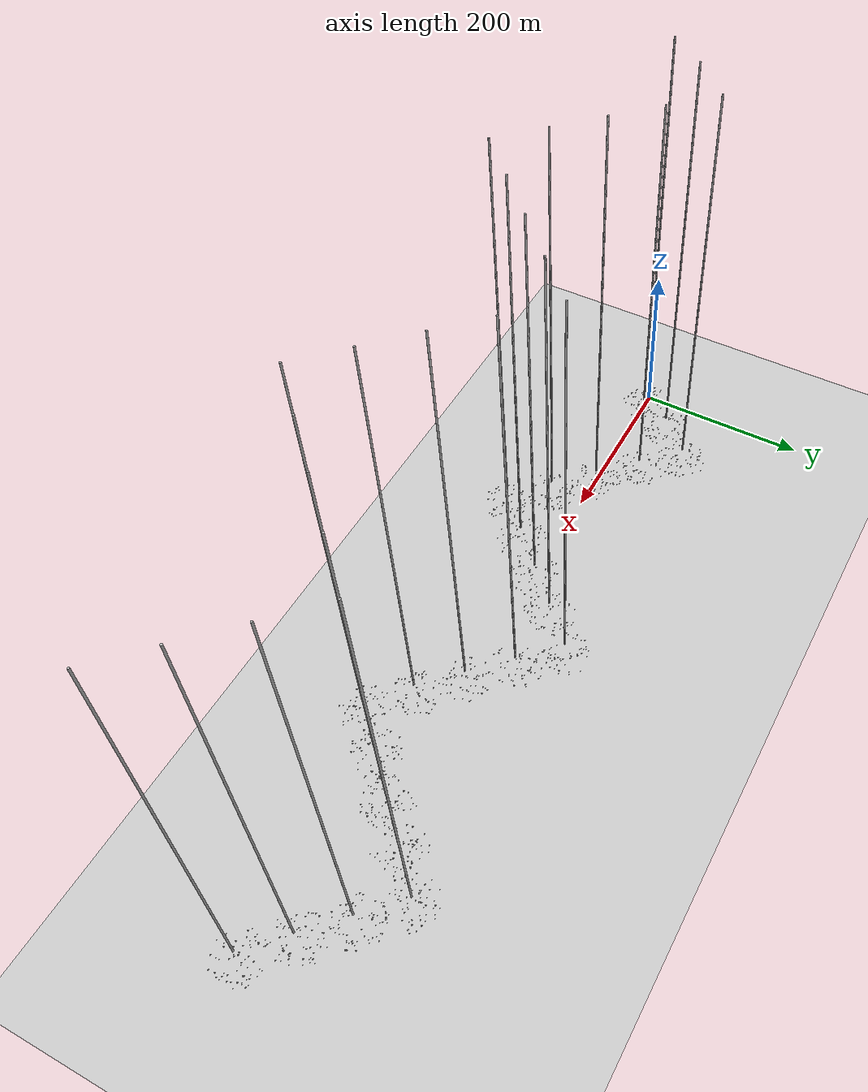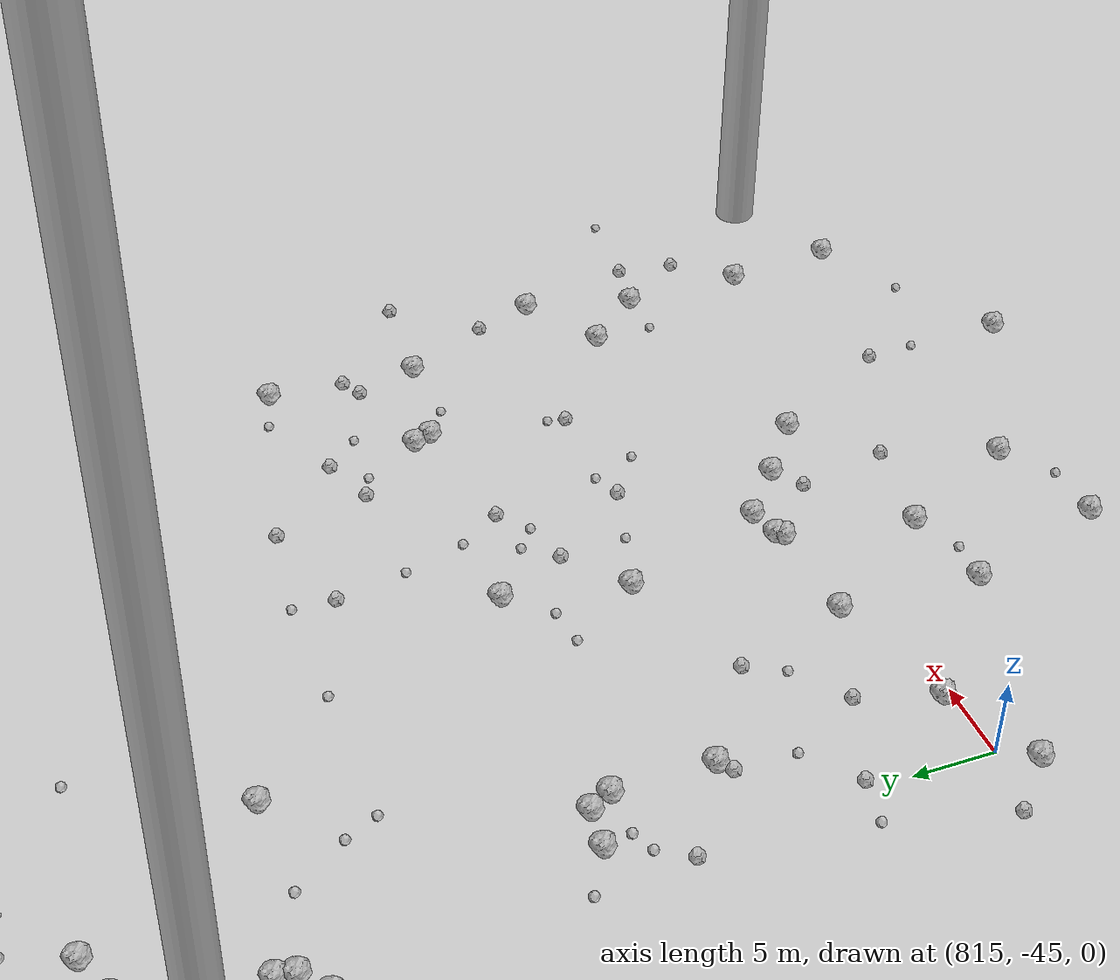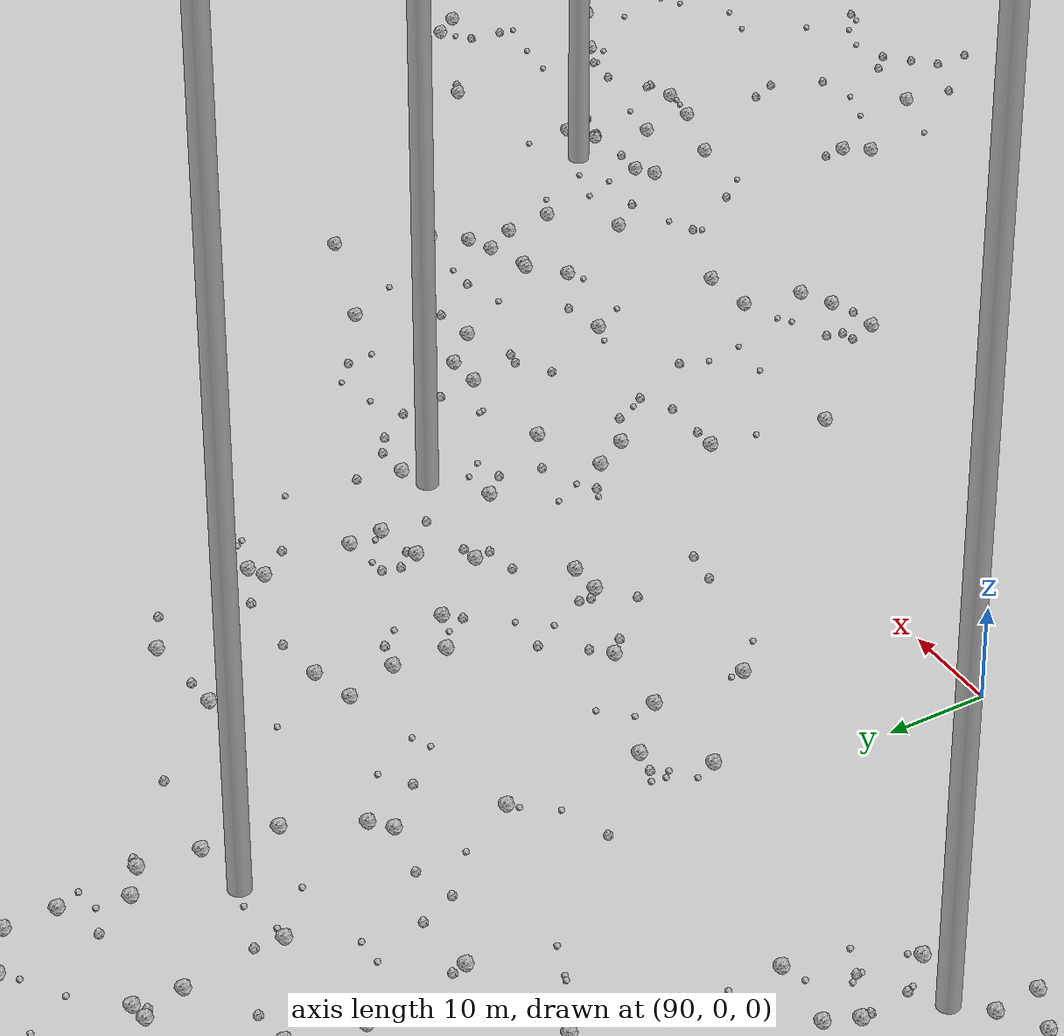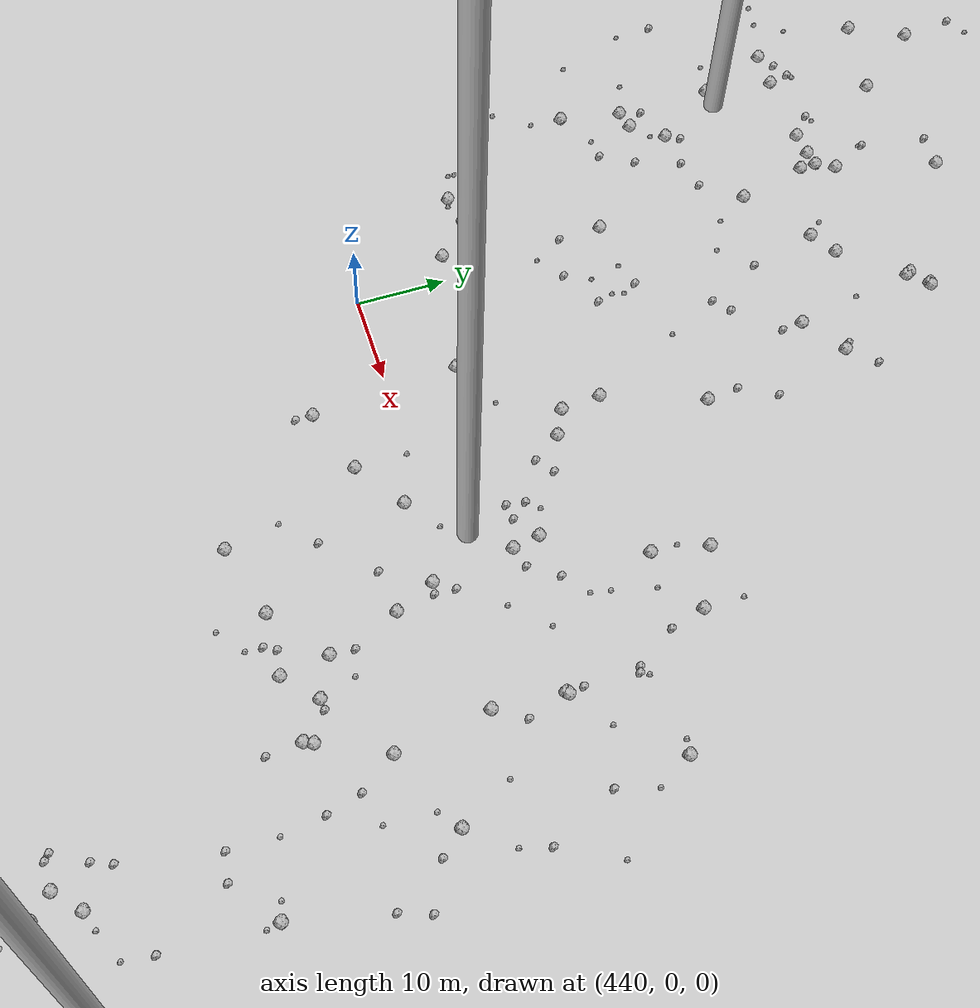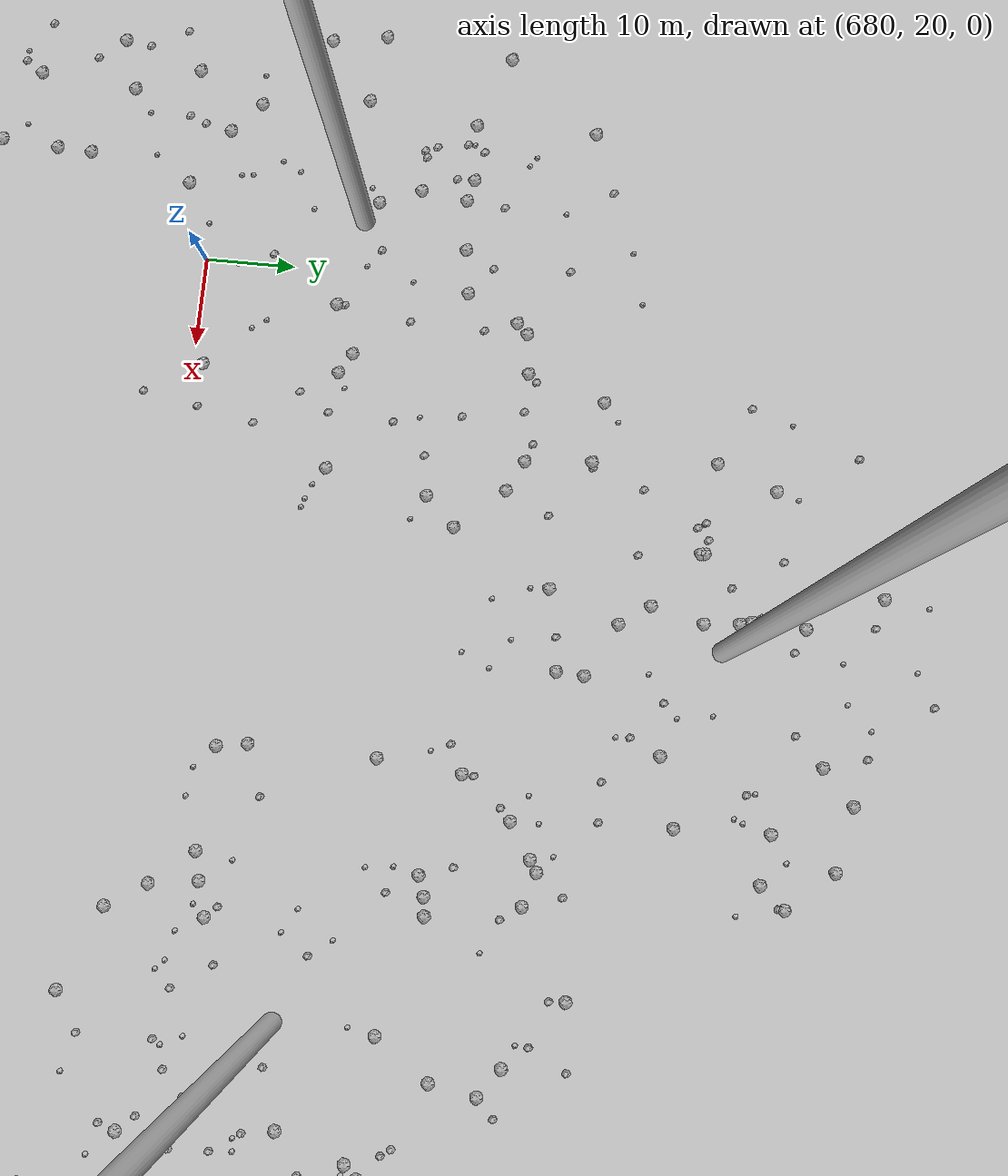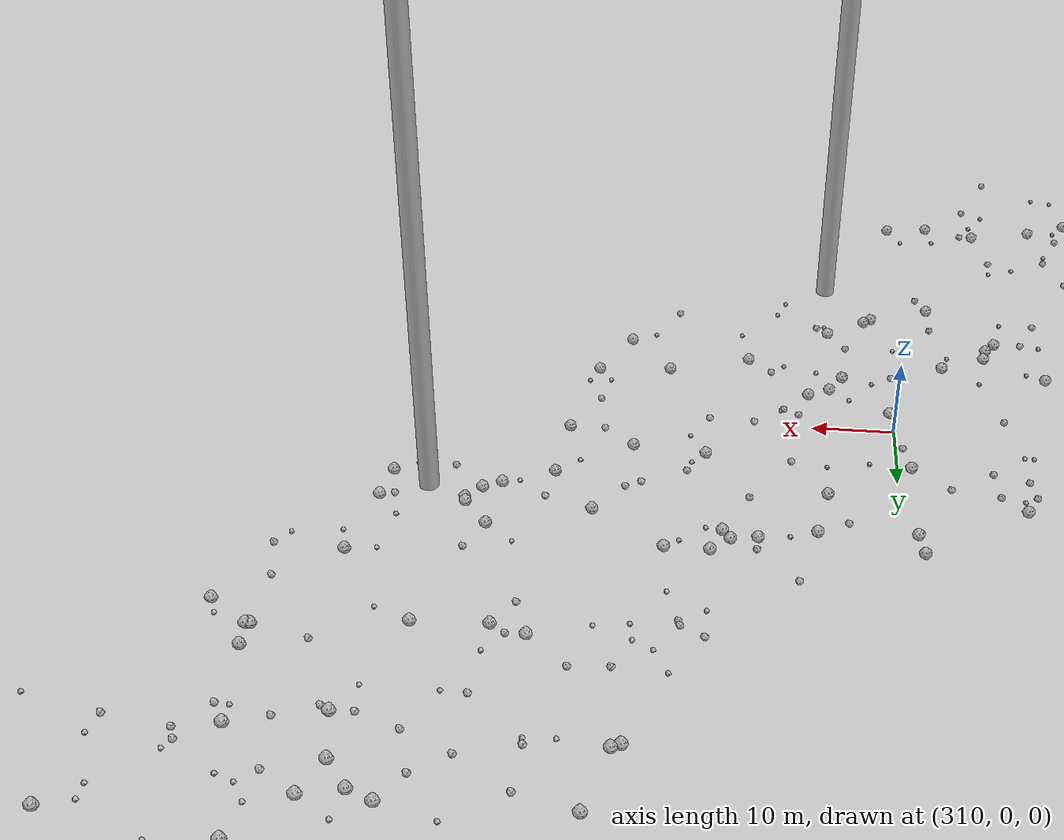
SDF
<sdf version="1.6">
 <world name="default">
  <include><uri>model://custom_ground</uri></include>
  <include><uri>model://sun</uri></include>
  <spherical_coordinates>
   <surface_model>EARTH_WGS84</surface_model>
   <latitude_deg>38.161479</latitude_deg>
   <longitude_deg>-122.454630</longitude_deg>
   <elevation>488.0</elevation>
   <heading_deg>90</heading_deg>
  </spherical_coordinates>
  <model name="rock1_0_0">
   <include><uri>model://rock1</uri><pose>17.000178213660845 -28.87803645918632 0.5 0 0 0</pose></include>
  </model>
  <model name="rock1_0_1">
   <include><uri>model://rock1</uri><pose>8.864647107650576 -18.266698169001845 0.5 0 0 0</pose></include>
  </model>
  <model name="rock1_0_2">
   <include><uri>model://rock1</uri><pose>12.009805290419777 20.778022938029174 0.5 0 0 0</pose></include>
  </model>
  <model name="rock1_0_3">
   <include><uri>model://rock1</uri><pose>19.11783946490526 -2.830191385487332 0.5 0 0 0</pose></include>
  </model>
  <model name="rock1_0_4">
   <include><uri>model://rock1</uri><pose>28.275477801045724 -5.199830700054797 0.5 0 0 0</pose></include>
  </model>
  <model name="rock1_0_5">
   <include><uri>model://rock1</uri><pose>8.193961739446433 -8.115403632144961 0.5 0 0 0</pose></include>
  </model>
  <model name="rock1_0_6">
   <include><uri>model://rock1</uri><pose>-18.609844253047257 -1.2738280485224038 0.5 0 0 0</pose></include>
  </model>
  <model name="rock1_0_7">
   <include><uri>model://rock1</uri><pose>-2.461888202025822 -12.49051554507706 0.5 0 0 0</pose></include>
  </model>
  <model name="rock1_0_8">
   <include><uri>model://rock1</uri><pose>-5.673768688803349 -20.82936731330288 0.5 0 0 0</pose></include>
  </model>
  <model name="rock1_0_9">
   <include><uri>model://rock1</uri><pose>22.415381781897032 -15.656251065551377 0.5 0 0 0</pose></include>
  </model>
  <model name="rock1_0_10">
   <include><uri>model://rock1</uri><pose>22.621525095388265 12.513634585462647 0.5 0 0 0</pose></include>
  </model>
  <model name="rock1_0_11">
   <include><uri>model://rock1</uri><pose>17.632661791607063 -8.431889266764895 0.5 0 0 0</pose></include>
  </model>
  <model name="rock1_0_12">
   <include><uri>model://rock1</uri><pose>-1.439267190141436 -10.19157400393167 0.5 0 0 0</pose></include>
  </model>
  <model name="rock1_0_13">
   <include><uri>model://rock1</uri><pose>-11.130100086824799 -9.067945342541982 0.5 0 0 0</pose></include>
  </model>
  <model name="rock1_0_14">
   <include><uri>model://rock1</uri><pose>11.455203371504822 -25.59661957186833 0.5 0 0 0</pose></include>
  </model>
  <model name="rock1_0_15">
   <include><uri>model://rock1</uri><pose>-0.5293848883131922 18.847581116524438 0.5 0 0 0</pose></include>
  </model>
  <model name="rock1_0_16">
   <include><uri>model://rock1</uri><pose>17.99722097729436 -7.040404632938433 0.5 0 0 0</pose></include>
  </model>
  <model name="rock1_0_17">
   <include><uri>model://rock1</uri><pose>21.873496383115707 -12.428618247592752 0.5 0 0 0</pose></include>
  </model>
  <model name="rock1_0_18">
   <include><uri>model://rock1</uri><pose>10.298786313121369 -3.0472604591909125 0.5 0 0 0</pose></include>
  </model>
  <model name="rock1_0_19">
   <include><uri>model://rock1</uri><pose>-7.788093899057575 6.06985416182728 0.5 0 0 0</pose></include>
  </model>
  <model name="rock1_0_20">
   <include><uri>model://rock1</uri><pose>2.730627680503595 -23.759858944267698 0.5 0 0 0</pose></include>
  </model>
  <model name="rock1_0_21">
   <include><uri>model://rock1</uri><pose>30.097744586177114 4.857603896208651 0.5 0 0 0</pose></include>
  </model>
  <model name="rock1_0_22">
   <include><uri>model://rock1</uri><pose>-13.676048023777339 1.2704413457938166 0.5 0 0 0</pose></include>
  </model>
  <model name="rock1_0_23">
   <include><uri>model://rock1</uri><pose>4.046809035472151 -24.44037549329796 0.5 0 0 0</pose></include>
  </model>
  <model name="rock1_0_24">
   <include><uri>model://rock1</uri><pose>25.345491382967175 -7.78632050880438 0.5 0 0 0</pose></include>
  </model>
  <model name="rock1_0_25">
   <include><uri>model://rock1</uri><pose>0.5433630839563648 -19.977496561601697 0.5 0 0 0</pose></include>
  </model>
  <model name="rock1_0_26">
   <include><uri>model://rock1</uri><pose>17.378240793037 6.351210347920393 0.5 0 0 0</pose></include>
  </model>
  <model name="rock2_0_0">
   <include><uri>model://rock2</uri><pose>24.314107509540392 17.040155431373492 0.3 0 0 0</pose></include>
  </model>
  <model name="rock2_0_1">
   <include><uri>model://rock2</uri><pose>-11.41227465724917 -0.03209581568732034 0.3 0 0 0</pose></include>
  </model>
  <model name="rock2_0_2">
   <include><uri>model://rock2</uri><pose>-2.3196174395368203 -25.71199256479658 0.3 0 0 0</pose></include>
  </model>
  <model name="rock2_0_3">
   <include><uri>model://rock2</uri><pose>20.903687236052768 -7.080423527443575 0.3 0 0 0</pose></include>
  </model>
  <model name="rock2_0_4">
   <include><uri>model://rock2</uri><pose>29.236138779787908 19.20378873858521 0.3 0 0 0</pose></include>
  </model>
  <model name="rock2_0_5">
   <include><uri>model://rock2</uri><pose>14.55258543265382 24.84463611523617 0.3 0 0 0</pose></include>
  </model>
  <model name="rock2_0_6">
   <include><uri>model://rock2</uri><pose>-17.908832977637417 7.500257026309299 0.3 0 0 0</pose></include>
  </model>
  <model name="rock2_0_7">
   <include><uri>model://rock2</uri><pose>32.61352874445837 8.887029138159043 0.3 0 0 0</pose></include>
  </model>
  <model name="rock2_0_8">
   <include><uri>model://rock2</uri><pose>37.93652916232535 4.741693024061071 0.3 0 0 0</pose></include>
  </model>
  <model name="rock2_0_9">
   <include><uri>model://rock2</uri><pose>38.46198027559075 5.605968230287203 0.3 0 0 0</pose></include>
  </model>
  <model name="rock2_0_10">
   <include><uri>model://rock2</uri><pose>4.7503702176375775 -26.78755115428505 0.3 0 0 0</pose></include>
  </model>
  <model name="rock2_0_11">
   <include><uri>model://rock2</uri><pose>7.243963860117123 14.3938854331372 0.3 0 0 0</pose></include>
  </model>
  <model name="rock2_0_12">
   <include><uri>model://rock2</uri><pose>-14.807210036500425 7.946614642740734 0.3 0 0 0</pose></include>
  </model>
  <model name="rock2_0_13">
   <include><uri>model://rock2</uri><pose>4.557200551097814 10.027471591222053 0.3 0 0 0</pose></include>
  </model>
  <model name="rock2_0_14">
   <include><uri>model://rock2</uri><pose>-2.9576585368380854 21.536169087038587 0.3 0 0 0</pose></include>
  </model>
  <model name="rock2_0_15">
   <include><uri>model://rock2</uri><pose>-7.943971601777502 3.192666977579357 0.3 0 0 0</pose></include>
  </model>
  <model name="rock2_0_16">
   <include><uri>model://rock2</uri><pose>22.181224107946974 -23.626320641283705 0.3 0 0 0</pose></include>
  </model>
  <model name="rock2_0_17">
   <include><uri>model://rock2</uri><pose>7.596921213921352 -16.730809989397677 0.3 0 0 0</pose></include>
  </model>
  <model name="rock2_0_18">
   <include><uri>model://rock2</uri><pose>29.32284997111364 -1.9465297777502926 0.3 0 0 0</pose></include>
  </model>
  <model name="rock2_0_19">
   <include><uri>model://rock2</uri><pose>38.580506558102144 -8.214020276197235 0.3 0 0 0</pose></include>
  </model>
  <model name="rock2_0_20">
   <include><uri>model://rock2</uri><pose>18.431360009069756 -13.37848299016299 0.3 0 0 0</pose></include>
  </model>
  <model name="rock2_0_21">
   <include><uri>model://rock2</uri><pose>20.23146121236349 8.666358381879427 0.3 0 0 0</pose></include>
  </model>
  <model name="rock2_0_22">
   <include><uri>model://rock2</uri><pose>26.351948073171563 7.344535848564632 0.3 0 0 0</pose></include>
  </model>
  <model name="rock2_0_23">
   <include><uri>model://rock2</uri><pose>-0.5093665680583754 -7.379565872394895 0.3 0 0 0</pose></include>
  </model>
  <model name="rock2_0_24">
   <include><uri>model://rock2</uri><pose>28.17129119100703 3.227762996286735 0.3 0 0 0</pose></include>
  </model>
  <model name="rock2_0_25">
   <include><uri>model://rock2</uri><pose>5.485107847244318 23.005035309765333 0.3 0 0 0</pose></include>
  </model>
  <model name="rock2_0_26">
   <include><uri>model://rock2</uri><pose>10.572351414022052 3.249788516072158 0.3 0 0 0</pose></include>
  </model>
  <model name="rock3_0_0">
   <include><uri>model://rock3</uri><pose>33.65126602223509 4.185834047100904 0.2 0 0 0</pose></include>
  </model>
  <model name="rock3_0_1">
   <include><uri>model://rock3</uri><pose>8.86586302067299 -5.709398091394121 0.2 0 0 0</pose></include>
  </model>
  <model name="rock3_0_2">
   <include><uri>model://rock3</uri><pose>13.378659256419724 -9.341892374225772 0.2 0 0 0</pose></include>
  </model>
  <model name="rock3_0_3">
   <include><uri>model://rock3</uri><pose>9.789290235167321 -23.79115604533697 0.2 0 0 0</pose></include>
  </model>
  <model name="rock3_0_4">
   <include><uri>model://rock3</uri><pose>34.13312206582879 -11.643505765901242 0.2 0 0 0</pose></include>
  </model>
  <model name="rock3_0_5">
   <include><uri>model://rock3</uri><pose>35.20311925695809 -2.84096042976228 0.2 0 0 0</pose></include>
  </model>
  <model name="rock3_0_6">
   <include><uri>model://rock3</uri><pose>14.630788231377153 -7.078976804626279 0.2 0 0 0</pose></include>
  </model>
  <model name="rock3_0_7">
   <include><uri>model://rock3</uri><pose>22.30879395226814 7.578517933641976 0.2 0 0 0</pose></include>
  </model>
  <model name="rock3_0_8">
   <include><uri>model://rock3</uri><pose>16.435566679675084 17.43609201347899 0.2 0 0 0</pose></include>
  </model>
  <model name="rock3_0_9">
   <include><uri>model://rock3</uri><pose>7.522523376136554 -26.680730015588885 0.2 0 0 0</pose></include>
  </model>
  <model name="rock3_0_10">
   <include><uri>model://rock3</uri><pose>-7.316015091978825 -3.0137532235304505 0.2 0 0 0</pose></include>
  </model>
  <model name="rock3_0_11">
   <include><uri>model://rock3</uri><pose>29.262972234575585 18.879980555387917 0.2 0 0 0</pose></include>
  </model>
  <model name="rock3_0_12">
   <include><uri>model://rock3</uri><pose>23.42737512882522 12.283981109702175 0.2 0 0 0</pose></include>
  </model>
  <model name="rock3_0_13">
   <include><uri>model://rock3</uri><pose>14.421067237117157 4.812500707299279 0.2 0 0 0</pose></include>
  </model>
  <model name="rock3_0_14">
   <include><uri>model://rock3</uri><pose>-11.513695632411743 19.785296723759316 0.2 0 0 0</pose></include>
  </model>
  <model name="rock3_0_15">
   <include><uri>model://rock3</uri><pose>35.90421695886823 -1.1364910370590344 0.2 0 0 0</pose></include>
  </model>
  <model name="rock3_0_16">
   <include><uri>model://rock3</uri><pose>2.706320189701369 7.961705881870259 0.2 0 0 0</pose></include>
  </model>
  <model name="rock3_0_17">
   <include><uri>model://rock3</uri><pose>-15.487163122304661 13.332743008566425 0.2 0 0 0</pose></include>
  </model>
  <model name="rock3_0_18">
   <include><uri>model://rock3</uri><pose>29.401065403649568 10.599717857721458 0.2 0 0 0</pose></include>
  </model>
  <model name="rock3_0_19">
   <include><uri>model://rock3</uri><pose>-6.122809019214191 -7.495867957519529 0.2 0 0 0</pose></include>
  </model>
  <model name="rock3_0_20">
   <include><uri>model://rock3</uri><pose>-5.408682862330343 24.97819407272042 0.2 0 0 0</pose></include>
  </model>
  <model name="rock3_0_21">
   <include><uri>model://rock3</uri><pose>23.054660600840982 17.40136710914028 0.2 0 0 0</pose></include>
  </model>
  <model name="rock3_0_22">
   <include><uri>model://rock3</uri><pose>8.343485527073888 -19.78155357750108 0.2 0 0 0</pose></include>
  </model>
  <model name="rock3_0_23">
   <include><uri>model://rock3</uri><pose>23.476208668205743 18.432534197940285 0.2 0 0 0</pose></include>
  </model>
  <model name="rock3_0_24">
   <include><uri>model://rock3</uri><pose>-4.108705887823065 -20.79988336647117 0.2 0 0 0</pose></include>
  </model>
  <model name="rock3_0_25">
   <include><uri>model://rock3</uri><pose>21.10280374228259 -25.711250819958167 0.2 0 0 0</pose></include>
  </model>
  <model name="rock3_0_26">
   <include><uri>model://rock3</uri><pose>12.45028130287556 -3.37533143557917 0.2 0 0 0</pose></include>
  </model>
  <model name="rock1_1_0">
   <include><uri>model://rock1</uri><pose>55.261434586659426 19.060513532829116 0.5 0 0 0</pose></include>
  </model>
  <model name="rock1_1_1">
   <include><uri>model://rock1</uri><pose>51.90999451352 37.30044436380455 0.5 0 0 0</pose></include>
  </model>
  <model name="rock1_1_2">
   <include><uri>model://rock1</uri><pose>61.19978451769745 36.60558144655525 0.5 0 0 0</pose></include>
  </model>
  <model name="rock1_1_3">
   <include><uri>model://rock1</uri><pose>22.430764800592893 40.171828471190956 0.5 0 0 0</pose></include>
  </model>
  <model name="rock1_1_4">
   <include><uri>model://rock1</uri><pose>68.60328213618826 35.76908854440332 0.5 0 0 0</pose></include>
  </model>
  <model name="rock1_1_5">
   <include><uri>model://rock1</uri><pose>22.461532161965675 31.45724097270364 0.5 0 0 0</pose></include>
  </model>
  <model name="rock1_1_6">
   <include><uri>model://rock1</uri><pose>26.135052432371232 54.21641048844922 0.5 0 0 0</pose></include>
  </model>
  <model name="rock1_1_7">
   <include><uri>model://rock1</uri><pose>59.89166327799474 33.639458253684296 0.5 0 0 0</pose></include>
  </model>
  <model name="rock1_1_8">
   <include><uri>model://rock1</uri><pose>42.394063755544124 60.48065579894665 0.5 0 0 0</pose></include>
  </model>
  <model name="rock1_1_9">
   <include><uri>model://rock1</uri><pose>54.84909334370991 23.654583781195818 0.5 0 0 0</pose></include>
  </model>
  <model name="rock1_1_10">
   <include><uri>model://rock1</uri><pose>23.402588950747788 50.33332282415471 0.5 0 0 0</pose></include>
  </model>
  <model name="rock1_1_11">
   <include><uri>model://rock1</uri><pose>35.40419549962425 52.01788383469481 0.5 0 0 0</pose></include>
  </model>
  <model name="rock1_1_12">
   <include><uri>model://rock1</uri><pose>48.729932999095034 65.71517970557281 0.5 0 0 0</pose></include>
  </model>
  <model name="rock1_1_13">
   <include><uri>model://rock1</uri><pose>12.410632527588948 39.1673874790584 0.5 0 0 0</pose></include>
  </model>
  <model name="rock1_1_14">
   <include><uri>model://rock1</uri><pose>24.138625596730275 30.339058532203836 0.5 0 0 0</pose></include>
  </model>
  <model name="rock1_1_15">
   <include><uri>model://rock1</uri><pose>15.973949602282723 55.652997435192404 0.5 0 0 0</pose></include>
  </model>
  <model name="rock1_1_16">
   <include><uri>model://rock1</uri><pose>63.72294126019727 24.823872279098886 0.5 0 0 0</pose></include>
  </model>
  <model name="rock1_1_17">
   <include><uri>model://rock1</uri><pose>52.47488887119968 45.460716027628955 0.5 0 0 0</pose></include>
  </model>
  <model name="rock1_1_18">
   <include><uri>model://rock1</uri><pose>50.736431911125024 28.57945825502314 0.5 0 0 0</pose></include>
  </model>
  <model name="rock1_1_19">
   <include><uri>model://rock1</uri><pose>11.78308818546534 49.81832914868642 0.5 0 0 0</pose></include>
  </model>
  <model name="rock1_1_20">
   <include><uri>model://rock1</uri><pose>36.64676428758308 22.149080254384877 0.5 0 0 0</pose></include>
  </model>
  <model name="rock1_1_21">
   <include><uri>model://rock1</uri><pose>26.83086923352173 22.97796518692259 0.5 0 0 0</pose></include>
  </model>
  <model name="rock1_1_22">
   <include><uri>model://rock1</uri><pose>52.159138753155204 16.85757451579658 0.5 0 0 0</pose></include>
  </model>
  <model name="rock1_1_23">
   <include><uri>model://rock1</uri><pose>50.75231161245064 21.220462008358645 0.5 0 0 0</pose></include>
  </model>
  <model name="rock1_1_24">
   <include><uri>model://rock1</uri><pose>37.451559772050366 63.46560246174567 0.5 0 0 0</pose></include>
  </model>
  <model name="rock1_1_25">
   <include><uri>model://rock1</uri><pose>20.683572065961023 42.313771700678025 0.5 0 0 0</pose></include>
  </model>
  <model name="rock1_1_26">
   <include><uri>model://rock1</uri><pose>44.00089045795815 30.856699568071228 0.5 0 0 0</pose></include>
  </model>
  <model name="rock2_1_0">
   <include><uri>model://rock2</uri><pose>21.94998580461796 37.607120275650246 0.3 0 0 0</pose></include>
  </model>
  <model name="rock2_1_1">
   <include><uri>model://rock2</uri><pose>52.55411914538646 56.431416275528925 0.3 0 0 0</pose></include>
  </model>
  <model name="rock2_1_2">
   <include><uri>model://rock2</uri><pose>45.30750797938342 14.968470897740946 0.3 0 0 0</pose></include>
  </model>
  <model name="rock2_1_3">
   <include><uri>model://rock2</uri><pose>36.2623916186234 17.141560899263734 0.3 0 0 0</pose></include>
  </model>
  <model name="rock2_1_4">
   <include><uri>model://rock2</uri><pose>43.82537357554467 22.8788297741476 0.3 0 0 0</pose></include>
  </model>
  <model name="rock2_1_5">
   <include><uri>model://rock2</uri><pose>35.813800636479456 48.22314306481838 0.3 0 0 0</pose></include>
  </model>
  <model name="rock2_1_6">
   <include><uri>model://rock2</uri><pose>42.163339022979336 30.25790731246634 0.3 0 0 0</pose></include>
  </model>
  <model name="rock2_1_7">
   <include><uri>model://rock2</uri><pose>64.60489874480689 30.873575551349248 0.3 0 0 0</pose></include>
  </model>
  <model name="rock2_1_8">
   <include><uri>model://rock2</uri><pose>37.93817745106759 20.739324580172276 0.3 0 0 0</pose></include>
  </model>
  <model name="rock2_1_9">
   <include><uri>model://rock2</uri><pose>60.00293682476776 32.57864162765716 0.3 0 0 0</pose></include>
  </model>
  <model name="rock2_1_10">
   <include><uri>model://rock2</uri><pose>53.89106103694943 48.59156185745519 0.3 0 0 0</pose></include>
  </model>
  <model name="rock2_1_11">
   <include><uri>model://rock2</uri><pose>54.28021720188795 62.4586096306333 0.3 0 0 0</pose></include>
  </model>
  <model name="rock2_1_12">
   <include><uri>model://rock2</uri><pose>58.185296686891476 45.60187516914841 0.3 0 0 0</pose></include>
  </model>
  <model name="rock2_1_13">
   <include><uri>model://rock2</uri><pose>22.62806243784986 45.477944615432676 0.3 0 0 0</pose></include>
  </model>
  <model name="rock2_1_14">
   <include><uri>model://rock2</uri><pose>67.92406274767055 47.460990052443265 0.3 0 0 0</pose></include>
  </model>
  <model name="rock2_1_15">
   <include><uri>model://rock2</uri><pose>16.287302648616567 39.01027164956809 0.3 0 0 0</pose></include>
  </model>
  <model name="rock2_1_16">
   <include><uri>model://rock2</uri><pose>38.028522768347 52.06096370197537 0.3 0 0 0</pose></include>
  </model>
  <model name="rock2_1_17">
   <include><uri>model://rock2</uri><pose>60.595839787772555 28.47262976405933 0.3 0 0 0</pose></include>
  </model>
  <model name="rock2_1_18">
   <include><uri>model://rock2</uri><pose>40.852251666706046 50.28874554678637 0.3 0 0 0</pose></include>
  </model>
  <model name="rock2_1_19">
   <include><uri>model://rock2</uri><pose>42.2107653097714 51.175911553613275 0.3 0 0 0</pose></include>
  </model>
  <model name="rock2_1_20">
   <include><uri>model://rock2</uri><pose>49.572747808995295 63.73281823790681 0.3 0 0 0</pose></include>
  </model>
  <model name="rock2_1_21">
   <include><uri>model://rock2</uri><pose>39.77591867030587 57.791880348736434 0.3 0 0 0</pose></include>
  </model>
  <model name="rock2_1_22">
   <include><uri>model://rock2</uri><pose>27.414436760002605 65.0406053548243 0.3 0 0 0</pose></include>
  </model>
  <model name="rock2_1_23">
   <include><uri>model://rock2</uri><pose>37.60049670797465 44.95738193147946 0.3 0 0 0</pose></include>
  </model>
  <model name="rock2_1_24">
   <include><uri>model://rock2</uri><pose>37.211938114281836 39.60107058589913 0.3 0 0 0</pose></include>
  </model>
  <model name="rock2_1_25">
   <include><uri>model://rock2</uri><pose>24.490246668872317 37.97686154499006 0.3 0 0 0</pose></include>
  </model>
  <model name="rock2_1_26">
   <include><uri>model://rock2</uri><pose>45.8829486383922 33.20361264049853 0.3 0 0 0</pose></include>
  </model>
  <model name="rock3_1_0">
   <include><uri>model://rock3</uri><pose>46.151285018734555 68.90450034317706 0.2 0 0 0</pose></include>
  </model>
  <model name="rock3_1_1">
   <include><uri>model://rock3</uri><pose>59.96698890803985 59.401565443702104 0.2 0 0 0</pose></include>
  </model>
  <model name="rock3_1_2">
   <include><uri>model://rock3</uri><pose>64.84345480785493 39.81893134238222 0.2 0 0 0</pose></include>
  </model>
  <model name="rock3_1_3">
   <include><uri>model://rock3</uri><pose>67.64087198763741 29.382040624569154 0.2 0 0 0</pose></include>
  </model>
  <model name="rock3_1_4">
   <include><uri>model://rock3</uri><pose>50.123096423798465 63.23986507611057 0.2 0 0 0</pose></include>
  </model>
  <model name="rock3_1_5">
   <include><uri>model://rock3</uri><pose>64.64767773352473 30.289538998229155 0.2 0 0 0</pose></include>
  </model>
  <model name="rock3_1_6">
   <include><uri>model://rock3</uri><pose>29.689666110943573 14.71393021344095 0.2 0 0 0</pose></include>
  </model>
  <model name="rock3_1_7">
   <include><uri>model://rock3</uri><pose>41.70425007252781 52.52238981970031 0.2 0 0 0</pose></include>
  </model>
  <model name="rock3_1_8">
   <include><uri>model://rock3</uri><pose>58.619815453067176 56.705531854069605 0.2 0 0 0</pose></include>
  </model>
  <model name="rock3_1_9">
   <include><uri>model://rock3</uri><pose>16.508006443510716 38.327930005423624 0.2 0 0 0</pose></include>
  </model>
  <model name="rock3_1_10">
   <include><uri>model://rock3</uri><pose>61.01128981222915 27.611722982458687 0.2 0 0 0</pose></include>
  </model>
  <model name="rock3_1_11">
   <include><uri>model://rock3</uri><pose>63.983361268628975 31.60871864695978 0.2 0 0 0</pose></include>
  </model>
  <model name="rock3_1_12">
   <include><uri>model://rock3</uri><pose>36.49031031606467 21.124687491149878 0.2 0 0 0</pose></include>
  </model>
  <model name="rock3_1_13">
   <include><uri>model://rock3</uri><pose>16.635412016293504 54.66488015529335 0.2 0 0 0</pose></include>
  </model>
  <model name="rock3_1_14">
   <include><uri>model://rock3</uri><pose>49.12203473460711 26.755583561581076 0.2 0 0 0</pose></include>
  </model>
  <model name="rock3_1_15">
   <include><uri>model://rock3</uri><pose>36.241156719144314 34.7757790028075 0.2 0 0 0</pose></include>
  </model>
  <model name="rock3_1_16">
   <include><uri>model://rock3</uri><pose>52.81407238721041 27.028446177409503 0.2 0 0 0</pose></include>
  </model>
  <model name="rock3_1_17">
   <include><uri>model://rock3</uri><pose>43.05276621710578 58.864743526008304 0.2 0 0 0</pose></include>
  </model>
  <model name="rock3_1_18">
   <include><uri>model://rock3</uri><pose>46.779514376896074 10.946162622172285 0.2 0 0 0</pose></include>
  </model>
  <model name="rock3_1_19">
   <include><uri>model://rock3</uri><pose>66.28450928698138 34.83349164327018 0.2 0 0 0</pose></include>
  </model>
  <model name="rock3_1_20">
   <include><uri>model://rock3</uri><pose>64.5938415217974 25.658336824957715 0.2 0 0 0</pose></include>
  </model>
  <model name="rock3_1_21">
   <include><uri>model://rock3</uri><pose>68.45249278390699 41.057168337618855 0.2 0 0 0</pose></include>
  </model>
  <model name="rock3_1_22">
   <include><uri>model://rock3</uri><pose>49.21578521882495 46.09757070750798 0.2 0 0 0</pose></include>
  </model>
  <model name="rock3_1_23">
   <include><uri>model://rock3</uri><pose>26.970382164037705 33.675046329840825 0.2 0 0 0</pose></include>
  </model>
  <model name="rock3_1_24">
   <include><uri>model://rock3</uri><pose>51.02607173679334 48.21550697537251 0.2 0 0 0</pose></include>
  </model>
  <model name="rock3_1_25">
   <include><uri>model://rock3</uri><pose>22.088563332754497 48.659312191060295 0.2 0 0 0</pose></include>
  </model>
  <model name="rock3_1_26">
   <include><uri>model://rock3</uri><pose>51.58816049803395 31.792428655820178 0.2 0 0 0</pose></include>
  </model>
  <model name="rock1_2_0">
   <include><uri>model://rock1</uri><pose>80.34135163401456 68.93586337083079 0.5 0 0 0</pose></include>
  </model>
  <model name="rock1_2_1">
   <include><uri>model://rock1</uri><pose>77.05572705079354 71.42487004040805 0.5 0 0 0</pose></include>
  </model>
  <model name="rock1_2_2">
   <include><uri>model://rock1</uri><pose>82.01002296243522 75.75605531859567 0.5 0 0 0</pose></include>
  </model>
  <model name="rock1_2_3">
   <include><uri>model://rock1</uri><pose>82.490089399146 58.23010731368596 0.5 0 0 0</pose></include>
  </model>
  <model name="rock1_2_4">
   <include><uri>model://rock1</uri><pose>93.27755908780307 69.60633831329315 0.5 0 0 0</pose></include>
  </model>
  <model name="rock1_2_5">
   <include><uri>model://rock1</uri><pose>106.51659817725965 89.4285483694521 0.5 0 0 0</pose></include>
  </model>
  <model name="rock1_2_6">
   <include><uri>model://rock1</uri><pose>84.86883813866586 95.41208098808869 0.5 0 0 0</pose></include>
  </model>
  <model name="rock1_2_7">
   <include><uri>model://rock1</uri><pose>107.84829605577573 76.13819489122903 0.5 0 0 0</pose></include>
  </model>
  <model name="rock1_2_8">
   <include><uri>model://rock1</uri><pose>107.10018369727264 70.29032554412134 0.5 0 0 0</pose></include>
  </model>
  <model name="rock1_2_9">
   <include><uri>model://rock1</uri><pose>66.96784502815325 96.32843073181878 0.5 0 0 0</pose></include>
  </model>
  <model name="rock1_2_10">
   <include><uri>model://rock1</uri><pose>92.28109067622461 84.47023937624101 0.5 0 0 0</pose></include>
  </model>
  <model name="rock1_2_11">
   <include><uri>model://rock1</uri><pose>51.24238663031847 82.28295995365396 0.5 0 0 0</pose></include>
  </model>
  <model name="rock1_2_12">
   <include><uri>model://rock1</uri><pose>61.49899922161583 61.718891690268634 0.5 0 0 0</pose></include>
  </model>
  <model name="rock1_2_13">
   <include><uri>model://rock1</uri><pose>101.59153965651552 92.32151628283594 0.5 0 0 0</pose></include>
  </model>
  <model name="rock1_2_14">
   <include><uri>model://rock1</uri><pose>70.74426819554671 55.205449284794675 0.5 0 0 0</pose></include>
  </model>
  <model name="rock1_2_15">
   <include><uri>model://rock1</uri><pose>70.58634596263525 89.45267107734843 0.5 0 0 0</pose></include>
  </model>
  <model name="rock1_2_16">
   <include><uri>model://rock1</uri><pose>82.14971431943991 93.63625133949404 0.5 0 0 0</pose></include>
  </model>
  <model name="rock1_2_17">
   <include><uri>model://rock1</uri><pose>106.55676886502323 84.34733836775838 0.5 0 0 0</pose></include>
  </model>
  <model name="rock1_2_18">
   <include><uri>model://rock1</uri><pose>64.30403060809844 98.23699202986563 0.5 0 0 0</pose></include>
  </model>
  <model name="rock1_2_19">
   <include><uri>model://rock1</uri><pose>65.24672745578337 89.37655277250235 0.5 0 0 0</pose></include>
  </model>
  <model name="rock1_2_20">
   <include><uri>model://rock1</uri><pose>104.74968091953426 78.28682057862903 0.5 0 0 0</pose></include>
  </model>
  <model name="rock1_2_21">
   <include><uri>model://rock1</uri><pose>50.67580306563408 80.18114023947885 0.5 0 0 0</pose></include>
  </model>
  <model name="rock1_2_22">
   <include><uri>model://rock1</uri><pose>90.34943950013586 84.24359590650067 0.5 0 0 0</pose></include>
  </model>
  <model name="rock1_2_23">
   <include><uri>model://rock1</uri><pose>62.00257763481465 83.97605178614033 0.5 0 0 0</pose></include>
  </model>
  <model name="rock1_2_24">
   <include><uri>model://rock1</uri><pose>62.84795433441714 83.42424768182431 0.5 0 0 0</pose></include>
  </model>
  <model name="rock1_2_25">
   <include><uri>model://rock1</uri><pose>70.73604400147595 98.35322354917922 0.5 0 0 0</pose></include>
  </model>
  <model name="rock1_2_26">
   <include><uri>model://rock1</uri><pose>92.00606082550762 79.84164890672758 0.5 0 0 0</pose></include>
  </model>
  <model name="rock2_2_0">
   <include><uri>model://rock2</uri><pose>82.08569119327123 59.671845186044436 0.3 0 0 0</pose></include>
  </model>
  <model name="rock2_2_1">
   <include><uri>model://rock2</uri><pose>60.5013690764656 83.09075237307181 0.3 0 0 0</pose></include>
  </model>
  <model name="rock2_2_2">
   <include><uri>model://rock2</uri><pose>79.35777155110989 99.81119401263265 0.3 0 0 0</pose></include>
  </model>
  <model name="rock2_2_3">
   <include><uri>model://rock2</uri><pose>93.37195784959829 72.40120798028022 0.3 0 0 0</pose></include>
  </model>
  <model name="rock2_2_4">
   <include><uri>model://rock2</uri><pose>78.08760854998133 85.91609015882881 0.3 0 0 0</pose></include>
  </model>
  <model name="rock2_2_5">
   <include><uri>model://rock2</uri><pose>90.64992706402587 54.75482865508642 0.3 0 0 0</pose></include>
  </model>
  <model name="rock2_2_6">
   <include><uri>model://rock2</uri><pose>54.09471346957841 81.91062624805522 0.3 0 0 0</pose></include>
  </model>
  <model name="rock2_2_7">
   <include><uri>model://rock2</uri><pose>91.2260727687096 83.51287618396584 0.3 0 0 0</pose></include>
  </model>
  <model name="rock2_2_8">
   <include><uri>model://rock2</uri><pose>85.83930011581529 76.02677763924287 0.3 0 0 0</pose></include>
  </model>
  <model name="rock2_2_9">
   <include><uri>model://rock2</uri><pose>88.93992927356351 58.57760563870697 0.3 0 0 0</pose></include>
  </model>
  <model name="rock2_2_10">
   <include><uri>model://rock2</uri><pose>101.76674778445246 82.73167532239785 0.3 0 0 0</pose></include>
  </model>
  <model name="rock2_2_11">
   <include><uri>model://rock2</uri><pose>65.45405540513123 82.0230763880193 0.3 0 0 0</pose></include>
  </model>
  <model name="rock2_2_12">
   <include><uri>model://rock2</uri><pose>85.17587235412023 109.25053326837924 0.3 0 0 0</pose></include>
  </model>
  <model name="rock2_2_13">
   <include><uri>model://rock2</uri><pose>94.95553324085078 55.872920547044714 0.3 0 0 0</pose></include>
  </model>
  <model name="rock2_2_14">
   <include><uri>model://rock2</uri><pose>58.28901273678866 97.41419215820687 0.3 0 0 0</pose></include>
  </model>
  <model name="rock2_2_15">
   <include><uri>model://rock2</uri><pose>71.22543783021978 94.02205648533581 0.3 0 0 0</pose></include>
  </model>
  <model name="rock2_2_16">
   <include><uri>model://rock2</uri><pose>65.56419194631401 90.5205524145656 0.3 0 0 0</pose></include>
  </model>
  <model name="rock2_2_17">
   <include><uri>model://rock2</uri><pose>72.63204716425784 107.28121033262045 0.3 0 0 0</pose></include>
  </model>
  <model name="rock2_2_18">
   <include><uri>model://rock2</uri><pose>78.3865107886782 97.44683472971236 0.3 0 0 0</pose></include>
  </model>
  <model name="rock2_2_19">
   <include><uri>model://rock2</uri><pose>81.95672743161204 89.7347478424437 0.3 0 0 0</pose></include>
  </model>
  <model name="rock2_2_20">
   <include><uri>model://rock2</uri><pose>70.63993585992492 100.17618723721888 0.3 0 0 0</pose></include>
  </model>
  <model name="rock2_2_21">
   <include><uri>model://rock2</uri><pose>59.109270727148676 69.01361271635434 0.3 0 0 0</pose></include>
  </model>
  <model name="rock2_2_22">
   <include><uri>model://rock2</uri><pose>61.56325206901954 56.79260629110426 0.3 0 0 0</pose></include>
  </model>
  <model name="rock2_2_23">
   <include><uri>model://rock2</uri><pose>59.73708370430789 82.76987864616358 0.3 0 0 0</pose></include>
  </model>
  <model name="rock2_2_24">
   <include><uri>model://rock2</uri><pose>93.31892777231687 101.26929686954755 0.3 0 0 0</pose></include>
  </model>
  <model name="rock2_2_25">
   <include><uri>model://rock2</uri><pose>108.95957815991437 75.83813830668942 0.3 0 0 0</pose></include>
  </model>
  <model name="rock2_2_26">
   <include><uri>model://rock2</uri><pose>83.67328073776937 68.78750205186508 0.3 0 0 0</pose></include>
  </model>
  <model name="rock3_2_0">
   <include><uri>model://rock3</uri><pose>73.31090369418293 83.73534294902828 0.2 0 0 0</pose></include>
  </model>
  <model name="rock3_2_1">
   <include><uri>model://rock3</uri><pose>69.81035023298932 58.9847300832749 0.2 0 0 0</pose></include>
  </model>
  <model name="rock3_2_2">
   <include><uri>model://rock3</uri><pose>73.76804060381691 73.32519988589955 0.2 0 0 0</pose></include>
  </model>
  <model name="rock3_2_3">
   <include><uri>model://rock3</uri><pose>86.67217283117327 64.23925468168329 0.2 0 0 0</pose></include>
  </model>
  <model name="rock3_2_4">
   <include><uri>model://rock3</uri><pose>80.62949874954138 50.309855699050516 0.2 0 0 0</pose></include>
  </model>
  <model name="rock3_2_5">
   <include><uri>model://rock3</uri><pose>53.541104803234525 94.04268338825267 0.2 0 0 0</pose></include>
  </model>
  <model name="rock3_2_6">
   <include><uri>model://rock3</uri><pose>71.82160954752578 80.42672168617409 0.2 0 0 0</pose></include>
  </model>
  <model name="rock3_2_7">
   <include><uri>model://rock3</uri><pose>81.59896341597796 74.97406389863254 0.2 0 0 0</pose></include>
  </model>
  <model name="rock3_2_8">
   <include><uri>model://rock3</uri><pose>76.52245459799519 51.911748744593346 0.2 0 0 0</pose></include>
  </model>
  <model name="rock3_2_9">
   <include><uri>model://rock3</uri><pose>75.27276653746478 72.4241793768855 0.2 0 0 0</pose></include>
  </model>
  <model name="rock3_2_10">
   <include><uri>model://rock3</uri><pose>100.12763232088501 90.87843277099844 0.2 0 0 0</pose></include>
  </model>
  <model name="rock3_2_11">
   <include><uri>model://rock3</uri><pose>107.60008906575275 81.73568367472377 0.2 0 0 0</pose></include>
  </model>
  <model name="rock3_2_12">
   <include><uri>model://rock3</uri><pose>66.86151337980016 100.13069667590796 0.2 0 0 0</pose></include>
  </model>
  <model name="rock3_2_13">
   <include><uri>model://rock3</uri><pose>104.96944859255893 81.38742038390521 0.2 0 0 0</pose></include>
  </model>
  <model name="rock3_2_14">
   <include><uri>model://rock3</uri><pose>59.85673833433425 71.3866832684283 0.2 0 0 0</pose></include>
  </model>
  <model name="rock3_2_15">
   <include><uri>model://rock3</uri><pose>87.04550624103221 94.54078042139045 0.2 0 0 0</pose></include>
  </model>
  <model name="rock3_2_16">
   <include><uri>model://rock3</uri><pose>67.53934497840457 63.5073612940873 0.2 0 0 0</pose></include>
  </model>
  <model name="rock3_2_17">
   <include><uri>model://rock3</uri><pose>96.25353959097076 88.51086481322707 0.2 0 0 0</pose></include>
  </model>
  <model name="rock3_2_18">
   <include><uri>model://rock3</uri><pose>81.01216591520573 100.08593800923322 0.2 0 0 0</pose></include>
  </model>
  <model name="rock3_2_19">
   <include><uri>model://rock3</uri><pose>98.29560309334613 65.09330343261091 0.2 0 0 0</pose></include>
  </model>
  <model name="rock3_2_20">
   <include><uri>model://rock3</uri><pose>89.54773676429605 64.16944197407373 0.2 0 0 0</pose></include>
  </model>
  <model name="rock3_2_21">
   <include><uri>model://rock3</uri><pose>93.62645721285915 93.0450146600197 0.2 0 0 0</pose></include>
  </model>
  <model name="rock3_2_22">
   <include><uri>model://rock3</uri><pose>77.0829979171452 51.701747116784084 0.2 0 0 0</pose></include>
  </model>
  <model name="rock3_2_23">
   <include><uri>model://rock3</uri><pose>74.14067181729283 100.18196839225004 0.2 0 0 0</pose></include>
  </model>
  <model name="rock3_2_24">
   <include><uri>model://rock3</uri><pose>94.7362614523066 69.42173058606534 0.2 0 0 0</pose></include>
  </model>
  <model name="rock3_2_25">
   <include><uri>model://rock3</uri><pose>98.69310766971319 70.51659233708267 0.2 0 0 0</pose></include>
  </model>
  <model name="rock3_2_26">
   <include><uri>model://rock3</uri><pose>68.48165897789579 93.82397378089388 0.2 0 0 0</pose></include>
  </model>
  <model name="rock1_3_0">
   <include><uri>model://rock1</uri><pose>139.34247732224094 37.723825815118246 0.5 0 0 0</pose></include>
  </model>
  <model name="rock1_3_1">
   <include><uri>model://rock1</uri><pose>101.03917986467619 54.58058994510651 0.5 0 0 0</pose></include>
  </model>
  <model name="rock1_3_2">
   <include><uri>model://rock1</uri><pose>134.32364399898637 60.614737567285886 0.5 0 0 0</pose></include>
  </model>
  <model name="rock1_3_3">
   <include><uri>model://rock1</uri><pose>98.77356129176913 30.93253047243164 0.5 0 0 0</pose></include>
  </model>
  <model name="rock1_3_4">
   <include><uri>model://rock1</uri><pose>121.55222903038555 21.607108768878824 0.5 0 0 0</pose></include>
  </model>
  <model name="rock1_3_5">
   <include><uri>model://rock1</uri><pose>139.62709677712553 34.18090661357453 0.5 0 0 0</pose></include>
  </model>
  <model name="rock1_3_6">
   <include><uri>model://rock1</uri><pose>106.34561615294129 63.08302736434801 0.5 0 0 0</pose></include>
  </model>
  <model name="rock1_3_7">
   <include><uri>model://rock1</uri><pose>147.13091635326234 27.690757937259345 0.5 0 0 0</pose></include>
  </model>
  <model name="rock1_3_8">
   <include><uri>model://rock1</uri><pose>125.02104255975905 21.641258153018 0.5 0 0 0</pose></include>
  </model>
  <model name="rock1_3_9">
   <include><uri>model://rock1</uri><pose>98.69734051972532 44.66850893156303 0.5 0 0 0</pose></include>
  </model>
  <model name="rock1_3_10">
   <include><uri>model://rock1</uri><pose>120.77336054158202 37.967900890795065 0.5 0 0 0</pose></include>
  </model>
  <model name="rock1_3_11">
   <include><uri>model://rock1</uri><pose>112.19374392332988 25.24585323713758 0.5 0 0 0</pose></include>
  </model>
  <model name="rock1_3_12">
   <include><uri>model://rock1</uri><pose>140.79033839255644 47.767530439430956 0.5 0 0 0</pose></include>
  </model>
  <model name="rock1_3_13">
   <include><uri>model://rock1</uri><pose>134.74688430265388 33.14419189971957 0.5 0 0 0</pose></include>
  </model>
  <model name="rock1_3_14">
   <include><uri>model://rock1</uri><pose>139.47050843889838 22.4049226551193 0.5 0 0 0</pose></include>
  </model>
  <model name="rock1_3_15">
   <include><uri>model://rock1</uri><pose>123.71245736915229 50.035253558134826 0.5 0 0 0</pose></include>
  </model>
  <model name="rock1_3_16">
   <include><uri>model://rock1</uri><pose>131.31067160582938 28.75880963754546 0.5 0 0 0</pose></include>
  </model>
  <model name="rock1_3_17">
   <include><uri>model://rock1</uri><pose>102.90814234676353 56.167275004351225 0.5 0 0 0</pose></include>
  </model>
  <model name="rock1_3_18">
   <include><uri>model://rock1</uri><pose>121.01293508637957 43.41978877732386 0.5 0 0 0</pose></include>
  </model>
  <model name="rock1_3_19">
   <include><uri>model://rock1</uri><pose>94.29338224429377 26.019164720758347 0.5 0 0 0</pose></include>
  </model>
  <model name="rock1_3_20">
   <include><uri>model://rock1</uri><pose>124.99740443445779 60.149620073104046 0.5 0 0 0</pose></include>
  </model>
  <model name="rock1_3_21">
   <include><uri>model://rock1</uri><pose>133.96555232706567 53.34568920722384 0.5 0 0 0</pose></include>
  </model>
  <model name="rock1_3_22">
   <include><uri>model://rock1</uri><pose>103.9359151301744 16.656300979847604 0.5 0 0 0</pose></include>
  </model>
  <model name="rock1_3_23">
   <include><uri>model://rock1</uri><pose>104.14376321140034 26.010034863551155 0.5 0 0 0</pose></include>
  </model>
  <model name="rock1_3_24">
   <include><uri>model://rock1</uri><pose>125.2504580163349 35.841307860776375 0.5 0 0 0</pose></include>
  </model>
  <model name="rock1_3_25">
   <include><uri>model://rock1</uri><pose>119.07868676175225 48.978479365838574 0.5 0 0 0</pose></include>
  </model>
  <model name="rock1_3_26">
   <include><uri>model://rock1</uri><pose>139.18407814709641 46.90300000425205 0.5 0 0 0</pose></include>
  </model>
  <model name="rock2_3_0">
   <include><uri>model://rock2</uri><pose>128.9250567886625 50.4400886000048 0.3 0 0 0</pose></include>
  </model>
  <model name="rock2_3_1">
   <include><uri>model://rock2</uri><pose>120.64093239435198 23.808810964729595 0.3 0 0 0</pose></include>
  </model>
  <model name="rock2_3_2">
   <include><uri>model://rock2</uri><pose>133.13909205503083 28.89384183566451 0.3 0 0 0</pose></include>
  </model>
  <model name="rock2_3_3">
   <include><uri>model://rock2</uri><pose>141.68906443678992 43.653371553466236 0.3 0 0 0</pose></include>
  </model>
  <model name="rock2_3_4">
   <include><uri>model://rock2</uri><pose>148.13836635862685 32.02215401214057 0.3 0 0 0</pose></include>
  </model>
  <model name="rock2_3_5">
   <include><uri>model://rock2</uri><pose>136.0129941833861 49.9525284373402 0.3 0 0 0</pose></include>
  </model>
  <model name="rock2_3_6">
   <include><uri>model://rock2</uri><pose>134.18791787917658 37.13071644373525 0.3 0 0 0</pose></include>
  </model>
  <model name="rock2_3_7">
   <include><uri>model://rock2</uri><pose>135.53672569544432 33.667501602004734 0.3 0 0 0</pose></include>
  </model>
  <model name="rock2_3_8">
   <include><uri>model://rock2</uri><pose>128.21378821141766 60.19363061573971 0.3 0 0 0</pose></include>
  </model>
  <model name="rock2_3_9">
   <include><uri>model://rock2</uri><pose>117.049363125817 68.72548967476898 0.3 0 0 0</pose></include>
  </model>
  <model name="rock2_3_10">
   <include><uri>model://rock2</uri><pose>123.95187917237715 42.57615948661223 0.3 0 0 0</pose></include>
  </model>
  <model name="rock2_3_11">
   <include><uri>model://rock2</uri><pose>116.78457464172 30.597055069622584 0.3 0 0 0</pose></include>
  </model>
  <model name="rock2_3_12">
   <include><uri>model://rock2</uri><pose>138.79027757986682 29.703025963445896 0.3 0 0 0</pose></include>
  </model>
  <model name="rock2_3_13">
   <include><uri>model://rock2</uri><pose>120.44180539207926 22.66204793218224 0.3 0 0 0</pose></include>
  </model>
  <model name="rock2_3_14">
   <include><uri>model://rock2</uri><pose>121.02277050467032 11.037617549992742 0.3 0 0 0</pose></include>
  </model>
  <model name="rock2_3_15">
   <include><uri>model://rock2</uri><pose>105.40055836429151 50.18765110867918 0.3 0 0 0</pose></include>
  </model>
  <model name="rock2_3_16">
   <include><uri>model://rock2</uri><pose>113.88499266594745 26.859849533049488 0.3 0 0 0</pose></include>
  </model>
  <model name="rock2_3_17">
   <include><uri>model://rock2</uri><pose>90.61885280167189 39.17382186474902 0.3 0 0 0</pose></include>
  </model>
  <model name="rock2_3_18">
   <include><uri>model://rock2</uri><pose>123.94960130425503 34.33037911672727 0.3 0 0 0</pose></include>
  </model>
  <model name="rock2_3_19">
   <include><uri>model://rock2</uri><pose>96.27882842122457 31.37606062348218 0.3 0 0 0</pose></include>
  </model>
  <model name="rock2_3_20">
   <include><uri>model://rock2</uri><pose>138.5783344361239 58.258351126780276 0.3 0 0 0</pose></include>
  </model>
  <model name="rock2_3_21">
   <include><uri>model://rock2</uri><pose>113.8473620405095 23.64663225232806 0.3 0 0 0</pose></include>
  </model>
  <model name="rock2_3_22">
   <include><uri>model://rock2</uri><pose>118.39667829433044 18.853938151589652 0.3 0 0 0</pose></include>
  </model>
  <model name="rock2_3_23">
   <include><uri>model://rock2</uri><pose>133.69577425460648 35.35137931850152 0.3 0 0 0</pose></include>
  </model>
  <model name="rock2_3_24">
   <include><uri>model://rock2</uri><pose>128.15517349609476 26.53721810643819 0.3 0 0 0</pose></include>
  </model>
  <model name="rock2_3_25">
   <include><uri>model://rock2</uri><pose>117.42219111100087 11.631964849452201 0.3 0 0 0</pose></include>
  </model>
  <model name="rock2_3_26">
   <include><uri>model://rock2</uri><pose>131.5564938027262 27.013762271774688 0.3 0 0 0</pose></include>
  </model>
  <model name="rock3_3_0">
   <include><uri>model://rock3</uri><pose>109.28739321792068 46.127022807219966 0.2 0 0 0</pose></include>
  </model>
  <model name="rock3_3_1">
   <include><uri>model://rock3</uri><pose>135.25437316217312 17.140635277144227 0.2 0 0 0</pose></include>
  </model>
  <model name="rock3_3_2">
   <include><uri>model://rock3</uri><pose>125.72470386833383 40.55841215565371 0.2 0 0 0</pose></include>
  </model>
  <model name="rock3_3_3">
   <include><uri>model://rock3</uri><pose>145.20034032327806 46.00565872009083 0.2 0 0 0</pose></include>
  </model>
  <model name="rock3_3_4">
   <include><uri>model://rock3</uri><pose>143.09309311630122 22.448571354895563 0.2 0 0 0</pose></include>
  </model>
  <model name="rock3_3_5">
   <include><uri>model://rock3</uri><pose>118.76743842822414 27.591057829672472 0.2 0 0 0</pose></include>
  </model>
  <model name="rock3_3_6">
   <include><uri>model://rock3</uri><pose>118.7564271323402 56.479668951378365 0.2 0 0 0</pose></include>
  </model>
  <model name="rock3_3_7">
   <include><uri>model://rock3</uri><pose>144.68643363744457 46.749910911047664 0.2 0 0 0</pose></include>
  </model>
  <model name="rock3_3_8">
   <include><uri>model://rock3</uri><pose>94.82901181661968 30.556556874360858 0.2 0 0 0</pose></include>
  </model>
  <model name="rock3_3_9">
   <include><uri>model://rock3</uri><pose>93.36523786618551 28.15288500496414 0.2 0 0 0</pose></include>
  </model>
  <model name="rock3_3_10">
   <include><uri>model://rock3</uri><pose>111.20663359839841 46.93949708464047 0.2 0 0 0</pose></include>
  </model>
  <model name="rock3_3_11">
   <include><uri>model://rock3</uri><pose>95.17028968846115 50.70393626074796 0.2 0 0 0</pose></include>
  </model>
  <model name="rock3_3_12">
   <include><uri>model://rock3</uri><pose>106.05878378294224 30.902101927318135 0.2 0 0 0</pose></include>
  </model>
  <model name="rock3_3_13">
   <include><uri>model://rock3</uri><pose>95.47567476067046 29.850831240008212 0.2 0 0 0</pose></include>
  </model>
  <model name="rock3_3_14">
   <include><uri>model://rock3</uri><pose>135.90619124428542 37.147850649702974 0.2 0 0 0</pose></include>
  </model>
  <model name="rock3_3_15">
   <include><uri>model://rock3</uri><pose>97.94177556394149 43.71251026048818 0.2 0 0 0</pose></include>
  </model>
  <model name="rock3_3_16">
   <include><uri>model://rock3</uri><pose>107.39483043203074 13.239660341201668 0.2 0 0 0</pose></include>
  </model>
  <model name="rock3_3_17">
   <include><uri>model://rock3</uri><pose>121.01757496025591 30.40454971802126 0.2 0 0 0</pose></include>
  </model>
  <model name="rock3_3_18">
   <include><uri>model://rock3</uri><pose>95.02069300833931 31.950684124659503 0.2 0 0 0</pose></include>
  </model>
  <model name="rock3_3_19">
   <include><uri>model://rock3</uri><pose>108.28197396187193 52.07041682966383 0.2 0 0 0</pose></include>
  </model>
  <model name="rock3_3_20">
   <include><uri>model://rock3</uri><pose>122.95309311185274 36.32003655854936 0.2 0 0 0</pose></include>
  </model>
  <model name="rock3_3_21">
   <include><uri>model://rock3</uri><pose>95.71888451707872 40.75960107307175 0.2 0 0 0</pose></include>
  </model>
  <model name="rock3_3_22">
   <include><uri>model://rock3</uri><pose>146.34764875032732 46.661805107471515 0.2 0 0 0</pose></include>
  </model>
  <model name="rock3_3_23">
   <include><uri>model://rock3</uri><pose>103.91549252104512 17.82907755442853 0.2 0 0 0</pose></include>
  </model>
  <model name="rock3_3_24">
   <include><uri>model://rock3</uri><pose>138.8118962745619 35.162718397141134 0.2 0 0 0</pose></include>
  </model>
  <model name="rock3_3_25">
   <include><uri>model://rock3</uri><pose>103.57891335953545 28.315723647598546 0.2 0 0 0</pose></include>
  </model>
  <model name="rock3_3_26">
   <include><uri>model://rock3</uri><pose>149.45194991078316 39.0668519601348 0.2 0 0 0</pose></include>
  </model>
  <model name="rock1_4_0">
   <include><uri>model://rock1</uri><pose>185.7434964245453 13.693986089090444 0.5 0 0 0</pose></include>
  </model>
  <model name="rock1_4_1">
   <include><uri>model://rock1</uri><pose>145.58502856704106 13.39933220587828 0.5 0 0 0</pose></include>
  </model>
  <model name="rock1_4_2">
   <include><uri>model://rock1</uri><pose>179.37816351507627 1.466115987501734 0.5 0 0 0</pose></include>
  </model>
  <model name="rock1_4_3">
   <include><uri>model://rock1</uri><pose>160.58152970934538 14.098430244095361 0.5 0 0 0</pose></include>
  </model>
  <model name="rock1_4_4">
   <include><uri>model://rock1</uri><pose>153.35358955103715 -22.394350522922633 0.5 0 0 0</pose></include>
  </model>
  <model name="rock1_4_5">
   <include><uri>model://rock1</uri><pose>171.8794759038649 -0.9224137711694134 0.5 0 0 0</pose></include>
  </model>
  <model name="rock1_4_6">
   <include><uri>model://rock1</uri><pose>140.4243504457665 7.079330783435097 0.5 0 0 0</pose></include>
  </model>
  <model name="rock1_4_7">
   <include><uri>model://rock1</uri><pose>172.60088688579467 -1.0722506418218316 0.5 0 0 0</pose></include>
  </model>
  <model name="rock1_4_8">
   <include><uri>model://rock1</uri><pose>164.30971926824358 10.378039802002988 0.5 0 0 0</pose></include>
  </model>
  <model name="rock1_4_9">
   <include><uri>model://rock1</uri><pose>135.51616082345473 -0.1012616502112138 0.5 0 0 0</pose></include>
  </model>
  <model name="rock1_4_10">
   <include><uri>model://rock1</uri><pose>153.83681813503628 20.92597373019599 0.5 0 0 0</pose></include>
  </model>
  <model name="rock1_4_11">
   <include><uri>model://rock1</uri><pose>168.6508892107027 -4.0226996368251235 0.5 0 0 0</pose></include>
  </model>
  <model name="rock1_4_12">
   <include><uri>model://rock1</uri><pose>176.77795737625638 0.30525480426799234 0.5 0 0 0</pose></include>
  </model>
  <model name="rock1_4_13">
   <include><uri>model://rock1</uri><pose>178.71685652431614 -2.9955552754579777 0.5 0 0 0</pose></include>
  </model>
  <model name="rock1_4_14">
   <include><uri>model://rock1</uri><pose>160.2633435688973 -16.054037047116786 0.5 0 0 0</pose></include>
  </model>
  <model name="rock1_4_15">
   <include><uri>model://rock1</uri><pose>133.33062036457105 -11.962382334126886 0.5 0 0 0</pose></include>
  </model>
  <model name="rock1_4_16">
   <include><uri>model://rock1</uri><pose>154.5920035993372 -16.355337855194424 0.5 0 0 0</pose></include>
  </model>
  <model name="rock1_4_17">
   <include><uri>model://rock1</uri><pose>173.72287729194053 -13.269455644142901 0.5 0 0 0</pose></include>
  </model>
  <model name="rock1_4_18">
   <include><uri>model://rock1</uri><pose>138.23782299025507 10.725194301823215 0.5 0 0 0</pose></include>
  </model>
  <model name="rock1_4_19">
   <include><uri>model://rock1</uri><pose>173.10245029490412 18.316159863033242 0.5 0 0 0</pose></include>
  </model>
  <model name="rock1_4_20">
   <include><uri>model://rock1</uri><pose>158.60573978834105 -1.5365672321291228 0.5 0 0 0</pose></include>
  </model>
  <model name="rock1_4_21">
   <include><uri>model://rock1</uri><pose>150.13184095997863 -24.013876974100228 0.5 0 0 0</pose></include>
  </model>
  <model name="rock1_4_22">
   <include><uri>model://rock1</uri><pose>144.71034164013943 -25.18097720848361 0.5 0 0 0</pose></include>
  </model>
  <model name="rock1_4_23">
   <include><uri>model://rock1</uri><pose>180.480954142228 -21.91430242408269 0.5 0 0 0</pose></include>
  </model>
  <model name="rock1_4_24">
   <include><uri>model://rock1</uri><pose>156.86210737131404 13.990693045455288 0.5 0 0 0</pose></include>
  </model>
  <model name="rock1_4_25">
   <include><uri>model://rock1</uri><pose>181.94386876794655 4.536222934205597 0.5 0 0 0</pose></include>
  </model>
  <model name="rock1_4_26">
   <include><uri>model://rock1</uri><pose>179.3611712183856 -8.003561055427241 0.5 0 0 0</pose></include>
  </model>
  <model name="rock2_4_0">
   <include><uri>model://rock2</uri><pose>145.0791963898362 -21.981629789377877 0.3 0 0 0</pose></include>
  </model>
  <model name="rock2_4_1">
   <include><uri>model://rock2</uri><pose>176.53078802269772 -16.705020681937288 0.3 0 0 0</pose></include>
  </model>
  <model name="rock2_4_2">
   <include><uri>model://rock2</uri><pose>141.5987830025462 20.067506304328724 0.3 0 0 0</pose></include>
  </model>
  <model name="rock2_4_3">
   <include><uri>model://rock2</uri><pose>157.51141908794807 8.78964333317429 0.3 0 0 0</pose></include>
  </model>
  <model name="rock2_4_4">
   <include><uri>model://rock2</uri><pose>155.4482671849091 22.75158564228539 0.3 0 0 0</pose></include>
  </model>
  <model name="rock2_4_5">
   <include><uri>model://rock2</uri><pose>154.21143254590615 6.531636603020601 0.3 0 0 0</pose></include>
  </model>
  <model name="rock2_4_6">
   <include><uri>model://rock2</uri><pose>168.69152499971455 10.847033085827917 0.3 0 0 0</pose></include>
  </model>
  <model name="rock2_4_7">
   <include><uri>model://rock2</uri><pose>148.9619401922912 -5.073125404602383 0.3 0 0 0</pose></include>
  </model>
  <model name="rock2_4_8">
   <include><uri>model://rock2</uri><pose>158.97363677768078 8.47068638871201 0.3 0 0 0</pose></include>
  </model>
  <model name="rock2_4_9">
   <include><uri>model://rock2</uri><pose>138.01402342263268 -0.22714334174213135 0.3 0 0 0</pose></include>
  </model>
  <model name="rock2_4_10">
   <include><uri>model://rock2</uri><pose>156.14240951394245 18.16434991378224 0.3 0 0 0</pose></include>
  </model>
  <model name="rock2_4_11">
   <include><uri>model://rock2</uri><pose>172.67660348975923 -25.935924977060715 0.3 0 0 0</pose></include>
  </model>
  <model name="rock2_4_12">
   <include><uri>model://rock2</uri><pose>152.8726339188321 26.300652536558147 0.3 0 0 0</pose></include>
  </model>
  <model name="rock2_4_13">
   <include><uri>model://rock2</uri><pose>169.1269539209236 -19.525370950879328 0.3 0 0 0</pose></include>
  </model>
  <model name="rock2_4_14">
   <include><uri>model://rock2</uri><pose>145.5524420852626 -20.37211962745779 0.3 0 0 0</pose></include>
  </model>
  <model name="rock2_4_15">
   <include><uri>model://rock2</uri><pose>143.9157884651672 5.031228403906795 0.3 0 0 0</pose></include>
  </model>
  <model name="rock2_4_16">
   <include><uri>model://rock2</uri><pose>147.7398074912499 -25.06358776289907 0.3 0 0 0</pose></include>
  </model>
  <model name="rock2_4_17">
   <include><uri>model://rock2</uri><pose>143.73534069215125 -22.283830455568214 0.3 0 0 0</pose></include>
  </model>
  <model name="rock2_4_18">
   <include><uri>model://rock2</uri><pose>165.9311995134854 23.069992876904507 0.3 0 0 0</pose></include>
  </model>
  <model name="rock2_4_19">
   <include><uri>model://rock2</uri><pose>180.47758650377875 6.624388593675221 0.3 0 0 0</pose></include>
  </model>
  <model name="rock2_4_20">
   <include><uri>model://rock2</uri><pose>145.82436067487924 1.4756971205700538 0.3 0 0 0</pose></include>
  </model>
  <model name="rock2_4_21">
   <include><uri>model://rock2</uri><pose>172.27606600426094 5.687214864666657 0.3 0 0 0</pose></include>
  </model>
  <model name="rock2_4_22">
   <include><uri>model://rock2</uri><pose>150.7072363936537 27.73432951082456 0.3 0 0 0</pose></include>
  </model>
  <model name="rock2_4_23">
   <include><uri>model://rock2</uri><pose>163.0960690911804 -0.8117480426754717 0.3 0 0 0</pose></include>
  </model>
  <model name="rock2_4_24">
   <include><uri>model://rock2</uri><pose>135.03586471414863 13.091035840711442 0.3 0 0 0</pose></include>
  </model>
  <model name="rock2_4_25">
   <include><uri>model://rock2</uri><pose>140.61434436038397 15.836348315667856 0.3 0 0 0</pose></include>
  </model>
  <model name="rock2_4_26">
   <include><uri>model://rock2</uri><pose>142.58579609872726 -0.26446442745156773 0.3 0 0 0</pose></include>
  </model>
  <model name="rock3_4_0">
   <include><uri>model://rock3</uri><pose>175.36255270164855 5.5240147647016755 0.2 0 0 0</pose></include>
  </model>
  <model name="rock3_4_1">
   <include><uri>model://rock3</uri><pose>180.39691015493662 -13.910456471751516 0.2 0 0 0</pose></include>
  </model>
  <model name="rock3_4_2">
   <include><uri>model://rock3</uri><pose>168.03466118445408 4.469905125710106 0.2 0 0 0</pose></include>
  </model>
  <model name="rock3_4_3">
   <include><uri>model://rock3</uri><pose>152.02865891067594 15.6803689044892 0.2 0 0 0</pose></include>
  </model>
  <model name="rock3_4_4">
   <include><uri>model://rock3</uri><pose>134.8130627303532 -5.009348750124932 0.2 0 0 0</pose></include>
  </model>
  <model name="rock3_4_5">
   <include><uri>model://rock3</uri><pose>182.06750531756262 -9.638659361462661 0.2 0 0 0</pose></include>
  </model>
  <model name="rock3_4_6">
   <include><uri>model://rock3</uri><pose>151.91747703796636 16.139075241742354 0.2 0 0 0</pose></include>
  </model>
  <model name="rock3_4_7">
   <include><uri>model://rock3</uri><pose>150.8610615432254 -18.02148777289628 0.2 0 0 0</pose></include>
  </model>
  <model name="rock3_4_8">
   <include><uri>model://rock3</uri><pose>144.6479180508601 20.63015368443368 0.2 0 0 0</pose></include>
  </model>
  <model name="rock3_4_9">
   <include><uri>model://rock3</uri><pose>175.98997446720563 12.677886133210414 0.2 0 0 0</pose></include>
  </model>
  <model name="rock3_4_10">
   <include><uri>model://rock3</uri><pose>166.2774987607502 20.193153643033583 0.2 0 0 0</pose></include>
  </model>
  <model name="rock3_4_11">
   <include><uri>model://rock3</uri><pose>143.8995536275585 -11.369002455104798 0.2 0 0 0</pose></include>
  </model>
  <model name="rock3_4_12">
   <include><uri>model://rock3</uri><pose>171.88919639813582 -18.38858826593006 0.2 0 0 0</pose></include>
  </model>
  <model name="rock3_4_13">
   <include><uri>model://rock3</uri><pose>184.47124664147327 -15.14327436032277 0.2 0 0 0</pose></include>
  </model>
  <model name="rock3_4_14">
   <include><uri>model://rock3</uri><pose>159.15504596830388 24.319549344934806 0.2 0 0 0</pose></include>
  </model>
  <model name="rock3_4_15">
   <include><uri>model://rock3</uri><pose>135.4315461955079 -0.4357346879658017 0.2 0 0 0</pose></include>
  </model>
  <model name="rock3_4_16">
   <include><uri>model://rock3</uri><pose>136.7853868250798 14.228383376931703 0.2 0 0 0</pose></include>
  </model>
  <model name="rock3_4_17">
   <include><uri>model://rock3</uri><pose>167.13424339151229 -5.051852078207169 0.2 0 0 0</pose></include>
  </model>
  <model name="rock3_4_18">
   <include><uri>model://rock3</uri><pose>148.57377031937781 -11.90229707119192 0.2 0 0 0</pose></include>
  </model>
  <model name="rock3_4_19">
   <include><uri>model://rock3</uri><pose>156.43379908017798 -0.9642771607020642 0.2 0 0 0</pose></include>
  </model>
  <model name="rock3_4_20">
   <include><uri>model://rock3</uri><pose>168.74140863296543 -20.426607532105827 0.2 0 0 0</pose></include>
  </model>
  <model name="rock3_4_21">
   <include><uri>model://rock3</uri><pose>147.94716425674977 -7.9851764967349474 0.2 0 0 0</pose></include>
  </model>
  <model name="rock3_4_22">
   <include><uri>model://rock3</uri><pose>133.92316024595442 13.531161670465018 0.2 0 0 0</pose></include>
  </model>
  <model name="rock3_4_23">
   <include><uri>model://rock3</uri><pose>163.4504762112688 25.15321325049623 0.2 0 0 0</pose></include>
  </model>
  <model name="rock3_4_24">
   <include><uri>model://rock3</uri><pose>149.5706061355665 -18.902775233915783 0.2 0 0 0</pose></include>
  </model>
  <model name="rock3_4_25">
   <include><uri>model://rock3</uri><pose>145.0595443143656 2.679404322450793 0.2 0 0 0</pose></include>
  </model>
  <model name="rock3_4_26">
   <include><uri>model://rock3</uri><pose>160.68083595301516 -5.080285384069015 0.2 0 0 0</pose></include>
  </model>
  <model name="rock1_5_0">
   <include><uri>model://rock1</uri><pose>220.82687788298546 -28.523425007268955 0.5 0 0 0</pose></include>
  </model>
  <model name="rock1_5_1">
   <include><uri>model://rock1</uri><pose>224.41298216414975 -35.159543120647456 0.5 0 0 0</pose></include>
  </model>
  <model name="rock1_5_2">
   <include><uri>model://rock1</uri><pose>188.82584460622056 -31.275113296540155 0.5 0 0 0</pose></include>
  </model>
  <model name="rock1_5_3">
   <include><uri>model://rock1</uri><pose>200.7584214838071 -62.3309421305522 0.5 0 0 0</pose></include>
  </model>
  <model name="rock1_5_4">
   <include><uri>model://rock1</uri><pose>205.5217381618602 -12.440425353358492 0.5 0 0 0</pose></include>
  </model>
  <model name="rock1_5_5">
   <include><uri>model://rock1</uri><pose>179.23224236120762 -53.2867245295737 0.5 0 0 0</pose></include>
  </model>
  <model name="rock1_5_6">
   <include><uri>model://rock1</uri><pose>206.30960114715012 -29.741625685257482 0.5 0 0 0</pose></include>
  </model>
  <model name="rock1_5_7">
   <include><uri>model://rock1</uri><pose>181.5816352412829 -28.882744350813894 0.5 0 0 0</pose></include>
  </model>
  <model name="rock1_5_8">
   <include><uri>model://rock1</uri><pose>219.5809545385075 -19.89902894313434 0.5 0 0 0</pose></include>
  </model>
  <model name="rock1_5_9">
   <include><uri>model://rock1</uri><pose>226.6047461579817 -52.24622327557211 0.5 0 0 0</pose></include>
  </model>
  <model name="rock1_5_10">
   <include><uri>model://rock1</uri><pose>223.26675415251972 -54.5048961374444 0.5 0 0 0</pose></include>
  </model>
  <model name="rock1_5_11">
   <include><uri>model://rock1</uri><pose>192.73622742317932 -18.560344246388354 0.5 0 0 0</pose></include>
  </model>
  <model name="rock1_5_12">
   <include><uri>model://rock1</uri><pose>225.25053221447865 -44.31229564903547 0.5 0 0 0</pose></include>
  </model>
  <model name="rock1_5_13">
   <include><uri>model://rock1</uri><pose>220.05149923087015 -35.14846989110707 0.5 0 0 0</pose></include>
  </model>
  <model name="rock1_5_14">
   <include><uri>model://rock1</uri><pose>189.99094976396708 -20.355926845618185 0.5 0 0 0</pose></include>
  </model>
  <model name="rock1_5_15">
   <include><uri>model://rock1</uri><pose>223.91735242642895 -25.406964864777557 0.5 0 0 0</pose></include>
  </model>
  <model name="rock1_5_16">
   <include><uri>model://rock1</uri><pose>193.15020211489428 -31.845976385457988 0.5 0 0 0</pose></include>
  </model>
  <model name="rock1_5_17">
   <include><uri>model://rock1</uri><pose>220.40331818556172 -60.343176587870516 0.5 0 0 0</pose></include>
  </model>
  <model name="rock1_5_18">
   <include><uri>model://rock1</uri><pose>188.308387616403 -25.838010778295555 0.5 0 0 0</pose></include>
  </model>
  <model name="rock1_5_19">
   <include><uri>model://rock1</uri><pose>182.30646105609188 -20.648680393827185 0.5 0 0 0</pose></include>
  </model>
  <model name="rock1_5_20">
   <include><uri>model://rock1</uri><pose>211.18475360859304 -48.31781688131342 0.5 0 0 0</pose></include>
  </model>
  <model name="rock1_5_21">
   <include><uri>model://rock1</uri><pose>217.73562751514194 -17.33210657937329 0.5 0 0 0</pose></include>
  </model>
  <model name="rock1_5_22">
   <include><uri>model://rock1</uri><pose>203.0214016864478 -25.820169805200386 0.5 0 0 0</pose></include>
  </model>
  <model name="rock1_5_23">
   <include><uri>model://rock1</uri><pose>212.98966881161667 -33.40653628606005 0.5 0 0 0</pose></include>
  </model>
  <model name="rock1_5_24">
   <include><uri>model://rock1</uri><pose>190.02711847911186 -20.395850690917477 0.5 0 0 0</pose></include>
  </model>
  <model name="rock1_5_25">
   <include><uri>model://rock1</uri><pose>174.3519875742641 -41.67818721557509 0.5 0 0 0</pose></include>
  </model>
  <model name="rock1_5_26">
   <include><uri>model://rock1</uri><pose>172.66234122968447 -44.12470263190692 0.5 0 0 0</pose></include>
  </model>
  <model name="rock2_5_0">
   <include><uri>model://rock2</uri><pose>186.35391502542234 -54.52344422842644 0.3 0 0 0</pose></include>
  </model>
  <model name="rock2_5_1">
   <include><uri>model://rock2</uri><pose>214.3815141725088 -23.00969292525631 0.3 0 0 0</pose></include>
  </model>
  <model name="rock2_5_2">
   <include><uri>model://rock2</uri><pose>188.20507361787955 -56.35865174265666 0.3 0 0 0</pose></include>
  </model>
  <model name="rock2_5_3">
   <include><uri>model://rock2</uri><pose>183.84176236898537 -64.24727298080525 0.3 0 0 0</pose></include>
  </model>
  <model name="rock2_5_4">
   <include><uri>model://rock2</uri><pose>214.90858585427327 -19.673368922909937 0.3 0 0 0</pose></include>
  </model>
  <model name="rock2_5_5">
   <include><uri>model://rock2</uri><pose>174.08960618412635 -39.413935637439 0.3 0 0 0</pose></include>
  </model>
  <model name="rock2_5_6">
   <include><uri>model://rock2</uri><pose>183.81430482587555 -60.647044851689 0.3 0 0 0</pose></include>
  </model>
  <model name="rock2_5_7">
   <include><uri>model://rock2</uri><pose>196.05280247932475 -30.742632836287804 0.3 0 0 0</pose></include>
  </model>
  <model name="rock2_5_8">
   <include><uri>model://rock2</uri><pose>193.63975291684724 -21.687740113117677 0.3 0 0 0</pose></include>
  </model>
  <model name="rock2_5_9">
   <include><uri>model://rock2</uri><pose>185.41565569235672 -20.897473089879767 0.3 0 0 0</pose></include>
  </model>
  <model name="rock2_5_10">
   <include><uri>model://rock2</uri><pose>187.09919812523273 -47.70602731907201 0.3 0 0 0</pose></include>
  </model>
  <model name="rock2_5_11">
   <include><uri>model://rock2</uri><pose>228.54638509227087 -34.953067780051335 0.3 0 0 0</pose></include>
  </model>
  <model name="rock2_5_12">
   <include><uri>model://rock2</uri><pose>216.80694766401632 -53.24567982120678 0.3 0 0 0</pose></include>
  </model>
  <model name="rock2_5_13">
   <include><uri>model://rock2</uri><pose>222.3514668302575 -51.926519435284916 0.3 0 0 0</pose></include>
  </model>
  <model name="rock2_5_14">
   <include><uri>model://rock2</uri><pose>188.17239231182938 -39.7213270017273 0.3 0 0 0</pose></include>
  </model>
  <model name="rock2_5_15">
   <include><uri>model://rock2</uri><pose>185.85187720235766 -58.511354704297645 0.3 0 0 0</pose></include>
  </model>
  <model name="rock2_5_16">
   <include><uri>model://rock2</uri><pose>211.87960174137686 -42.43817705718505 0.3 0 0 0</pose></include>
  </model>
  <model name="rock2_5_17">
   <include><uri>model://rock2</uri><pose>196.1368045554787 -31.255374189225797 0.3 0 0 0</pose></include>
  </model>
  <model name="rock2_5_18">
   <include><uri>model://rock2</uri><pose>199.98612863984926 -28.20240334705199 0.3 0 0 0</pose></include>
  </model>
  <model name="rock2_5_19">
   <include><uri>model://rock2</uri><pose>203.44806489282206 -28.513744472938434 0.3 0 0 0</pose></include>
  </model>
  <model name="rock2_5_20">
   <include><uri>model://rock2</uri><pose>178.45005078353148 -58.362919468244584 0.3 0 0 0</pose></include>
  </model>
  <model name="rock2_5_21">
   <include><uri>model://rock2</uri><pose>189.38409225352763 -42.432035755925334 0.3 0 0 0</pose></include>
  </model>
  <model name="rock2_5_22">
   <include><uri>model://rock2</uri><pose>215.55139206817583 -58.6464743781637 0.3 0 0 0</pose></include>
  </model>
  <model name="rock2_5_23">
   <include><uri>model://rock2</uri><pose>222.27758605381038 -26.417673796274983 0.3 0 0 0</pose></include>
  </model>
  <model name="rock2_5_24">
   <include><uri>model://rock2</uri><pose>226.51491839373656 -41.51220256512964 0.3 0 0 0</pose></include>
  </model>
  <model name="rock2_5_25">
   <include><uri>model://rock2</uri><pose>197.718020056103 -58.607636784131785 0.3 0 0 0</pose></include>
  </model>
  <model name="rock2_5_26">
   <include><uri>model://rock2</uri><pose>207.03555895390878 -13.244313785150268 0.3 0 0 0</pose></include>
  </model>
  <model name="rock3_5_0">
   <include><uri>model://rock3</uri><pose>172.78315012175966 -51.21647209449473 0.2 0 0 0</pose></include>
  </model>
  <model name="rock3_5_1">
   <include><uri>model://rock3</uri><pose>192.78218133700003 -26.616490291794136 0.2 0 0 0</pose></include>
  </model>
  <model name="rock3_5_2">
   <include><uri>model://rock3</uri><pose>189.0405451916496 -18.3811844152344 0.2 0 0 0</pose></include>
  </model>
  <model name="rock3_5_3">
   <include><uri>model://rock3</uri><pose>216.37617474199135 -18.538405859632334 0.2 0 0 0</pose></include>
  </model>
  <model name="rock3_5_4">
   <include><uri>model://rock3</uri><pose>197.93638035772926 -52.84016769872207 0.2 0 0 0</pose></include>
  </model>
  <model name="rock3_5_5">
   <include><uri>model://rock3</uri><pose>192.24989633105434 -32.157090595966885 0.2 0 0 0</pose></include>
  </model>
  <model name="rock3_5_6">
   <include><uri>model://rock3</uri><pose>196.3939215830526 -58.44550746850078 0.2 0 0 0</pose></include>
  </model>
  <model name="rock3_5_7">
   <include><uri>model://rock3</uri><pose>192.63965637208958 -13.848403219138433 0.2 0 0 0</pose></include>
  </model>
  <model name="rock3_5_8">
   <include><uri>model://rock3</uri><pose>209.73465953144313 -43.71049345312108 0.2 0 0 0</pose></include>
  </model>
  <model name="rock3_5_9">
   <include><uri>model://rock3</uri><pose>214.2555815970162 -24.658600996129017 0.2 0 0 0</pose></include>
  </model>
  <model name="rock3_5_10">
   <include><uri>model://rock3</uri><pose>191.93978873988576 -55.42392335995266 0.2 0 0 0</pose></include>
  </model>
  <model name="rock3_5_11">
   <include><uri>model://rock3</uri><pose>191.17718397740734 -31.949299119003015 0.2 0 0 0</pose></include>
  </model>
  <model name="rock3_5_12">
   <include><uri>model://rock3</uri><pose>216.1639001670535 -59.59738871372696 0.2 0 0 0</pose></include>
  </model>
  <model name="rock3_5_13">
   <include><uri>model://rock3</uri><pose>181.80465786973662 -17.16406302117877 0.2 0 0 0</pose></include>
  </model>
  <model name="rock3_5_14">
   <include><uri>model://rock3</uri><pose>195.06789460673085 -56.57090256059007 0.2 0 0 0</pose></include>
  </model>
  <model name="rock3_5_15">
   <include><uri>model://rock3</uri><pose>209.52246131112466 -23.655524323163768 0.2 0 0 0</pose></include>
  </model>
  <model name="rock3_5_16">
   <include><uri>model://rock3</uri><pose>175.14229378433575 -28.913174214930777 0.2 0 0 0</pose></include>
  </model>
  <model name="rock3_5_17">
   <include><uri>model://rock3</uri><pose>203.45626139890058 -28.969156330734762 0.2 0 0 0</pose></include>
  </model>
  <model name="rock3_5_18">
   <include><uri>model://rock3</uri><pose>183.0425512939386 -48.62644210702006 0.2 0 0 0</pose></include>
  </model>
  <model name="rock3_5_19">
   <include><uri>model://rock3</uri><pose>201.41807255498162 -46.54909409161952 0.2 0 0 0</pose></include>
  </model>
  <model name="rock3_5_20">
   <include><uri>model://rock3</uri><pose>198.90579389790892 -23.03724873945744 0.2 0 0 0</pose></include>
  </model>
  <model name="rock3_5_21">
   <include><uri>model://rock3</uri><pose>205.3849816105674 -23.228276217196402 0.2 0 0 0</pose></include>
  </model>
  <model name="rock3_5_22">
   <include><uri>model://rock3</uri><pose>179.23729857422052 -47.38144280206336 0.2 0 0 0</pose></include>
  </model>
  <model name="rock3_5_23">
   <include><uri>model://rock3</uri><pose>210.4066894837526 -36.81542785841947 0.2 0 0 0</pose></include>
  </model>
  <model name="rock3_5_24">
   <include><uri>model://rock3</uri><pose>208.80087797756946 -50.43161656459247 0.2 0 0 0</pose></include>
  </model>
  <model name="rock3_5_25">
   <include><uri>model://rock3</uri><pose>205.15519557255203 -47.353024602853054 0.2 0 0 0</pose></include>
  </model>
  <model name="rock3_5_26">
   <include><uri>model://rock3</uri><pose>205.1666281401777 -30.859042770829767 0.2 0 0 0</pose></include>
  </model>
  <model name="rock1_6_0">
   <include><uri>model://rock1</uri><pose>229.88559318587411 -83.48478644100176 0.5 0 0 0</pose></include>
  </model>
  <model name="rock1_6_1">
   <include><uri>model://rock1</uri><pose>257.301601730482 -88.59042380204146 0.5 0 0 0</pose></include>
  </model>
  <model name="rock1_6_2">
   <include><uri>model://rock1</uri><pose>216.8130936257402 -71.90254239165255 0.5 0 0 0</pose></include>
  </model>
  <model name="rock1_6_3">
   <include><uri>model://rock1</uri><pose>227.45982356270474 -102.81571597618417 0.5 0 0 0</pose></include>
  </model>
  <model name="rock1_6_4">
   <include><uri>model://rock1</uri><pose>265.0342940210983 -88.46230102104752 0.5 0 0 0</pose></include>
  </model>
  <model name="rock1_6_5">
   <include><uri>model://rock1</uri><pose>223.8760284225342 -56.869692140535214 0.5 0 0 0</pose></include>
  </model>
  <model name="rock1_6_6">
   <include><uri>model://rock1</uri><pose>245.84164474794696 -63.51112534485967 0.5 0 0 0</pose></include>
  </model>
  <model name="rock1_6_7">
   <include><uri>model://rock1</uri><pose>242.7552420056508 -96.79923172738744 0.5 0 0 0</pose></include>
  </model>
  <model name="rock1_6_8">
   <include><uri>model://rock1</uri><pose>247.37215205253995 -83.35602361418603 0.5 0 0 0</pose></include>
  </model>
  <model name="rock1_6_9">
   <include><uri>model://rock1</uri><pose>246.79993138767298 -103.47887947359692 0.5 0 0 0</pose></include>
  </model>
  <model name="rock1_6_10">
   <include><uri>model://rock1</uri><pose>227.57904950338155 -98.38021916524735 0.5 0 0 0</pose></include>
  </model>
  <model name="rock1_6_11">
   <include><uri>model://rock1</uri><pose>252.882183816104 -88.46815869750142 0.5 0 0 0</pose></include>
  </model>
  <model name="rock1_6_12">
   <include><uri>model://rock1</uri><pose>251.58575346705788 -70.18259300701936 0.5 0 0 0</pose></include>
  </model>
  <model name="rock1_6_13">
   <include><uri>model://rock1</uri><pose>220.65540521326855 -70.56838096412285 0.5 0 0 0</pose></include>
  </model>
  <model name="rock1_6_14">
   <include><uri>model://rock1</uri><pose>224.89854313572354 -54.15663518513712 0.5 0 0 0</pose></include>
  </model>
  <model name="rock1_6_15">
   <include><uri>model://rock1</uri><pose>228.2033171601375 -54.2282896146017 0.5 0 0 0</pose></include>
  </model>
  <model name="rock1_6_16">
   <include><uri>model://rock1</uri><pose>217.09013989036674 -76.46201355127553 0.5 0 0 0</pose></include>
  </model>
  <model name="rock1_6_17">
   <include><uri>model://rock1</uri><pose>237.31563457984635 -76.51397072051576 0.5 0 0 0</pose></include>
  </model>
  <model name="rock1_6_18">
   <include><uri>model://rock1</uri><pose>257.73849335797877 -90.06046007772872 0.5 0 0 0</pose></include>
  </model>
  <model name="rock1_6_19">
   <include><uri>model://rock1</uri><pose>233.27628019154128 -100.98236084570593 0.5 0 0 0</pose></include>
  </model>
  <model name="rock1_6_20">
   <include><uri>model://rock1</uri><pose>236.2224257923713 -108.10992003433877 0.5 0 0 0</pose></include>
  </model>
  <model name="rock1_6_21">
   <include><uri>model://rock1</uri><pose>243.11842148110796 -84.111302556239 0.5 0 0 0</pose></include>
  </model>
  <model name="rock1_6_22">
   <include><uri>model://rock1</uri><pose>240.5045020831681 -61.580161365754364 0.5 0 0 0</pose></include>
  </model>
  <model name="rock1_6_23">
   <include><uri>model://rock1</uri><pose>263.0316021290657 -64.5092551990558 0.5 0 0 0</pose></include>
  </model>
  <model name="rock1_6_24">
   <include><uri>model://rock1</uri><pose>264.3727060867352 -83.15280979261684 0.5 0 0 0</pose></include>
  </model>
  <model name="rock1_6_25">
   <include><uri>model://rock1</uri><pose>236.59545049018345 -58.64810289370011 0.5 0 0 0</pose></include>
  </model>
  <model name="rock1_6_26">
   <include><uri>model://rock1</uri><pose>226.93094983177582 -81.39670599745703 0.5 0 0 0</pose></include>
  </model>
  <model name="rock2_6_0">
   <include><uri>model://rock2</uri><pose>256.71634966823393 -91.65412378311011 0.3 0 0 0</pose></include>
  </model>
  <model name="rock2_6_1">
   <include><uri>model://rock2</uri><pose>243.14209949165658 -82.8576451396734 0.3 0 0 0</pose></include>
  </model>
  <model name="rock2_6_2">
   <include><uri>model://rock2</uri><pose>221.12675223001997 -78.0174627777674 0.3 0 0 0</pose></include>
  </model>
  <model name="rock2_6_3">
   <include><uri>model://rock2</uri><pose>254.2397103634675 -62.71396749814251 0.3 0 0 0</pose></include>
  </model>
  <model name="rock2_6_4">
   <include><uri>model://rock2</uri><pose>255.75635976927424 -62.07828841291099 0.3 0 0 0</pose></include>
  </model>
  <model name="rock2_6_5">
   <include><uri>model://rock2</uri><pose>246.8865821251413 -77.65497622259457 0.3 0 0 0</pose></include>
  </model>
  <model name="rock2_6_6">
   <include><uri>model://rock2</uri><pose>215.76322307518961 -92.0537658401065 0.3 0 0 0</pose></include>
  </model>
  <model name="rock2_6_7">
   <include><uri>model://rock2</uri><pose>258.9429051296229 -77.77469895479908 0.3 0 0 0</pose></include>
  </model>
  <model name="rock2_6_8">
   <include><uri>model://rock2</uri><pose>212.21613209232086 -78.72218126370925 0.3 0 0 0</pose></include>
  </model>
  <model name="rock2_6_9">
   <include><uri>model://rock2</uri><pose>242.7473079925643 -83.1333753401714 0.3 0 0 0</pose></include>
  </model>
  <model name="rock2_6_10">
   <include><uri>model://rock2</uri><pose>227.12261719198057 -64.22741653196593 0.3 0 0 0</pose></include>
  </model>
  <model name="rock2_6_11">
   <include><uri>model://rock2</uri><pose>266.73464796967943 -83.6080762647254 0.3 0 0 0</pose></include>
  </model>
  <model name="rock2_6_12">
   <include><uri>model://rock2</uri><pose>255.57894747655564 -81.36991183359044 0.3 0 0 0</pose></include>
  </model>
  <model name="rock2_6_13">
   <include><uri>model://rock2</uri><pose>264.7560670632131 -91.47767836533673 0.3 0 0 0</pose></include>
  </model>
  <model name="rock2_6_14">
   <include><uri>model://rock2</uri><pose>214.3045406789376 -93.28385890456124 0.3 0 0 0</pose></include>
  </model>
  <model name="rock2_6_15">
   <include><uri>model://rock2</uri><pose>218.4389937527269 -83.22122122862015 0.3 0 0 0</pose></include>
  </model>
  <model name="rock2_6_16">
   <include><uri>model://rock2</uri><pose>244.58743724908499 -97.33871167891147 0.3 0 0 0</pose></include>
  </model>
  <model name="rock2_6_17">
   <include><uri>model://rock2</uri><pose>238.14744009137274 -50.19030070546856 0.3 0 0 0</pose></include>
  </model>
  <model name="rock2_6_18">
   <include><uri>model://rock2</uri><pose>218.57588059822424 -72.79998705496297 0.3 0 0 0</pose></include>
  </model>
  <model name="rock2_6_19">
   <include><uri>model://rock2</uri><pose>246.33953751113444 -78.47347724258722 0.3 0 0 0</pose></include>
  </model>
  <model name="rock2_6_20">
   <include><uri>model://rock2</uri><pose>222.02133199967813 -77.71727873224151 0.3 0 0 0</pose></include>
  </model>
  <model name="rock2_6_21">
   <include><uri>model://rock2</uri><pose>259.8469454818705 -79.47725187035013 0.3 0 0 0</pose></include>
  </model>
  <model name="rock2_6_22">
   <include><uri>model://rock2</uri><pose>236.21313080740532 -104.30328898649086 0.3 0 0 0</pose></include>
  </model>
  <model name="rock2_6_23">
   <include><uri>model://rock2</uri><pose>220.71167387337886 -82.99181440748072 0.3 0 0 0</pose></include>
  </model>
  <model name="rock2_6_24">
   <include><uri>model://rock2</uri><pose>247.857312631576 -60.891592638487836 0.3 0 0 0</pose></include>
  </model>
  <model name="rock2_6_25">
   <include><uri>model://rock2</uri><pose>223.764065483291 -101.68388603903648 0.3 0 0 0</pose></include>
  </model>
  <model name="rock2_6_26">
   <include><uri>model://rock2</uri><pose>226.4842559633135 -89.29319481945822 0.3 0 0 0</pose></include>
  </model>
  <model name="rock3_6_0">
   <include><uri>model://rock3</uri><pose>248.80077742049295 -87.31237549846446 0.2 0 0 0</pose></include>
  </model>
  <model name="rock3_6_1">
   <include><uri>model://rock3</uri><pose>225.53849274689853 -63.194540641321424 0.2 0 0 0</pose></include>
  </model>
  <model name="rock3_6_2">
   <include><uri>model://rock3</uri><pose>243.39660162725812 -56.1949352530788 0.2 0 0 0</pose></include>
  </model>
  <model name="rock3_6_3">
   <include><uri>model://rock3</uri><pose>236.30668847503188 -91.56738975433925 0.2 0 0 0</pose></include>
  </model>
  <model name="rock3_6_4">
   <include><uri>model://rock3</uri><pose>254.2653126017449 -96.15060982475421 0.2 0 0 0</pose></include>
  </model>
  <model name="rock3_6_5">
   <include><uri>model://rock3</uri><pose>211.87676480226483 -73.64498721765848 0.2 0 0 0</pose></include>
  </model>
  <model name="rock3_6_6">
   <include><uri>model://rock3</uri><pose>223.38654954701494 -72.00589434045828 0.2 0 0 0</pose></include>
  </model>
  <model name="rock3_6_7">
   <include><uri>model://rock3</uri><pose>225.6020942068626 -64.81188844742931 0.2 0 0 0</pose></include>
  </model>
  <model name="rock3_6_8">
   <include><uri>model://rock3</uri><pose>225.5254811708373 -76.74385170550461 0.2 0 0 0</pose></include>
  </model>
  <model name="rock3_6_9">
   <include><uri>model://rock3</uri><pose>213.5616562356307 -75.4524191572751 0.2 0 0 0</pose></include>
  </model>
  <model name="rock3_6_10">
   <include><uri>model://rock3</uri><pose>258.4133194325313 -92.43117931192596 0.2 0 0 0</pose></include>
  </model>
  <model name="rock3_6_11">
   <include><uri>model://rock3</uri><pose>262.7692974626272 -61.05609593278185 0.2 0 0 0</pose></include>
  </model>
  <model name="rock3_6_12">
   <include><uri>model://rock3</uri><pose>219.12065963486987 -95.34161209883636 0.2 0 0 0</pose></include>
  </model>
  <model name="rock3_6_13">
   <include><uri>model://rock3</uri><pose>221.50435070678708 -67.37894439771647 0.2 0 0 0</pose></include>
  </model>
  <model name="rock3_6_14">
   <include><uri>model://rock3</uri><pose>241.93979428533035 -64.6913516743341 0.2 0 0 0</pose></include>
  </model>
  <model name="rock3_6_15">
   <include><uri>model://rock3</uri><pose>218.15216967997662 -68.16978791614153 0.2 0 0 0</pose></include>
  </model>
  <model name="rock3_6_16">
   <include><uri>model://rock3</uri><pose>245.04140836987744 -56.414779603921396 0.2 0 0 0</pose></include>
  </model>
  <model name="rock3_6_17">
   <include><uri>model://rock3</uri><pose>266.2912783390021 -77.18058166791738 0.2 0 0 0</pose></include>
  </model>
  <model name="rock3_6_18">
   <include><uri>model://rock3</uri><pose>212.42240749313808 -86.61458577465521 0.2 0 0 0</pose></include>
  </model>
  <model name="rock3_6_19">
   <include><uri>model://rock3</uri><pose>266.80407037597945 -84.91222824723523 0.2 0 0 0</pose></include>
  </model>
  <model name="rock3_6_20">
   <include><uri>model://rock3</uri><pose>234.56701164853325 -62.23679874694814 0.2 0 0 0</pose></include>
  </model>
  <model name="rock3_6_21">
   <include><uri>model://rock3</uri><pose>246.3376136023604 -70.64886244616729 0.2 0 0 0</pose></include>
  </model>
  <model name="rock3_6_22">
   <include><uri>model://rock3</uri><pose>231.61193428927243 -90.75341476026124 0.2 0 0 0</pose></include>
  </model>
  <model name="rock3_6_23">
   <include><uri>model://rock3</uri><pose>231.20757855644075 -60.65117518105242 0.2 0 0 0</pose></include>
  </model>
  <model name="rock3_6_24">
   <include><uri>model://rock3</uri><pose>251.32235052894652 -82.20168404707903 0.2 0 0 0</pose></include>
  </model>
  <model name="rock3_6_25">
   <include><uri>model://rock3</uri><pose>210.2876191445497 -83.4215866238895 0.2 0 0 0</pose></include>
  </model>
  <model name="rock3_6_26">
   <include><uri>model://rock3</uri><pose>265.8050629292652 -88.2443912047475 0.2 0 0 0</pose></include>
  </model>
  <model name="rock1_7_0">
   <include><uri>model://rock1</uri><pose>280.78627971391046 -43.74357325340564 0.5 0 0 0</pose></include>
  </model>
  <model name="rock1_7_1">
   <include><uri>model://rock1</uri><pose>281.5673370100841 -53.80245405830999 0.5 0 0 0</pose></include>
  </model>
  <model name="rock1_7_2">
   <include><uri>model://rock1</uri><pose>265.536232548073 -59.1563535866723 0.5 0 0 0</pose></include>
  </model>
  <model name="rock1_7_3">
   <include><uri>model://rock1</uri><pose>274.1028588925125 -61.46973183397167 0.5 0 0 0</pose></include>
  </model>
  <model name="rock1_7_4">
   <include><uri>model://rock1</uri><pose>258.13457514821226 -49.3084099012808 0.5 0 0 0</pose></include>
  </model>
  <model name="rock1_7_5">
   <include><uri>model://rock1</uri><pose>282.58824188449734 -52.7819856724782 0.5 0 0 0</pose></include>
  </model>
  <model name="rock1_7_6">
   <include><uri>model://rock1</uri><pose>290.0755797080586 -12.436768710141365 0.5 0 0 0</pose></include>
  </model>
  <model name="rock1_7_7">
   <include><uri>model://rock1</uri><pose>263.78700889961124 -24.249534386940113 0.5 0 0 0</pose></include>
  </model>
  <model name="rock1_7_8">
   <include><uri>model://rock1</uri><pose>273.6461695780254 -39.352852054595786 0.5 0 0 0</pose></include>
  </model>
  <model name="rock1_7_9">
   <include><uri>model://rock1</uri><pose>251.2804658392496 -44.61875446810727 0.5 0 0 0</pose></include>
  </model>
  <model name="rock1_7_10">
   <include><uri>model://rock1</uri><pose>279.5224352745514 -42.003181676339565 0.5 0 0 0</pose></include>
  </model>
  <model name="rock1_7_11">
   <include><uri>model://rock1</uri><pose>304.2857343025118 -27.658228541177287 0.5 0 0 0</pose></include>
  </model>
  <model name="rock1_7_12">
   <include><uri>model://rock1</uri><pose>257.3867070959616 -25.660024279845636 0.5 0 0 0</pose></include>
  </model>
  <model name="rock1_7_13">
   <include><uri>model://rock1</uri><pose>276.978324849811 -25.824793945640927 0.5 0 0 0</pose></include>
  </model>
  <model name="rock1_7_14">
   <include><uri>model://rock1</uri><pose>302.8646929574525 -50.13775630606652 0.5 0 0 0</pose></include>
  </model>
  <model name="rock1_7_15">
   <include><uri>model://rock1</uri><pose>297.1210657130588 -18.59296530970886 0.5 0 0 0</pose></include>
  </model>
  <model name="rock1_7_16">
   <include><uri>model://rock1</uri><pose>308.4652723327933 -49.362135527945746 0.5 0 0 0</pose></include>
  </model>
  <model name="rock1_7_17">
   <include><uri>model://rock1</uri><pose>280.2352791362734 -16.323615286925993 0.5 0 0 0</pose></include>
  </model>
  <model name="rock1_7_18">
   <include><uri>model://rock1</uri><pose>270.88870492410916 -21.30584892715585 0.5 0 0 0</pose></include>
  </model>
  <model name="rock1_7_19">
   <include><uri>model://rock1</uri><pose>296.2937981570421 -48.36487981371697 0.5 0 0 0</pose></include>
  </model>
  <model name="rock1_7_20">
   <include><uri>model://rock1</uri><pose>258.50096040232967 -39.11030822390603 0.5 0 0 0</pose></include>
  </model>
  <model name="rock1_7_21">
   <include><uri>model://rock1</uri><pose>288.0014596456748 -50.26425547758741 0.5 0 0 0</pose></include>
  </model>
  <model name="rock1_7_22">
   <include><uri>model://rock1</uri><pose>257.3646547323214 -29.59100644662056 0.5 0 0 0</pose></include>
  </model>
  <model name="rock1_7_23">
   <include><uri>model://rock1</uri><pose>295.85451525031624 -20.196927342846166 0.5 0 0 0</pose></include>
  </model>
  <model name="rock1_7_24">
   <include><uri>model://rock1</uri><pose>266.630074055934 -60.310127964866254 0.5 0 0 0</pose></include>
  </model>
  <model name="rock1_7_25">
   <include><uri>model://rock1</uri><pose>279.56427792839196 -66.65295368384879 0.5 0 0 0</pose></include>
  </model>
  <model name="rock1_7_26">
   <include><uri>model://rock1</uri><pose>271.5239745448978 -49.78805073106426 0.5 0 0 0</pose></include>
  </model>
  <model name="rock2_7_0">
   <include><uri>model://rock2</uri><pose>257.254536015135 -45.90102202595244 0.3 0 0 0</pose></include>
  </model>
  <model name="rock2_7_1">
   <include><uri>model://rock2</uri><pose>259.6483734670703 -48.341719899984724 0.3 0 0 0</pose></include>
  </model>
  <model name="rock2_7_2">
   <include><uri>model://rock2</uri><pose>279.9830999229741 -31.813041206284346 0.3 0 0 0</pose></include>
  </model>
  <model name="rock2_7_3">
   <include><uri>model://rock2</uri><pose>257.9036901871379 -24.99024343588996 0.3 0 0 0</pose></include>
  </model>
  <model name="rock2_7_4">
   <include><uri>model://rock2</uri><pose>257.6001444773922 -35.14037039721838 0.3 0 0 0</pose></include>
  </model>
  <model name="rock2_7_5">
   <include><uri>model://rock2</uri><pose>297.93911372257463 -48.66073471050019 0.3 0 0 0</pose></include>
  </model>
  <model name="rock2_7_6">
   <include><uri>model://rock2</uri><pose>290.2258973773422 -25.15703544222226 0.3 0 0 0</pose></include>
  </model>
  <model name="rock2_7_7">
   <include><uri>model://rock2</uri><pose>260.92135632969115 -30.681970825931714 0.3 0 0 0</pose></include>
  </model>
  <model name="rock2_7_8">
   <include><uri>model://rock2</uri><pose>283.10678136532624 -30.79853759934023 0.3 0 0 0</pose></include>
  </model>
  <model name="rock2_7_9">
   <include><uri>model://rock2</uri><pose>282.76231192015985 -10.788222251830334 0.3 0 0 0</pose></include>
  </model>
  <model name="rock2_7_10">
   <include><uri>model://rock2</uri><pose>294.5332148627495 -41.28758071279846 0.3 0 0 0</pose></include>
  </model>
  <model name="rock2_7_11">
   <include><uri>model://rock2</uri><pose>280.1694746456951 -53.35972733103745 0.3 0 0 0</pose></include>
  </model>
  <model name="rock2_7_12">
   <include><uri>model://rock2</uri><pose>283.9543147419575 -22.86423078709589 0.3 0 0 0</pose></include>
  </model>
  <model name="rock2_7_13">
   <include><uri>model://rock2</uri><pose>267.4287357155048 -13.886180266841016 0.3 0 0 0</pose></include>
  </model>
  <model name="rock2_7_14">
   <include><uri>model://rock2</uri><pose>280.3138382729153 -46.78745545851615 0.3 0 0 0</pose></include>
  </model>
  <model name="rock2_7_15">
   <include><uri>model://rock2</uri><pose>305.54602800637355 -30.515937784295787 0.3 0 0 0</pose></include>
  </model>
  <model name="rock2_7_16">
   <include><uri>model://rock2</uri><pose>280.099367001291 -55.5717634668109 0.3 0 0 0</pose></include>
  </model>
  <model name="rock2_7_17">
   <include><uri>model://rock2</uri><pose>284.2867205696413 -48.37366002611813 0.3 0 0 0</pose></include>
  </model>
  <model name="rock2_7_18">
   <include><uri>model://rock2</uri><pose>293.22586743770216 -64.74970906656579 0.3 0 0 0</pose></include>
  </model>
  <model name="rock2_7_19">
   <include><uri>model://rock2</uri><pose>286.01648594816106 -14.307697618331524 0.3 0 0 0</pose></include>
  </model>
  <model name="rock2_7_20">
   <include><uri>model://rock2</uri><pose>281.7172428197232 -33.00425997170726 0.3 0 0 0</pose></include>
  </model>
  <model name="rock2_7_21">
   <include><uri>model://rock2</uri><pose>286.6992787608406 -42.165003725829294 0.3 0 0 0</pose></include>
  </model>
  <model name="rock2_7_22">
   <include><uri>model://rock2</uri><pose>292.3569180949814 -20.437462244167314 0.3 0 0 0</pose></include>
  </model>
  <model name="rock2_7_23">
   <include><uri>model://rock2</uri><pose>258.9233715535429 -22.485556657652133 0.3 0 0 0</pose></include>
  </model>
  <model name="rock2_7_24">
   <include><uri>model://rock2</uri><pose>297.06800329471565 -55.81528913851339 0.3 0 0 0</pose></include>
  </model>
  <model name="rock2_7_25">
   <include><uri>model://rock2</uri><pose>267.595555525248 -53.24357197637213 0.3 0 0 0</pose></include>
  </model>
  <model name="rock2_7_26">
   <include><uri>model://rock2</uri><pose>284.5019239091719 -36.4611794059318 0.3 0 0 0</pose></include>
  </model>
  <model name="rock3_7_0">
   <include><uri>model://rock3</uri><pose>286.3756074739586 -43.920530031986246 0.2 0 0 0</pose></include>
  </model>
  <model name="rock3_7_1">
   <include><uri>model://rock3</uri><pose>291.3756334171996 -39.88639399301081 0.2 0 0 0</pose></include>
  </model>
  <model name="rock3_7_2">
   <include><uri>model://rock3</uri><pose>296.3676336487158 -51.428544915262435 0.2 0 0 0</pose></include>
  </model>
  <model name="rock3_7_3">
   <include><uri>model://rock3</uri><pose>302.0979209140062 -46.82328753551964 0.2 0 0 0</pose></include>
  </model>
  <model name="rock3_7_4">
   <include><uri>model://rock3</uri><pose>283.50199691076716 -60.0850325059652 0.2 0 0 0</pose></include>
  </model>
  <model name="rock3_7_5">
   <include><uri>model://rock3</uri><pose>294.68536873585265 -38.68517034566918 0.2 0 0 0</pose></include>
  </model>
  <model name="rock3_7_6">
   <include><uri>model://rock3</uri><pose>292.2274044086488 -13.809432313603303 0.2 0 0 0</pose></include>
  </model>
  <model name="rock3_7_7">
   <include><uri>model://rock3</uri><pose>289.9289906396096 -20.17029465264615 0.2 0 0 0</pose></include>
  </model>
  <model name="rock3_7_8">
   <include><uri>model://rock3</uri><pose>275.97106219568593 -34.83461874189352 0.2 0 0 0</pose></include>
  </model>
  <model name="rock3_7_9">
   <include><uri>model://rock3</uri><pose>253.41216879498586 -27.56597422413298 0.2 0 0 0</pose></include>
  </model>
  <model name="rock3_7_10">
   <include><uri>model://rock3</uri><pose>264.9786841348571 -16.363670447745093 0.2 0 0 0</pose></include>
  </model>
  <model name="rock3_7_11">
   <include><uri>model://rock3</uri><pose>278.2692392606867 -32.6927001742439 0.2 0 0 0</pose></include>
  </model>
  <model name="rock3_7_12">
   <include><uri>model://rock3</uri><pose>260.0286751262058 -18.334175948386118 0.2 0 0 0</pose></include>
  </model>
  <model name="rock3_7_13">
   <include><uri>model://rock3</uri><pose>275.31943142630314 -14.843281826873934 0.2 0 0 0</pose></include>
  </model>
  <model name="rock3_7_14">
   <include><uri>model://rock3</uri><pose>294.5786427805597 -25.305705021039962 0.2 0 0 0</pose></include>
  </model>
  <model name="rock3_7_15">
   <include><uri>model://rock3</uri><pose>255.83249259411122 -25.53298300445624 0.2 0 0 0</pose></include>
  </model>
  <model name="rock3_7_16">
   <include><uri>model://rock3</uri><pose>274.1746474218892 -36.08135432135902 0.2 0 0 0</pose></include>
  </model>
  <model name="rock3_7_17">
   <include><uri>model://rock3</uri><pose>294.33714052213503 -54.65004479411425 0.2 0 0 0</pose></include>
  </model>
  <model name="rock3_7_18">
   <include><uri>model://rock3</uri><pose>306.62804635119005 -46.41237181110682 0.2 0 0 0</pose></include>
  </model>
  <model name="rock3_7_19">
   <include><uri>model://rock3</uri><pose>283.3494224316772 -30.787407094310915 0.2 0 0 0</pose></include>
  </model>
  <model name="rock3_7_20">
   <include><uri>model://rock3</uri><pose>263.57227316242336 -15.028723826816965 0.2 0 0 0</pose></include>
  </model>
  <model name="rock3_7_21">
   <include><uri>model://rock3</uri><pose>269.69549858393714 -13.808204832622934 0.2 0 0 0</pose></include>
  </model>
  <model name="rock3_7_22">
   <include><uri>model://rock3</uri><pose>286.19356592802933 -60.678424864052104 0.2 0 0 0</pose></include>
  </model>
  <model name="rock3_7_23">
   <include><uri>model://rock3</uri><pose>256.4104119720138 -22.36946739455714 0.2 0 0 0</pose></include>
  </model>
  <model name="rock3_7_24">
   <include><uri>model://rock3</uri><pose>266.30075533028383 -49.60526403129808 0.2 0 0 0</pose></include>
  </model>
  <model name="rock3_7_25">
   <include><uri>model://rock3</uri><pose>284.19714217582066 -50.85401868703934 0.2 0 0 0</pose></include>
  </model>
  <model name="rock3_7_26">
   <include><uri>model://rock3</uri><pose>261.2867740336324 -40.696838528938024 0.2 0 0 0</pose></include>
  </model>
  <model name="rock1_8_0">
   <include><uri>model://rock1</uri><pose>311.85970522447644 -24.873402637663155 0.5 0 0 0</pose></include>
  </model>
  <model name="rock1_8_1">
   <include><uri>model://rock1</uri><pose>326.44602241759657 21.924743660072927 0.5 0 0 0</pose></include>
  </model>
  <model name="rock1_8_2">
   <include><uri>model://rock1</uri><pose>317.7931629077995 -7.928449580127392 0.5 0 0 0</pose></include>
  </model>
  <model name="rock1_8_3">
   <include><uri>model://rock1</uri><pose>343.56739898221025 -17.09519188067545 0.5 0 0 0</pose></include>
  </model>
  <model name="rock1_8_4">
   <include><uri>model://rock1</uri><pose>347.3133576615659 -9.99865850317181 0.5 0 0 0</pose></include>
  </model>
  <model name="rock1_8_5">
   <include><uri>model://rock1</uri><pose>310.37287923766144 -3.4522408935815747 0.5 0 0 0</pose></include>
  </model>
  <model name="rock1_8_6">
   <include><uri>model://rock1</uri><pose>338.22065961991717 -10.75832366937712 0.5 0 0 0</pose></include>
  </model>
  <model name="rock1_8_7">
   <include><uri>model://rock1</uri><pose>319.6626732747768 20.36719270261952 0.5 0 0 0</pose></include>
  </model>
  <model name="rock1_8_8">
   <include><uri>model://rock1</uri><pose>297.5378166244886 -16.703221683035547 0.5 0 0 0</pose></include>
  </model>
  <model name="rock1_8_9">
   <include><uri>model://rock1</uri><pose>318.36815856875273 13.386936449697558 0.5 0 0 0</pose></include>
  </model>
  <model name="rock1_8_10">
   <include><uri>model://rock1</uri><pose>307.6722494904641 23.08723466882786 0.5 0 0 0</pose></include>
  </model>
  <model name="rock1_8_11">
   <include><uri>model://rock1</uri><pose>331.8203896773424 24.485136455875683 0.5 0 0 0</pose></include>
  </model>
  <model name="rock1_8_12">
   <include><uri>model://rock1</uri><pose>330.53822201935793 21.030795123404744 0.5 0 0 0</pose></include>
  </model>
  <model name="rock1_8_13">
   <include><uri>model://rock1</uri><pose>303.13807924863414 -14.092277002999644 0.5 0 0 0</pose></include>
  </model>
  <model name="rock1_8_14">
   <include><uri>model://rock1</uri><pose>316.0913507241317 -10.76029658694302 0.5 0 0 0</pose></include>
  </model>
  <model name="rock1_8_15">
   <include><uri>model://rock1</uri><pose>329.5827773692375 22.434760886658815 0.5 0 0 0</pose></include>
  </model>
  <model name="rock1_8_16">
   <include><uri>model://rock1</uri><pose>328.11436479892086 -13.851492345417704 0.5 0 0 0</pose></include>
  </model>
  <model name="rock1_8_17">
   <include><uri>model://rock1</uri><pose>349.8529123748089 2.7869745427380366 0.5 0 0 0</pose></include>
  </model>
  <model name="rock1_8_18">
   <include><uri>model://rock1</uri><pose>308.30098041480835 7.494787234047244 0.5 0 0 0</pose></include>
  </model>
  <model name="rock1_8_19">
   <include><uri>model://rock1</uri><pose>341.810558962973 5.927761706827624 0.5 0 0 0</pose></include>
  </model>
  <model name="rock1_8_20">
   <include><uri>model://rock1</uri><pose>317.7253835549746 -20.95773285851586 0.5 0 0 0</pose></include>
  </model>
  <model name="rock1_8_21">
   <include><uri>model://rock1</uri><pose>308.2242184002294 19.85258770903323 0.5 0 0 0</pose></include>
  </model>
  <model name="rock1_8_22">
   <include><uri>model://rock1</uri><pose>320.4627128410649 -6.5781648688256205 0.5 0 0 0</pose></include>
  </model>
  <model name="rock1_8_23">
   <include><uri>model://rock1</uri><pose>295.2855154321803 14.631791298311526 0.5 0 0 0</pose></include>
  </model>
  <model name="rock1_8_24">
   <include><uri>model://rock1</uri><pose>337.0726079979468 24.440638629554442 0.5 0 0 0</pose></include>
  </model>
  <model name="rock1_8_25">
   <include><uri>model://rock1</uri><pose>312.85988742890254 -24.088336340486975 0.5 0 0 0</pose></include>
  </model>
  <model name="rock1_8_26">
   <include><uri>model://rock1</uri><pose>332.9720559028682 6.785382488750457 0.5 0 0 0</pose></include>
  </model>
  <model name="rock2_8_0">
   <include><uri>model://rock2</uri><pose>325.15238963799936 -11.340528679858753 0.3 0 0 0</pose></include>
  </model>
  <model name="rock2_8_1">
   <include><uri>model://rock2</uri><pose>335.0685006750754 10.236543587431989 0.3 0 0 0</pose></include>
  </model>
  <model name="rock2_8_2">
   <include><uri>model://rock2</uri><pose>309.7762298796915 -11.36433054963533 0.3 0 0 0</pose></include>
  </model>
  <model name="rock2_8_3">
   <include><uri>model://rock2</uri><pose>340.3773826188659 12.829060992997029 0.3 0 0 0</pose></include>
  </model>
  <model name="rock2_8_4">
   <include><uri>model://rock2</uri><pose>327.53022560985767 14.65826668979193 0.3 0 0 0</pose></include>
  </model>
  <model name="rock2_8_5">
   <include><uri>model://rock2</uri><pose>346.54751409626533 -3.549847286877874 0.3 0 0 0</pose></include>
  </model>
  <model name="rock2_8_6">
   <include><uri>model://rock2</uri><pose>326.5271766205041 23.89024380213621 0.3 0 0 0</pose></include>
  </model>
  <model name="rock2_8_7">
   <include><uri>model://rock2</uri><pose>321.6743735095258 -2.3241472760605504 0.3 0 0 0</pose></include>
  </model>
  <model name="rock2_8_8">
   <include><uri>model://rock2</uri><pose>296.2248595557149 -2.9871347486046105 0.3 0 0 0</pose></include>
  </model>
  <model name="rock2_8_9">
   <include><uri>model://rock2</uri><pose>304.1050177989172 -23.094823829036624 0.3 0 0 0</pose></include>
  </model>
  <model name="rock2_8_10">
   <include><uri>model://rock2</uri><pose>345.54836995777885 2.5892084002890314 0.3 0 0 0</pose></include>
  </model>
  <model name="rock2_8_11">
   <include><uri>model://rock2</uri><pose>342.2009787738953 13.868944832161546 0.3 0 0 0</pose></include>
  </model>
  <model name="rock2_8_12">
   <include><uri>model://rock2</uri><pose>319.14312696614525 -22.327033261125507 0.3 0 0 0</pose></include>
  </model>
  <model name="rock2_8_13">
   <include><uri>model://rock2</uri><pose>298.0748441498108 12.036696278543538 0.3 0 0 0</pose></include>
  </model>
  <model name="rock2_8_14">
   <include><uri>model://rock2</uri><pose>309.0870325419185 3.498641416820597 0.3 0 0 0</pose></include>
  </model>
  <model name="rock2_8_15">
   <include><uri>model://rock2</uri><pose>298.5706917373594 7.715275627604022 0.3 0 0 0</pose></include>
  </model>
  <model name="rock2_8_16">
   <include><uri>model://rock2</uri><pose>332.71579764692444 -0.6121638803582705 0.3 0 0 0</pose></include>
  </model>
  <model name="rock2_8_17">
   <include><uri>model://rock2</uri><pose>322.62166890240917 7.345482054769626 0.3 0 0 0</pose></include>
  </model>
  <model name="rock2_8_18">
   <include><uri>model://rock2</uri><pose>303.80375524105045 11.113245542698479 0.3 0 0 0</pose></include>
  </model>
  <model name="rock2_8_19">
   <include><uri>model://rock2</uri><pose>316.01109089110054 18.38990193822776 0.3 0 0 0</pose></include>
  </model>
  <model name="rock2_8_20">
   <include><uri>model://rock2</uri><pose>315.43643063951026 -17.65805268520775 0.3 0 0 0</pose></include>
  </model>
  <model name="rock2_8_21">
   <include><uri>model://rock2</uri><pose>293.8591174894902 11.798920870542297 0.3 0 0 0</pose></include>
  </model>
  <model name="rock2_8_22">
   <include><uri>model://rock2</uri><pose>323.53058519876646 -3.3242724212663575 0.3 0 0 0</pose></include>
  </model>
  <model name="rock2_8_23">
   <include><uri>model://rock2</uri><pose>327.1693980480772 -0.3852196913032522 0.3 0 0 0</pose></include>
  </model>
  <model name="rock2_8_24">
   <include><uri>model://rock2</uri><pose>321.7668124358005 28.824095229995194 0.3 0 0 0</pose></include>
  </model>
  <model name="rock2_8_25">
   <include><uri>model://rock2</uri><pose>294.43844810734095 8.900338270963893 0.3 0 0 0</pose></include>
  </model>
  <model name="rock2_8_26">
   <include><uri>model://rock2</uri><pose>337.5506285117209 -24.27984499029811 0.3 0 0 0</pose></include>
  </model>
  <model name="rock3_8_0">
   <include><uri>model://rock3</uri><pose>347.94758384042717 9.198230032313504 0.2 0 0 0</pose></include>
  </model>
  <model name="rock3_8_1">
   <include><uri>model://rock3</uri><pose>322.73091071059895 21.222185720716155 0.2 0 0 0</pose></include>
  </model>
  <model name="rock3_8_2">
   <include><uri>model://rock3</uri><pose>334.9111214640631 3.124287288928116 0.2 0 0 0</pose></include>
  </model>
  <model name="rock3_8_3">
   <include><uri>model://rock3</uri><pose>312.26638019229824 -9.969748757590931 0.2 0 0 0</pose></include>
  </model>
  <model name="rock3_8_4">
   <include><uri>model://rock3</uri><pose>334.5397468992628 8.398032484296415 0.2 0 0 0</pose></include>
  </model>
  <model name="rock3_8_5">
   <include><uri>model://rock3</uri><pose>294.4580993678754 4.026654572632758 0.2 0 0 0</pose></include>
  </model>
  <model name="rock3_8_6">
   <include><uri>model://rock3</uri><pose>315.2678365084245 -6.138577409628521 0.2 0 0 0</pose></include>
  </model>
  <model name="rock3_8_7">
   <include><uri>model://rock3</uri><pose>323.487731840916 -12.986207009384078 0.2 0 0 0</pose></include>
  </model>
  <model name="rock3_8_8">
   <include><uri>model://rock3</uri><pose>345.6391629466266 -7.9339494389690515 0.2 0 0 0</pose></include>
  </model>
  <model name="rock3_8_9">
   <include><uri>model://rock3</uri><pose>323.84037834147654 -3.2165647755735485 0.2 0 0 0</pose></include>
  </model>
  <model name="rock3_8_10">
   <include><uri>model://rock3</uri><pose>329.0439836995731 -19.832017264518022 0.2 0 0 0</pose></include>
  </model>
  <model name="rock3_8_11">
   <include><uri>model://rock3</uri><pose>298.4740973701007 -11.24472577602927 0.2 0 0 0</pose></include>
  </model>
  <model name="rock3_8_12">
   <include><uri>model://rock3</uri><pose>318.07224332813155 -22.71609017901286 0.2 0 0 0</pose></include>
  </model>
  <model name="rock3_8_13">
   <include><uri>model://rock3</uri><pose>340.4479741203784 -18.903817523830416 0.2 0 0 0</pose></include>
  </model>
  <model name="rock3_8_14">
   <include><uri>model://rock3</uri><pose>309.1882357886486 -17.916005135083317 0.2 0 0 0</pose></include>
  </model>
  <model name="rock3_8_15">
   <include><uri>model://rock3</uri><pose>324.3237766034459 -25.338351194974155 0.2 0 0 0</pose></include>
  </model>
  <model name="rock3_8_16">
   <include><uri>model://rock3</uri><pose>313.2033443872852 6.8310017793644775 0.2 0 0 0</pose></include>
  </model>
  <model name="rock3_8_17">
   <include><uri>model://rock3</uri><pose>318.3041358424516 7.902767641450637 0.2 0 0 0</pose></include>
  </model>
  <model name="rock3_8_18">
   <include><uri>model://rock3</uri><pose>348.33075374093687 -7.540771016171611 0.2 0 0 0</pose></include>
  </model>
  <model name="rock3_8_19">
   <include><uri>model://rock3</uri><pose>323.2329141086917 -28.12881946231086 0.2 0 0 0</pose></include>
  </model>
  <model name="rock3_8_20">
   <include><uri>model://rock3</uri><pose>293.3038383121296 4.05499526628806 0.2 0 0 0</pose></include>
  </model>
  <model name="rock3_8_21">
   <include><uri>model://rock3</uri><pose>302.18943501757326 -16.717652709676777 0.2 0 0 0</pose></include>
  </model>
  <model name="rock3_8_22">
   <include><uri>model://rock3</uri><pose>335.36341581117995 23.001053378263173 0.2 0 0 0</pose></include>
  </model>
  <model name="rock3_8_23">
   <include><uri>model://rock3</uri><pose>332.3941445916956 20.507188178531294 0.2 0 0 0</pose></include>
  </model>
  <model name="rock3_8_24">
   <include><uri>model://rock3</uri><pose>302.5796595170103 -14.224860982418551 0.2 0 0 0</pose></include>
  </model>
  <model name="rock3_8_25">
   <include><uri>model://rock3</uri><pose>295.2736444149595 12.538428366314783 0.2 0 0 0</pose></include>
  </model>
  <model name="rock3_8_26">
   <include><uri>model://rock3</uri><pose>319.31381968144433 -11.886872581990826 0.2 0 0 0</pose></include>
  </model>
  <model name="rock1_9_0">
   <include><uri>model://rock1</uri><pose>368.0159268085685 59.07507198268249 0.5 0 0 0</pose></include>
  </model>
  <model name="rock1_9_1">
   <include><uri>model://rock1</uri><pose>380.68429608858185 44.28704814680568 0.5 0 0 0</pose></include>
  </model>
  <model name="rock1_9_2">
   <include><uri>model://rock1</uri><pose>385.6241026482439 37.46823811591062 0.5 0 0 0</pose></include>
  </model>
  <model name="rock1_9_3">
   <include><uri>model://rock1</uri><pose>350.7483698579711 11.8965201011897 0.5 0 0 0</pose></include>
  </model>
  <model name="rock1_9_4">
   <include><uri>model://rock1</uri><pose>370.043100189759 63.736632759365705 0.5 0 0 0</pose></include>
  </model>
  <model name="rock1_9_5">
   <include><uri>model://rock1</uri><pose>358.9789829462345 15.679886409358728 0.5 0 0 0</pose></include>
  </model>
  <model name="rock1_9_6">
   <include><uri>model://rock1</uri><pose>339.49152167723486 54.557244524664874 0.5 0 0 0</pose></include>
  </model>
  <model name="rock1_9_7">
   <include><uri>model://rock1</uri><pose>380.92504518019047 41.04491029858602 0.5 0 0 0</pose></include>
  </model>
  <model name="rock1_9_8">
   <include><uri>model://rock1</uri><pose>363.4822457890494 39.07378062161871 0.5 0 0 0</pose></include>
  </model>
  <model name="rock1_9_9">
   <include><uri>model://rock1</uri><pose>360.64224027167097 18.45343495758192 0.5 0 0 0</pose></include>
  </model>
  <model name="rock1_9_10">
   <include><uri>model://rock1</uri><pose>340.4943668632308 55.08507878582448 0.5 0 0 0</pose></include>
  </model>
  <model name="rock1_9_11">
   <include><uri>model://rock1</uri><pose>370.0266438766704 13.3616691555929 0.5 0 0 0</pose></include>
  </model>
  <model name="rock1_9_12">
   <include><uri>model://rock1</uri><pose>360.7814660648037 17.764368261923522 0.5 0 0 0</pose></include>
  </model>
  <model name="rock1_9_13">
   <include><uri>model://rock1</uri><pose>362.4653378117264 63.9178725478947 0.5 0 0 0</pose></include>
  </model>
  <model name="rock1_9_14">
   <include><uri>model://rock1</uri><pose>356.7839196392184 14.541492884172376 0.5 0 0 0</pose></include>
  </model>
  <model name="rock1_9_15">
   <include><uri>model://rock1</uri><pose>372.917732112024 28.076896476205118 0.5 0 0 0</pose></include>
  </model>
  <model name="rock1_9_16">
   <include><uri>model://rock1</uri><pose>365.8907176122741 10.797439664863262 0.5 0 0 0</pose></include>
  </model>
  <model name="rock1_9_17">
   <include><uri>model://rock1</uri><pose>369.1949347896725 52.76375458676292 0.5 0 0 0</pose></include>
  </model>
  <model name="rock1_9_18">
   <include><uri>model://rock1</uri><pose>345.75430173156127 18.55732293298899 0.5 0 0 0</pose></include>
  </model>
  <model name="rock1_9_19">
   <include><uri>model://rock1</uri><pose>350.7919387584854 39.98534046464296 0.5 0 0 0</pose></include>
  </model>
  <model name="rock1_9_20">
   <include><uri>model://rock1</uri><pose>354.83898754499177 38.73919902198253 0.5 0 0 0</pose></include>
  </model>
  <model name="rock1_9_21">
   <include><uri>model://rock1</uri><pose>365.3626323657901 62.628961096899786 0.5 0 0 0</pose></include>
  </model>
  <model name="rock1_9_22">
   <include><uri>model://rock1</uri><pose>370.86177389522265 18.08399126217303 0.5 0 0 0</pose></include>
  </model>
  <model name="rock1_9_23">
   <include><uri>model://rock1</uri><pose>357.70337702799935 22.213923363969258 0.5 0 0 0</pose></include>
  </model>
  <model name="rock1_9_24">
   <include><uri>model://rock1</uri><pose>342.6605368682031 63.48462503935573 0.5 0 0 0</pose></include>
  </model>
  <model name="rock1_9_25">
   <include><uri>model://rock1</uri><pose>379.5121759677133 55.296977579462755 0.5 0 0 0</pose></include>
  </model>
  <model name="rock1_9_26">
   <include><uri>model://rock1</uri><pose>380.3904613545241 41.01461412563682 0.5 0 0 0</pose></include>
  </model>
  <model name="rock2_9_0">
   <include><uri>model://rock2</uri><pose>349.50059201819477 61.52017323407376 0.3 0 0 0</pose></include>
  </model>
  <model name="rock2_9_1">
   <include><uri>model://rock2</uri><pose>345.95916806741303 44.243019162414264 0.3 0 0 0</pose></include>
  </model>
  <model name="rock2_9_2">
   <include><uri>model://rock2</uri><pose>355.8829602326474 57.24402647174361 0.3 0 0 0</pose></include>
  </model>
  <model name="rock2_9_3">
   <include><uri>model://rock2</uri><pose>359.71216946410397 26.37369644713813 0.3 0 0 0</pose></include>
  </model>
  <model name="rock2_9_4">
   <include><uri>model://rock2</uri><pose>341.3920152311112 43.885807307292055 0.3 0 0 0</pose></include>
  </model>
  <model name="rock2_9_5">
   <include><uri>model://rock2</uri><pose>361.61706437194493 54.50230539453059 0.3 0 0 0</pose></include>
  </model>
  <model name="rock2_9_6">
   <include><uri>model://rock2</uri><pose>373.6560682211745 42.64623297006614 0.3 0 0 0</pose></include>
  </model>
  <model name="rock2_9_7">
   <include><uri>model://rock2</uri><pose>334.56437143582934 37.060389234907454 0.3 0 0 0</pose></include>
  </model>
  <model name="rock2_9_8">
   <include><uri>model://rock2</uri><pose>362.72766627068904 11.67618957410343 0.3 0 0 0</pose></include>
  </model>
  <model name="rock2_9_9">
   <include><uri>model://rock2</uri><pose>369.12774158017373 17.580041990527594 0.3 0 0 0</pose></include>
  </model>
  <model name="rock2_9_10">
   <include><uri>model://rock2</uri><pose>331.8525017249905 38.57883135373574 0.3 0 0 0</pose></include>
  </model>
  <model name="rock2_9_11">
   <include><uri>model://rock2</uri><pose>383.7776603713602 57.842514614741056 0.3 0 0 0</pose></include>
  </model>
  <model name="rock2_9_12">
   <include><uri>model://rock2</uri><pose>351.4195699844089 16.565576062676342 0.3 0 0 0</pose></include>
  </model>
  <model name="rock2_9_13">
   <include><uri>model://rock2</uri><pose>366.5852117788097 52.54833437214192 0.3 0 0 0</pose></include>
  </model>
  <model name="rock2_9_14">
   <include><uri>model://rock2</uri><pose>359.9022364982383 60.068219862241655 0.3 0 0 0</pose></include>
  </model>
  <model name="rock2_9_15">
   <include><uri>model://rock2</uri><pose>363.08467579843807 69.6280475814621 0.3 0 0 0</pose></include>
  </model>
  <model name="rock2_9_16">
   <include><uri>model://rock2</uri><pose>374.19417658685444 60.93419738538214 0.3 0 0 0</pose></include>
  </model>
  <model name="rock2_9_17">
   <include><uri>model://rock2</uri><pose>352.46191395258313 35.01536577517213 0.3 0 0 0</pose></include>
  </model>
  <model name="rock2_9_18">
   <include><uri>model://rock2</uri><pose>380.0474221329366 33.09428319164351 0.3 0 0 0</pose></include>
  </model>
  <model name="rock2_9_19">
   <include><uri>model://rock2</uri><pose>349.1915093371956 55.38887630868164 0.3 0 0 0</pose></include>
  </model>
  <model name="rock2_9_20">
   <include><uri>model://rock2</uri><pose>381.1264760639792 27.653977700106857 0.3 0 0 0</pose></include>
  </model>
  <model name="rock2_9_21">
   <include><uri>model://rock2</uri><pose>381.0092924551451 52.639474136707854 0.3 0 0 0</pose></include>
  </model>
  <model name="rock2_9_22">
   <include><uri>model://rock2</uri><pose>353.0504357880414 39.93754852834678 0.3 0 0 0</pose></include>
  </model>
  <model name="rock2_9_23">
   <include><uri>model://rock2</uri><pose>370.2410843389074 51.98726369280956 0.3 0 0 0</pose></include>
  </model>
  <model name="rock2_9_24">
   <include><uri>model://rock2</uri><pose>334.76801002687046 36.36425442180638 0.3 0 0 0</pose></include>
  </model>
  <model name="rock2_9_25">
   <include><uri>model://rock2</uri><pose>374.8698667035317 53.83814755325041 0.3 0 0 0</pose></include>
  </model>
  <model name="rock2_9_26">
   <include><uri>model://rock2</uri><pose>355.63742944271155 48.973850633996705 0.3 0 0 0</pose></include>
  </model>
  <model name="rock3_9_0">
   <include><uri>model://rock3</uri><pose>384.6923092887757 39.53169977629047 0.2 0 0 0</pose></include>
  </model>
  <model name="rock3_9_1">
   <include><uri>model://rock3</uri><pose>337.1436677268148 40.91056791947214 0.2 0 0 0</pose></include>
  </model>
  <model name="rock3_9_2">
   <include><uri>model://rock3</uri><pose>335.3693634299771 44.17104469128252 0.2 0 0 0</pose></include>
  </model>
  <model name="rock3_9_3">
   <include><uri>model://rock3</uri><pose>355.1847953027606 42.629655181837464 0.2 0 0 0</pose></include>
  </model>
  <model name="rock3_9_4">
   <include><uri>model://rock3</uri><pose>374.80766073177705 64.96643062998092 0.2 0 0 0</pose></include>
  </model>
  <model name="rock3_9_5">
   <include><uri>model://rock3</uri><pose>349.2921521734364 54.423066472941514 0.2 0 0 0</pose></include>
  </model>
  <model name="rock3_9_6">
   <include><uri>model://rock3</uri><pose>354.2703405543737 24.871905295158307 0.2 0 0 0</pose></include>
  </model>
  <model name="rock3_9_7">
   <include><uri>model://rock3</uri><pose>367.2695694813781 11.619750059841024 0.2 0 0 0</pose></include>
  </model>
  <model name="rock3_9_8">
   <include><uri>model://rock3</uri><pose>379.56081811923093 25.500189874024993 0.2 0 0 0</pose></include>
  </model>
  <model name="rock3_9_9">
   <include><uri>model://rock3</uri><pose>339.4580220358873 39.62061690998773 0.2 0 0 0</pose></include>
  </model>
  <model name="rock3_9_10">
   <include><uri>model://rock3</uri><pose>355.9170905294149 65.60653788946638 0.2 0 0 0</pose></include>
  </model>
  <model name="rock3_9_11">
   <include><uri>model://rock3</uri><pose>331.7568334975601 34.39180722814428 0.2 0 0 0</pose></include>
  </model>
  <model name="rock3_9_12">
   <include><uri>model://rock3</uri><pose>366.889410053666 48.73331070760802 0.2 0 0 0</pose></include>
  </model>
  <model name="rock3_9_13">
   <include><uri>model://rock3</uri><pose>354.73000638275334 13.813425581012591 0.2 0 0 0</pose></include>
  </model>
  <model name="rock3_9_14">
   <include><uri>model://rock3</uri><pose>367.6658404980347 37.05934996801214 0.2 0 0 0</pose></include>
  </model>
  <model name="rock3_9_15">
   <include><uri>model://rock3</uri><pose>343.8428249808249 37.80226170606274 0.2 0 0 0</pose></include>
  </model>
  <model name="rock3_9_16">
   <include><uri>model://rock3</uri><pose>359.3286704194452 69.92819250499588 0.2 0 0 0</pose></include>
  </model>
  <model name="rock3_9_17">
   <include><uri>model://rock3</uri><pose>379.3998900714003 52.67634089261168 0.2 0 0 0</pose></include>
  </model>
  <model name="rock3_9_18">
   <include><uri>model://rock3</uri><pose>336.26657973215936 31.728050184574133 0.2 0 0 0</pose></include>
  </model>
  <model name="rock3_9_19">
   <include><uri>model://rock3</uri><pose>339.8768157560616 37.1716853939638 0.2 0 0 0</pose></include>
  </model>
  <model name="rock3_9_20">
   <include><uri>model://rock3</uri><pose>345.908867832285 54.24062527566879 0.2 0 0 0</pose></include>
  </model>
  <model name="rock3_9_21">
   <include><uri>model://rock3</uri><pose>368.26758399287286 21.266616144116313 0.2 0 0 0</pose></include>
  </model>
  <model name="rock3_9_22">
   <include><uri>model://rock3</uri><pose>373.7237038590597 24.654221303579586 0.2 0 0 0</pose></include>
  </model>
  <model name="rock3_9_23">
   <include><uri>model://rock3</uri><pose>358.47644726211774 48.76772906598826 0.2 0 0 0</pose></include>
  </model>
  <model name="rock3_9_24">
   <include><uri>model://rock3</uri><pose>378.42727647379047 61.7314736454443 0.2 0 0 0</pose></include>
  </model>
  <model name="rock3_9_25">
   <include><uri>model://rock3</uri><pose>366.09639119755207 66.29671168371222 0.2 0 0 0</pose></include>
  </model>
  <model name="rock3_9_26">
   <include><uri>model://rock3</uri><pose>369.30469620896935 27.379177396652786 0.2 0 0 0</pose></include>
  </model>
  <model name="rock1_10_0">
   <include><uri>model://rock1</uri><pose>400.1659887042766 63.530542152343244 0.5 0 0 0</pose></include>
  </model>
  <model name="rock1_10_1">
   <include><uri>model://rock1</uri><pose>385.8526420105407 93.56642295477454 0.5 0 0 0</pose></include>
  </model>
  <model name="rock1_10_2">
   <include><uri>model://rock1</uri><pose>409.12468245354273 58.52389952552701 0.5 0 0 0</pose></include>
  </model>
  <model name="rock1_10_3">
   <include><uri>model://rock1</uri><pose>396.5116980907242 94.23867869339843 0.5 0 0 0</pose></include>
  </model>
  <model name="rock1_10_4">
   <include><uri>model://rock1</uri><pose>409.16657312697976 67.49956469555924 0.5 0 0 0</pose></include>
  </model>
  <model name="rock1_10_5">
   <include><uri>model://rock1</uri><pose>412.0169414369491 73.92600380823768 0.5 0 0 0</pose></include>
  </model>
  <model name="rock1_10_6">
   <include><uri>model://rock1</uri><pose>409.36122062250274 57.44716523086312 0.5 0 0 0</pose></include>
  </model>
  <model name="rock1_10_7">
   <include><uri>model://rock1</uri><pose>407.5397060892197 81.87522448261683 0.5 0 0 0</pose></include>
  </model>
  <model name="rock1_10_8">
   <include><uri>model://rock1</uri><pose>420.3457366781496 67.65882606773178 0.5 0 0 0</pose></include>
  </model>
  <model name="rock1_10_9">
   <include><uri>model://rock1</uri><pose>374.5587569991523 92.43269715135062 0.5 0 0 0</pose></include>
  </model>
  <model name="rock1_10_10">
   <include><uri>model://rock1</uri><pose>413.70928742878834 66.42467278503366 0.5 0 0 0</pose></include>
  </model>
  <model name="rock1_10_11">
   <include><uri>model://rock1</uri><pose>406.59211506387715 57.85157720863984 0.5 0 0 0</pose></include>
  </model>
  <model name="rock1_10_12">
   <include><uri>model://rock1</uri><pose>417.7212055735795 79.27170182860942 0.5 0 0 0</pose></include>
  </model>
  <model name="rock1_10_13">
   <include><uri>model://rock1</uri><pose>377.97685218091493 79.595988058504 0.5 0 0 0</pose></include>
  </model>
  <model name="rock1_10_14">
   <include><uri>model://rock1</uri><pose>375.7580322047206 69.7096295719917 0.5 0 0 0</pose></include>
  </model>
  <model name="rock1_10_15">
   <include><uri>model://rock1</uri><pose>412.9149269056316 87.24557663147598 0.5 0 0 0</pose></include>
  </model>
  <model name="rock1_10_16">
   <include><uri>model://rock1</uri><pose>394.6137608197545 67.38980725990741 0.5 0 0 0</pose></include>
  </model>
  <model name="rock1_10_17">
   <include><uri>model://rock1</uri><pose>410.4104569726512 72.74762982399085 0.5 0 0 0</pose></include>
  </model>
  <model name="rock1_10_18">
   <include><uri>model://rock1</uri><pose>391.61867105150344 96.96845168001823 0.5 0 0 0</pose></include>
  </model>
  <model name="rock1_10_19">
   <include><uri>model://rock1</uri><pose>408.09389132894756 76.22025059308757 0.5 0 0 0</pose></include>
  </model>
  <model name="rock1_10_20">
   <include><uri>model://rock1</uri><pose>422.9568714874031 84.86463197861421 0.5 0 0 0</pose></include>
  </model>
  <model name="rock1_10_21">
   <include><uri>model://rock1</uri><pose>397.7342851265948 85.38835352779947 0.5 0 0 0</pose></include>
  </model>
  <model name="rock1_10_22">
   <include><uri>model://rock1</uri><pose>402.69558860768626 88.3574820493779 0.5 0 0 0</pose></include>
  </model>
  <model name="rock1_10_23">
   <include><uri>model://rock1</uri><pose>385.06146536857807 102.23109760817793 0.5 0 0 0</pose></include>
  </model>
  <model name="rock1_10_24">
   <include><uri>model://rock1</uri><pose>377.6097121630457 82.0679921783628 0.5 0 0 0</pose></include>
  </model>
  <model name="rock1_10_25">
   <include><uri>model://rock1</uri><pose>395.3758243272312 93.0624720178927 0.5 0 0 0</pose></include>
  </model>
  <model name="rock1_10_26">
   <include><uri>model://rock1</uri><pose>423.36116094674264 73.7731840780153 0.5 0 0 0</pose></include>
  </model>
  <model name="rock2_10_0">
   <include><uri>model://rock2</uri><pose>421.46908543535926 96.66399435945183 0.3 0 0 0</pose></include>
  </model>
  <model name="rock2_10_1">
   <include><uri>model://rock2</uri><pose>376.21574719564626 88.43771070490867 0.3 0 0 0</pose></include>
  </model>
  <model name="rock2_10_2">
   <include><uri>model://rock2</uri><pose>412.6061133613862 68.97326439016967 0.3 0 0 0</pose></include>
  </model>
  <model name="rock2_10_3">
   <include><uri>model://rock2</uri><pose>381.16391875788713 97.67032840081497 0.3 0 0 0</pose></include>
  </model>
  <model name="rock2_10_4">
   <include><uri>model://rock2</uri><pose>376.3610094377777 90.45178943959323 0.3 0 0 0</pose></include>
  </model>
  <model name="rock2_10_5">
   <include><uri>model://rock2</uri><pose>403.187947467384 62.99646153824284 0.3 0 0 0</pose></include>
  </model>
  <model name="rock2_10_6">
   <include><uri>model://rock2</uri><pose>409.86107171380274 80.73039433749875 0.3 0 0 0</pose></include>
  </model>
  <model name="rock2_10_7">
   <include><uri>model://rock2</uri><pose>399.35134638781653 87.53561382161683 0.3 0 0 0</pose></include>
  </model>
  <model name="rock2_10_8">
   <include><uri>model://rock2</uri><pose>399.9309250728782 88.70382137774084 0.3 0 0 0</pose></include>
  </model>
  <model name="rock2_10_9">
   <include><uri>model://rock2</uri><pose>392.0403263621812 55.06419088875661 0.3 0 0 0</pose></include>
  </model>
  <model name="rock2_10_10">
   <include><uri>model://rock2</uri><pose>372.52114873614073 82.12633643632046 0.3 0 0 0</pose></include>
  </model>
  <model name="rock2_10_11">
   <include><uri>model://rock2</uri><pose>422.8176473174796 79.57946732731172 0.3 0 0 0</pose></include>
  </model>
  <model name="rock2_10_12">
   <include><uri>model://rock2</uri><pose>387.75385604404744 92.26594323185016 0.3 0 0 0</pose></include>
  </model>
  <model name="rock2_10_13">
   <include><uri>model://rock2</uri><pose>408.99281306451985 78.63167258716655 0.3 0 0 0</pose></include>
  </model>
  <model name="rock2_10_14">
   <include><uri>model://rock2</uri><pose>406.94646885281406 70.05638740618625 0.3 0 0 0</pose></include>
  </model>
  <model name="rock2_10_15">
   <include><uri>model://rock2</uri><pose>382.8736283518295 81.4459160909028 0.3 0 0 0</pose></include>
  </model>
  <model name="rock2_10_16">
   <include><uri>model://rock2</uri><pose>384.18134079302524 98.68081963691881 0.3 0 0 0</pose></include>
  </model>
  <model name="rock2_10_17">
   <include><uri>model://rock2</uri><pose>392.8921888683988 90.67879182265557 0.3 0 0 0</pose></include>
  </model>
  <model name="rock2_10_18">
   <include><uri>model://rock2</uri><pose>381.5522781069831 92.00609735565182 0.3 0 0 0</pose></include>
  </model>
  <model name="rock2_10_19">
   <include><uri>model://rock2</uri><pose>384.40552291553166 56.252551418902904 0.3 0 0 0</pose></include>
  </model>
  <model name="rock2_10_20">
   <include><uri>model://rock2</uri><pose>371.7440434648911 81.08408957563401 0.3 0 0 0</pose></include>
  </model>
  <model name="rock2_10_21">
   <include><uri>model://rock2</uri><pose>405.77733576539373 71.16300230549089 0.3 0 0 0</pose></include>
  </model>
  <model name="rock2_10_22">
   <include><uri>model://rock2</uri><pose>376.2836181095039 72.75319927269652 0.3 0 0 0</pose></include>
  </model>
  <model name="rock2_10_23">
   <include><uri>model://rock2</uri><pose>414.50461437939896 72.24745975429647 0.3 0 0 0</pose></include>
  </model>
  <model name="rock2_10_24">
   <include><uri>model://rock2</uri><pose>418.78606700264504 95.42903006828396 0.3 0 0 0</pose></include>
  </model>
  <model name="rock2_10_25">
   <include><uri>model://rock2</uri><pose>412.56086424356886 105.99978153897213 0.3 0 0 0</pose></include>
  </model>
  <model name="rock2_10_26">
   <include><uri>model://rock2</uri><pose>411.9172705105127 97.04839077729324 0.3 0 0 0</pose></include>
  </model>
  <model name="rock3_10_0">
   <include><uri>model://rock3</uri><pose>426.2436775061228 86.12736791845467 0.2 0 0 0</pose></include>
  </model>
  <model name="rock3_10_1">
   <include><uri>model://rock3</uri><pose>403.6222217753566 80.48996478597651 0.2 0 0 0</pose></include>
  </model>
  <model name="rock3_10_2">
   <include><uri>model://rock3</uri><pose>401.1258088357324 52.87326111485797 0.2 0 0 0</pose></include>
  </model>
  <model name="rock3_10_3">
   <include><uri>model://rock3</uri><pose>381.3168611158299 77.39650204769467 0.2 0 0 0</pose></include>
  </model>
  <model name="rock3_10_4">
   <include><uri>model://rock3</uri><pose>382.88158018200966 70.29924318747163 0.2 0 0 0</pose></include>
  </model>
  <model name="rock3_10_5">
   <include><uri>model://rock3</uri><pose>409.6656780804493 78.82079970427137 0.2 0 0 0</pose></include>
  </model>
  <model name="rock3_10_6">
   <include><uri>model://rock3</uri><pose>416.150103122863 57.05313858835968 0.2 0 0 0</pose></include>
  </model>
  <model name="rock3_10_7">
   <include><uri>model://rock3</uri><pose>403.3537199862912 68.16609032743689 0.2 0 0 0</pose></include>
  </model>
  <model name="rock3_10_8">
   <include><uri>model://rock3</uri><pose>413.52517378799666 57.40021112695446 0.2 0 0 0</pose></include>
  </model>
  <model name="rock3_10_9">
   <include><uri>model://rock3</uri><pose>397.80277407632127 96.17697608314091 0.2 0 0 0</pose></include>
  </model>
  <model name="rock3_10_10">
   <include><uri>model://rock3</uri><pose>407.0245020148783 99.78200255190328 0.2 0 0 0</pose></include>
  </model>
  <model name="rock3_10_11">
   <include><uri>model://rock3</uri><pose>376.29394536010903 62.616455523661344 0.2 0 0 0</pose></include>
  </model>
  <model name="rock3_10_12">
   <include><uri>model://rock3</uri><pose>424.88606054602 81.00857318048494 0.2 0 0 0</pose></include>
  </model>
  <model name="rock3_10_13">
   <include><uri>model://rock3</uri><pose>389.1074207226906 78.98352388096956 0.2 0 0 0</pose></include>
  </model>
  <model name="rock3_10_14">
   <include><uri>model://rock3</uri><pose>390.70745327544904 66.0936972202727 0.2 0 0 0</pose></include>
  </model>
  <model name="rock3_10_15">
   <include><uri>model://rock3</uri><pose>391.5573192226568 99.27119515881591 0.2 0 0 0</pose></include>
  </model>
  <model name="rock3_10_16">
   <include><uri>model://rock3</uri><pose>390.5665060726491 64.06137332345155 0.2 0 0 0</pose></include>
  </model>
  <model name="rock3_10_17">
   <include><uri>model://rock3</uri><pose>385.7410865429533 96.37469959906463 0.2 0 0 0</pose></include>
  </model>
  <model name="rock3_10_18">
   <include><uri>model://rock3</uri><pose>408.28288288329696 64.25474430873199 0.2 0 0 0</pose></include>
  </model>
  <model name="rock3_10_19">
   <include><uri>model://rock3</uri><pose>392.7102008060773 57.742048079822695 0.2 0 0 0</pose></include>
  </model>
  <model name="rock3_10_20">
   <include><uri>model://rock3</uri><pose>392.37122273133605 103.85943613353228 0.2 0 0 0</pose></include>
  </model>
  <model name="rock3_10_21">
   <include><uri>model://rock3</uri><pose>393.75259852692636 74.19439445466188 0.2 0 0 0</pose></include>
  </model>
  <model name="rock3_10_22">
   <include><uri>model://rock3</uri><pose>387.0584011133413 88.6632057026724 0.2 0 0 0</pose></include>
  </model>
  <model name="rock3_10_23">
   <include><uri>model://rock3</uri><pose>395.0733943512101 88.5177329250908 0.2 0 0 0</pose></include>
  </model>
  <model name="rock3_10_24">
   <include><uri>model://rock3</uri><pose>384.5620694757648 59.04300996241963 0.2 0 0 0</pose></include>
  </model>
  <model name="rock3_10_25">
   <include><uri>model://rock3</uri><pose>393.9983311287014 74.53416041615833 0.2 0 0 0</pose></include>
  </model>
  <model name="rock3_10_26">
   <include><uri>model://rock3</uri><pose>407.3107547181653 64.13181157598653 0.2 0 0 0</pose></include>
  </model>
  <model name="rock1_11_0">
   <include><uri>model://rock1</uri><pose>437.04706044620934 10.834452606856042 0.5 0 0 0</pose></include>
  </model>
  <model name="rock1_11_1">
   <include><uri>model://rock1</uri><pose>449.92241542406543 53.65219479141965 0.5 0 0 0</pose></include>
  </model>
  <model name="rock1_11_2">
   <include><uri>model://rock1</uri><pose>426.21864346416453 37.34842665740915 0.5 0 0 0</pose></include>
  </model>
  <model name="rock1_11_3">
   <include><uri>model://rock1</uri><pose>424.0736721794877 36.83867776882842 0.5 0 0 0</pose></include>
  </model>
  <model name="rock1_11_4">
   <include><uri>model://rock1</uri><pose>437.8663333663565 56.08623694591694 0.5 0 0 0</pose></include>
  </model>
  <model name="rock1_11_5">
   <include><uri>model://rock1</uri><pose>457.2263093676936 62.168332954594455 0.5 0 0 0</pose></include>
  </model>
  <model name="rock1_11_6">
   <include><uri>model://rock1</uri><pose>437.9016186862121 54.245424623638336 0.5 0 0 0</pose></include>
  </model>
  <model name="rock1_11_7">
   <include><uri>model://rock1</uri><pose>456.96568085823435 62.12052665411351 0.5 0 0 0</pose></include>
  </model>
  <model name="rock1_11_8">
   <include><uri>model://rock1</uri><pose>454.94835669812176 60.532861207863625 0.5 0 0 0</pose></include>
  </model>
  <model name="rock1_11_9">
   <include><uri>model://rock1</uri><pose>424.0828989193202 47.70208714882785 0.5 0 0 0</pose></include>
  </model>
  <model name="rock1_11_10">
   <include><uri>model://rock1</uri><pose>433.40469238573706 55.57229580430312 0.5 0 0 0</pose></include>
  </model>
  <model name="rock1_11_11">
   <include><uri>model://rock1</uri><pose>429.15133920592774 66.31877946307134 0.5 0 0 0</pose></include>
  </model>
  <model name="rock1_11_12">
   <include><uri>model://rock1</uri><pose>455.21386757290406 60.08316796663761 0.5 0 0 0</pose></include>
  </model>
  <model name="rock1_11_13">
   <include><uri>model://rock1</uri><pose>441.9804362105964 69.58464196974434 0.5 0 0 0</pose></include>
  </model>
  <model name="rock1_11_14">
   <include><uri>model://rock1</uri><pose>446.9843892918692 51.78673346754192 0.5 0 0 0</pose></include>
  </model>
  <model name="rock1_11_15">
   <include><uri>model://rock1</uri><pose>438.69075254434296 29.175423767526983 0.5 0 0 0</pose></include>
  </model>
  <model name="rock1_11_16">
   <include><uri>model://rock1</uri><pose>428.8264898243932 40.822421896834115 0.5 0 0 0</pose></include>
  </model>
  <model name="rock1_11_17">
   <include><uri>model://rock1</uri><pose>462.1977705617404 49.71184810931326 0.5 0 0 0</pose></include>
  </model>
  <model name="rock1_11_18">
   <include><uri>model://rock1</uri><pose>438.98787858905087 58.173956737816376 0.5 0 0 0</pose></include>
  </model>
  <model name="rock1_11_19">
   <include><uri>model://rock1</uri><pose>463.58907353363435 32.86879335609272 0.5 0 0 0</pose></include>
  </model>
  <model name="rock1_11_20">
   <include><uri>model://rock1</uri><pose>457.5488400727753 46.38968428979345 0.5 0 0 0</pose></include>
  </model>
  <model name="rock1_11_21">
   <include><uri>model://rock1</uri><pose>439.70967274740997 46.42839504294751 0.5 0 0 0</pose></include>
  </model>
  <model name="rock1_11_22">
   <include><uri>model://rock1</uri><pose>436.12819440609854 55.804236382058484 0.5 0 0 0</pose></include>
  </model>
  <model name="rock1_11_23">
   <include><uri>model://rock1</uri><pose>422.7857474105684 29.911478551243277 0.5 0 0 0</pose></include>
  </model>
  <model name="rock1_11_24">
   <include><uri>model://rock1</uri><pose>425.2444782820394 55.518860019974944 0.5 0 0 0</pose></include>
  </model>
  <model name="rock1_11_25">
   <include><uri>model://rock1</uri><pose>421.137268788195 55.57915383745946 0.5 0 0 0</pose></include>
  </model>
  <model name="rock1_11_26">
   <include><uri>model://rock1</uri><pose>429.7087628725451 13.787844711298366 0.5 0 0 0</pose></include>
  </model>
  <model name="rock2_11_0">
   <include><uri>model://rock2</uri><pose>465.30872949422326 40.59449974209168 0.3 0 0 0</pose></include>
  </model>
  <model name="rock2_11_1">
   <include><uri>model://rock2</uri><pose>438.7754585374823 24.28777418833833 0.3 0 0 0</pose></include>
  </model>
  <model name="rock2_11_2">
   <include><uri>model://rock2</uri><pose>436.52027393901346 42.18298344135206 0.3 0 0 0</pose></include>
  </model>
  <model name="rock2_11_3">
   <include><uri>model://rock2</uri><pose>447.998129674915 25.762170171605337 0.3 0 0 0</pose></include>
  </model>
  <model name="rock2_11_4">
   <include><uri>model://rock2</uri><pose>432.9613107628728 41.2734644170566 0.3 0 0 0</pose></include>
  </model>
  <model name="rock2_11_5">
   <include><uri>model://rock2</uri><pose>424.6002964262657 57.927871675474194 0.3 0 0 0</pose></include>
  </model>
  <model name="rock2_11_6">
   <include><uri>model://rock2</uri><pose>448.76013085927025 44.198748981538905 0.3 0 0 0</pose></include>
  </model>
  <model name="rock2_11_7">
   <include><uri>model://rock2</uri><pose>451.7656761116715 37.96278819724531 0.3 0 0 0</pose></include>
  </model>
  <model name="rock2_11_8">
   <include><uri>model://rock2</uri><pose>433.7849760175308 15.632689866753243 0.3 0 0 0</pose></include>
  </model>
  <model name="rock2_11_9">
   <include><uri>model://rock2</uri><pose>429.1379059823311 32.5373934330635 0.3 0 0 0</pose></include>
  </model>
  <model name="rock2_11_10">
   <include><uri>model://rock2</uri><pose>431.1709692333564 36.22486720446487 0.3 0 0 0</pose></include>
  </model>
  <model name="rock2_11_11">
   <include><uri>model://rock2</uri><pose>446.9440331926764 30.478783291487655 0.3 0 0 0</pose></include>
  </model>
  <model name="rock2_11_12">
   <include><uri>model://rock2</uri><pose>412.9270395357308 44.61785040938612 0.3 0 0 0</pose></include>
  </model>
  <model name="rock2_11_13">
   <include><uri>model://rock2</uri><pose>422.84806142048785 56.91973988547191 0.3 0 0 0</pose></include>
  </model>
  <model name="rock2_11_14">
   <include><uri>model://rock2</uri><pose>453.5619352061395 39.505874209210944 0.3 0 0 0</pose></include>
  </model>
  <model name="rock2_11_15">
   <include><uri>model://rock2</uri><pose>457.69545404671084 44.07399408795253 0.3 0 0 0</pose></include>
  </model>
  <model name="rock2_11_16">
   <include><uri>model://rock2</uri><pose>431.01289080216156 57.68649182243483 0.3 0 0 0</pose></include>
  </model>
  <model name="rock2_11_17">
   <include><uri>model://rock2</uri><pose>461.46140047992776 50.443219144648864 0.3 0 0 0</pose></include>
  </model>
  <model name="rock2_11_18">
   <include><uri>model://rock2</uri><pose>424.6130753881491 39.31320785388017 0.3 0 0 0</pose></include>
  </model>
  <model name="rock2_11_19">
   <include><uri>model://rock2</uri><pose>463.14089159814387 36.55020309548684 0.3 0 0 0</pose></include>
  </model>
  <model name="rock2_11_20">
   <include><uri>model://rock2</uri><pose>414.35862815576314 54.849051947246316 0.3 0 0 0</pose></include>
  </model>
  <model name="rock2_11_21">
   <include><uri>model://rock2</uri><pose>438.23035532357943 69.75505642456963 0.3 0 0 0</pose></include>
  </model>
  <model name="rock2_11_22">
   <include><uri>model://rock2</uri><pose>443.5787215720032 23.14569559269902 0.3 0 0 0</pose></include>
  </model>
  <model name="rock2_11_23">
   <include><uri>model://rock2</uri><pose>429.5994048439936 42.44028587162721 0.3 0 0 0</pose></include>
  </model>
  <model name="rock2_11_24">
   <include><uri>model://rock2</uri><pose>464.7899345993586 52.607501531814044 0.3 0 0 0</pose></include>
  </model>
  <model name="rock2_11_25">
   <include><uri>model://rock2</uri><pose>436.8852799489862 62.373179927138615 0.3 0 0 0</pose></include>
  </model>
  <model name="rock2_11_26">
   <include><uri>model://rock2</uri><pose>432.71588830081356 14.328743835657571 0.3 0 0 0</pose></include>
  </model>
  <model name="rock3_11_0">
   <include><uri>model://rock3</uri><pose>422.35695855768006 26.370037137516526 0.2 0 0 0</pose></include>
  </model>
  <model name="rock3_11_1">
   <include><uri>model://rock3</uri><pose>444.08069531073136 29.515681897922178 0.2 0 0 0</pose></include>
  </model>
  <model name="rock3_11_2">
   <include><uri>model://rock3</uri><pose>447.4200849893307 27.571632000888854 0.2 0 0 0</pose></include>
  </model>
  <model name="rock3_11_3">
   <include><uri>model://rock3</uri><pose>412.97051764133295 40.41730161769162 0.2 0 0 0</pose></include>
  </model>
  <model name="rock3_11_4">
   <include><uri>model://rock3</uri><pose>444.85871061407965 26.036957085820802 0.2 0 0 0</pose></include>
  </model>
  <model name="rock3_11_5">
   <include><uri>model://rock3</uri><pose>424.99081628465905 58.3844046456516 0.2 0 0 0</pose></include>
  </model>
  <model name="rock3_11_6">
   <include><uri>model://rock3</uri><pose>423.85954156864045 49.12199638964864 0.2 0 0 0</pose></include>
  </model>
  <model name="rock3_11_7">
   <include><uri>model://rock3</uri><pose>418.1494805979238 60.127901680432736 0.2 0 0 0</pose></include>
  </model>
  <model name="rock3_11_8">
   <include><uri>model://rock3</uri><pose>431.7114306763542 58.18172269539076 0.2 0 0 0</pose></include>
  </model>
  <model name="rock3_11_9">
   <include><uri>model://rock3</uri><pose>430.5107171247233 13.559326346792338 0.2 0 0 0</pose></include>
  </model>
  <model name="rock3_11_10">
   <include><uri>model://rock3</uri><pose>441.84649746337493 42.7859687739673 0.2 0 0 0</pose></include>
  </model>
  <model name="rock3_11_11">
   <include><uri>model://rock3</uri><pose>445.4230531235849 53.47942681476423 0.2 0 0 0</pose></include>
  </model>
  <model name="rock3_11_12">
   <include><uri>model://rock3</uri><pose>426.75783662183426 32.351992140873215 0.2 0 0 0</pose></include>
  </model>
  <model name="rock3_11_13">
   <include><uri>model://rock3</uri><pose>440.63973883738095 20.953969836200567 0.2 0 0 0</pose></include>
  </model>
  <model name="rock3_11_14">
   <include><uri>model://rock3</uri><pose>420.3049946362575 48.53546193783707 0.2 0 0 0</pose></include>
  </model>
  <model name="rock3_11_15">
   <include><uri>model://rock3</uri><pose>415.6136347027546 32.73152697017059 0.2 0 0 0</pose></include>
  </model>
  <model name="rock3_11_16">
   <include><uri>model://rock3</uri><pose>436.7353046814152 62.00777544198079 0.2 0 0 0</pose></include>
  </model>
  <model name="rock3_11_17">
   <include><uri>model://rock3</uri><pose>426.4140712292782 14.865537969420767 0.2 0 0 0</pose></include>
  </model>
  <model name="rock3_11_18">
   <include><uri>model://rock3</uri><pose>454.45002747555003 32.17684206809392 0.2 0 0 0</pose></include>
  </model>
  <model name="rock3_11_19">
   <include><uri>model://rock3</uri><pose>428.1205947818555 39.22500644327455 0.2 0 0 0</pose></include>
  </model>
  <model name="rock3_11_20">
   <include><uri>model://rock3</uri><pose>456.01374934107866 53.61607643323025 0.2 0 0 0</pose></include>
  </model>
  <model name="rock3_11_21">
   <include><uri>model://rock3</uri><pose>426.442828266608 15.559253440996203 0.2 0 0 0</pose></include>
  </model>
  <model name="rock3_11_22">
   <include><uri>model://rock3</uri><pose>419.68747353627987 22.436499486755437 0.2 0 0 0</pose></include>
  </model>
  <model name="rock3_11_23">
   <include><uri>model://rock3</uri><pose>434.95352452575736 14.020014958227986 0.2 0 0 0</pose></include>
  </model>
  <model name="rock3_11_24">
   <include><uri>model://rock3</uri><pose>420.1410932105666 38.295575192325515 0.2 0 0 0</pose></include>
  </model>
  <model name="rock3_11_25">
   <include><uri>model://rock3</uri><pose>447.7256916668207 28.894599049237012 0.2 0 0 0</pose></include>
  </model>
  <model name="rock3_11_26">
   <include><uri>model://rock3</uri><pose>445.49011354517097 40.928314229749134 0.2 0 0 0</pose></include>
  </model>
  <model name="rock1_12_0">
   <include><uri>model://rock1</uri><pose>491.3076904110689 7.246182537269789 0.5 0 0 0</pose></include>
  </model>
  <model name="rock1_12_1">
   <include><uri>model://rock1</uri><pose>474.202791036661 6.980546195439693 0.5 0 0 0</pose></include>
  </model>
  <model name="rock1_12_2">
   <include><uri>model://rock1</uri><pose>486.6518469833555 23.59482377973511 0.5 0 0 0</pose></include>
  </model>
  <model name="rock1_12_3">
   <include><uri>model://rock1</uri><pose>465.2401721947097 -21.893714757323586 0.5 0 0 0</pose></include>
  </model>
  <model name="rock1_12_4">
   <include><uri>model://rock1</uri><pose>462.8233980537252 15.786214993537044 0.5 0 0 0</pose></include>
  </model>
  <model name="rock1_12_5">
   <include><uri>model://rock1</uri><pose>459.5740210226721 21.757996910844767 0.5 0 0 0</pose></include>
  </model>
  <model name="rock1_12_6">
   <include><uri>model://rock1</uri><pose>501.0552446608829 16.595181007074537 0.5 0 0 0</pose></include>
  </model>
  <model name="rock1_12_7">
   <include><uri>model://rock1</uri><pose>451.34807992818514 7.9149710463711 0.5 0 0 0</pose></include>
  </model>
  <model name="rock1_12_8">
   <include><uri>model://rock1</uri><pose>490.527548057028 -0.7570228403504018 0.5 0 0 0</pose></include>
  </model>
  <model name="rock1_12_9">
   <include><uri>model://rock1</uri><pose>480.6674875615014 -20.10582120855974 0.5 0 0 0</pose></include>
  </model>
  <model name="rock1_12_10">
   <include><uri>model://rock1</uri><pose>501.3661588210128 -7.2961251867676395 0.5 0 0 0</pose></include>
  </model>
  <model name="rock1_12_11">
   <include><uri>model://rock1</uri><pose>484.26505579181844 -16.86489054835005 0.5 0 0 0</pose></include>
  </model>
  <model name="rock1_12_12">
   <include><uri>model://rock1</uri><pose>480.15069560004565 26.797532960999753 0.5 0 0 0</pose></include>
  </model>
  <model name="rock1_12_13">
   <include><uri>model://rock1</uri><pose>460.0539187961731 -6.207876286820916 0.5 0 0 0</pose></include>
  </model>
  <model name="rock1_12_14">
   <include><uri>model://rock1</uri><pose>477.4279354828493 -6.723140648708931 0.5 0 0 0</pose></include>
  </model>
  <model name="rock1_12_15">
   <include><uri>model://rock1</uri><pose>465.68598424522094 -2.3645907422999564 0.5 0 0 0</pose></include>
  </model>
  <model name="rock1_12_16">
   <include><uri>model://rock1</uri><pose>459.9524759050706 17.258709891131893 0.5 0 0 0</pose></include>
  </model>
  <model name="rock1_12_17">
   <include><uri>model://rock1</uri><pose>479.9637016976727 -14.66563303573423 0.5 0 0 0</pose></include>
  </model>
  <model name="rock1_12_18">
   <include><uri>model://rock1</uri><pose>473.54869425005563 -19.641340692187203 0.5 0 0 0</pose></include>
  </model>
  <model name="rock1_12_19">
   <include><uri>model://rock1</uri><pose>478.97718385888567 20.55891327635971 0.5 0 0 0</pose></include>
  </model>
  <model name="rock1_12_20">
   <include><uri>model://rock1</uri><pose>475.38674556180234 -2.2288937235415354 0.5 0 0 0</pose></include>
  </model>
  <model name="rock1_12_21">
   <include><uri>model://rock1</uri><pose>491.05150683491473 7.026833101654304 0.5 0 0 0</pose></include>
  </model>
  <model name="rock1_12_22">
   <include><uri>model://rock1</uri><pose>488.1441340895851 -19.74531963651105 0.5 0 0 0</pose></include>
  </model>
  <model name="rock1_12_23">
   <include><uri>model://rock1</uri><pose>488.6073321179787 -18.748630708294236 0.5 0 0 0</pose></include>
  </model>
  <model name="rock1_12_24">
   <include><uri>model://rock1</uri><pose>452.52357269282976 -8.783609588821434 0.5 0 0 0</pose></include>
  </model>
  <model name="rock1_12_25">
   <include><uri>model://rock1</uri><pose>492.07159159913687 -11.44537630831444 0.5 0 0 0</pose></include>
  </model>
  <model name="rock1_12_26">
   <include><uri>model://rock1</uri><pose>473.6294409035979 10.05148702501576 0.5 0 0 0</pose></include>
  </model>
  <model name="rock2_12_0">
   <include><uri>model://rock2</uri><pose>477.0125774530912 -20.91039474403774 0.3 0 0 0</pose></include>
  </model>
  <model name="rock2_12_1">
   <include><uri>model://rock2</uri><pose>464.93071311937535 12.611395193008534 0.3 0 0 0</pose></include>
  </model>
  <model name="rock2_12_2">
   <include><uri>model://rock2</uri><pose>476.7577676418027 -0.0725706790080558 0.3 0 0 0</pose></include>
  </model>
  <model name="rock2_12_3">
   <include><uri>model://rock2</uri><pose>485.4513331488597 -16.73165314889272 0.3 0 0 0</pose></include>
  </model>
  <model name="rock2_12_4">
   <include><uri>model://rock2</uri><pose>470.8825748653534 8.11655345901412 0.3 0 0 0</pose></include>
  </model>
  <model name="rock2_12_5">
   <include><uri>model://rock2</uri><pose>476.50844939929937 7.680590325592711 0.3 0 0 0</pose></include>
  </model>
  <model name="rock2_12_6">
   <include><uri>model://rock2</uri><pose>480.04990034216127 -11.941679895415032 0.3 0 0 0</pose></include>
  </model>
  <model name="rock2_12_7">
   <include><uri>model://rock2</uri><pose>466.8205814426666 14.065619684374596 0.3 0 0 0</pose></include>
  </model>
  <model name="rock2_12_8">
   <include><uri>model://rock2</uri><pose>492.53771113652044 2.607724990644769 0.3 0 0 0</pose></include>
  </model>
  <model name="rock2_12_9">
   <include><uri>model://rock2</uri><pose>488.4120469859801 -23.676801524027773 0.3 0 0 0</pose></include>
  </model>
  <model name="rock2_12_10">
   <include><uri>model://rock2</uri><pose>467.3882928828326 -12.32439485983242 0.3 0 0 0</pose></include>
  </model>
  <model name="rock2_12_11">
   <include><uri>model://rock2</uri><pose>487.672492267412 19.711335266203754 0.3 0 0 0</pose></include>
  </model>
  <model name="rock2_12_12">
   <include><uri>model://rock2</uri><pose>494.89884342588556 -15.564840509851557 0.3 0 0 0</pose></include>
  </model>
  <model name="rock2_12_13">
   <include><uri>model://rock2</uri><pose>503.5888086756646 -9.938496907230807 0.3 0 0 0</pose></include>
  </model>
  <model name="rock2_12_14">
   <include><uri>model://rock2</uri><pose>477.72232286586205 -19.587875380898495 0.3 0 0 0</pose></include>
  </model>
  <model name="rock2_12_15">
   <include><uri>model://rock2</uri><pose>452.4196468435541 -10.685560254272904 0.3 0 0 0</pose></include>
  </model>
  <model name="rock2_12_16">
   <include><uri>model://rock2</uri><pose>478.6473078431975 10.833928232321071 0.3 0 0 0</pose></include>
  </model>
  <model name="rock2_12_17">
   <include><uri>model://rock2</uri><pose>490.9417386001661 8.993942439540362 0.3 0 0 0</pose></include>
  </model>
  <model name="rock2_12_18">
   <include><uri>model://rock2</uri><pose>505.76542284223353 0.6636054249447589 0.3 0 0 0</pose></include>
  </model>
  <model name="rock2_12_19">
   <include><uri>model://rock2</uri><pose>469.3482765015345 9.970641378873701 0.3 0 0 0</pose></include>
  </model>
  <model name="rock2_12_20">
   <include><uri>model://rock2</uri><pose>472.43298394992144 -7.215805250918418 0.3 0 0 0</pose></include>
  </model>
  <model name="rock2_12_21">
   <include><uri>model://rock2</uri><pose>469.07084574814917 7.888083317255621 0.3 0 0 0</pose></include>
  </model>
  <model name="rock2_12_22">
   <include><uri>model://rock2</uri><pose>476.6425347259698 -2.415000318994931 0.3 0 0 0</pose></include>
  </model>
  <model name="rock2_12_23">
   <include><uri>model://rock2</uri><pose>490.60180476653187 15.191322224087315 0.3 0 0 0</pose></include>
  </model>
  <model name="rock2_12_24">
   <include><uri>model://rock2</uri><pose>502.0150954722424 8.261861426777763 0.3 0 0 0</pose></include>
  </model>
  <model name="rock2_12_25">
   <include><uri>model://rock2</uri><pose>491.257918438233 14.931586597923143 0.3 0 0 0</pose></include>
  </model>
  <model name="rock2_12_26">
   <include><uri>model://rock2</uri><pose>496.03030801170337 -19.5225195556629 0.3 0 0 0</pose></include>
  </model>
  <model name="rock3_12_0">
   <include><uri>model://rock3</uri><pose>503.2709950698516 12.704592196480526 0.2 0 0 0</pose></include>
  </model>
  <model name="rock3_12_1">
   <include><uri>model://rock3</uri><pose>504.83576382658373 -2.605681736852816 0.2 0 0 0</pose></include>
  </model>
  <model name="rock3_12_2">
   <include><uri>model://rock3</uri><pose>480.10011597947255 4.419620912110126 0.2 0 0 0</pose></include>
  </model>
  <model name="rock3_12_3">
   <include><uri>model://rock3</uri><pose>473.9345452158085 -25.111638405369803 0.2 0 0 0</pose></include>
  </model>
  <model name="rock3_12_4">
   <include><uri>model://rock3</uri><pose>491.693371390945 15.783003084764907 0.2 0 0 0</pose></include>
  </model>
  <model name="rock3_12_5">
   <include><uri>model://rock3</uri><pose>482.88215656385256 -12.78384229853511 0.2 0 0 0</pose></include>
  </model>
  <model name="rock3_12_6">
   <include><uri>model://rock3</uri><pose>499.29765526948734 16.936403555002272 0.2 0 0 0</pose></include>
  </model>
  <model name="rock3_12_7">
   <include><uri>model://rock3</uri><pose>481.316998564493 13.028126589064321 0.2 0 0 0</pose></include>
  </model>
  <model name="rock3_12_8">
   <include><uri>model://rock3</uri><pose>498.6657811656431 -14.568517241348772 0.2 0 0 0</pose></include>
  </model>
  <model name="rock3_12_9">
   <include><uri>model://rock3</uri><pose>509.1269283876721 7.0630890181832555 0.2 0 0 0</pose></include>
  </model>
  <model name="rock3_12_10">
   <include><uri>model://rock3</uri><pose>486.5361601313184 28.09267651306198 0.2 0 0 0</pose></include>
  </model>
  <model name="rock3_12_11">
   <include><uri>model://rock3</uri><pose>497.9470285500563 -1.2197370633571936 0.2 0 0 0</pose></include>
  </model>
  <model name="rock3_12_12">
   <include><uri>model://rock3</uri><pose>481.7180273003641 15.176588992535393 0.2 0 0 0</pose></include>
  </model>
  <model name="rock3_12_13">
   <include><uri>model://rock3</uri><pose>482.8827093153973 19.90413541336659 0.2 0 0 0</pose></include>
  </model>
  <model name="rock3_12_14">
   <include><uri>model://rock3</uri><pose>496.7202866537499 -24.453006154203578 0.2 0 0 0</pose></include>
  </model>
  <model name="rock3_12_15">
   <include><uri>model://rock3</uri><pose>498.97792259446135 -9.096884514454711 0.2 0 0 0</pose></include>
  </model>
  <model name="rock3_12_16">
   <include><uri>model://rock3</uri><pose>456.8456697884338 10.706430990649508 0.2 0 0 0</pose></include>
  </model>
  <model name="rock3_12_17">
   <include><uri>model://rock3</uri><pose>463.9053133356731 -15.726337642602983 0.2 0 0 0</pose></include>
  </model>
  <model name="rock3_12_18">
   <include><uri>model://rock3</uri><pose>459.9456952559341 -0.371691522137759 0.2 0 0 0</pose></include>
  </model>
  <model name="rock3_12_19">
   <include><uri>model://rock3</uri><pose>495.6968199492116 10.42725743422828 0.2 0 0 0</pose></include>
  </model>
  <model name="rock3_12_20">
   <include><uri>model://rock3</uri><pose>476.8971438481823 -22.82069546593268 0.2 0 0 0</pose></include>
  </model>
  <model name="rock3_12_21">
   <include><uri>model://rock3</uri><pose>478.8683763664337 23.565357687499464 0.2 0 0 0</pose></include>
  </model>
  <model name="rock3_12_22">
   <include><uri>model://rock3</uri><pose>473.8511212752929 -19.502536985406618 0.2 0 0 0</pose></include>
  </model>
  <model name="rock3_12_23">
   <include><uri>model://rock3</uri><pose>453.38075076965833 9.924165141724622 0.2 0 0 0</pose></include>
  </model>
  <model name="rock3_12_24">
   <include><uri>model://rock3</uri><pose>469.3214607380205 0.46952827664674146 0.2 0 0 0</pose></include>
  </model>
  <model name="rock3_12_25">
   <include><uri>model://rock3</uri><pose>483.6784337962709 8.127272225567786 0.2 0 0 0</pose></include>
  </model>
  <model name="rock3_12_26">
   <include><uri>model://rock3</uri><pose>470.4962658991427 11.26955130358727 0.2 0 0 0</pose></include>
  </model>
  <model name="rock1_13_0">
   <include><uri>model://rock1</uri><pose>510.2388340403067 -53.7816399209436 0.5 0 0 0</pose></include>
  </model>
  <model name="rock1_13_1">
   <include><uri>model://rock1</uri><pose>529.1887323378031 -46.38278698809154 0.5 0 0 0</pose></include>
  </model>
  <model name="rock1_13_2">
   <include><uri>model://rock1</uri><pose>504.95929510874043 -26.554445462318547 0.5 0 0 0</pose></include>
  </model>
  <model name="rock1_13_3">
   <include><uri>model://rock1</uri><pose>503.94259649116225 -55.81851205403734 0.5 0 0 0</pose></include>
  </model>
  <model name="rock1_13_4">
   <include><uri>model://rock1</uri><pose>512.7907893668795 -42.74869958650501 0.5 0 0 0</pose></include>
  </model>
  <model name="rock1_13_5">
   <include><uri>model://rock1</uri><pose>509.0672059730026 -60.105171392773606 0.5 0 0 0</pose></include>
  </model>
  <model name="rock1_13_6">
   <include><uri>model://rock1</uri><pose>517.3562748157256 -19.262399079058568 0.5 0 0 0</pose></include>
  </model>
  <model name="rock1_13_7">
   <include><uri>model://rock1</uri><pose>521.5724270798032 -16.575718364291518 0.5 0 0 0</pose></include>
  </model>
  <model name="rock1_13_8">
   <include><uri>model://rock1</uri><pose>531.5465236751548 -30.059590223993773 0.5 0 0 0</pose></include>
  </model>
  <model name="rock1_13_9">
   <include><uri>model://rock1</uri><pose>518.477098161923 -66.64008423194461 0.5 0 0 0</pose></include>
  </model>
  <model name="rock1_13_10">
   <include><uri>model://rock1</uri><pose>518.4084799446946 -37.332754763888914 0.5 0 0 0</pose></include>
  </model>
  <model name="rock1_13_11">
   <include><uri>model://rock1</uri><pose>536.03205964879 -52.29066156280082 0.5 0 0 0</pose></include>
  </model>
  <model name="rock1_13_12">
   <include><uri>model://rock1</uri><pose>520.3274020430972 -34.993378532716974 0.5 0 0 0</pose></include>
  </model>
  <model name="rock1_13_13">
   <include><uri>model://rock1</uri><pose>512.4850604969796 -66.365265063065 0.5 0 0 0</pose></include>
  </model>
  <model name="rock1_13_14">
   <include><uri>model://rock1</uri><pose>495.39051058946103 -46.91520217036099 0.5 0 0 0</pose></include>
  </model>
  <model name="rock1_13_15">
   <include><uri>model://rock1</uri><pose>540.1920564967554 -43.20201589056754 0.5 0 0 0</pose></include>
  </model>
  <model name="rock1_13_16">
   <include><uri>model://rock1</uri><pose>497.75376767172537 -49.416220581288314 0.5 0 0 0</pose></include>
  </model>
  <model name="rock1_13_17">
   <include><uri>model://rock1</uri><pose>497.25209767791574 -53.20626272166939 0.5 0 0 0</pose></include>
  </model>
  <model name="rock1_13_18">
   <include><uri>model://rock1</uri><pose>534.3748289741999 -17.699225563200976 0.5 0 0 0</pose></include>
  </model>
  <model name="rock1_13_19">
   <include><uri>model://rock1</uri><pose>521.2349733496959 -25.936170061459713 0.5 0 0 0</pose></include>
  </model>
  <model name="rock1_13_20">
   <include><uri>model://rock1</uri><pose>521.3122248896738 -14.606351955035343 0.5 0 0 0</pose></include>
  </model>
  <model name="rock1_13_21">
   <include><uri>model://rock1</uri><pose>537.0208009160873 -45.06089338275865 0.5 0 0 0</pose></include>
  </model>
  <model name="rock1_13_22">
   <include><uri>model://rock1</uri><pose>525.5689979481172 -48.5838343524739 0.5 0 0 0</pose></include>
  </model>
  <model name="rock1_13_23">
   <include><uri>model://rock1</uri><pose>517.9050271859626 -65.88840689431069 0.5 0 0 0</pose></include>
  </model>
  <model name="rock1_13_24">
   <include><uri>model://rock1</uri><pose>543.9687613042117 -38.1318310382387 0.5 0 0 0</pose></include>
  </model>
  <model name="rock1_13_25">
   <include><uri>model://rock1</uri><pose>498.2116813354706 -44.35500219845157 0.5 0 0 0</pose></include>
  </model>
  <model name="rock1_13_26">
   <include><uri>model://rock1</uri><pose>522.1936395694084 -22.668607303704775 0.5 0 0 0</pose></include>
  </model>
  <model name="rock2_13_0">
   <include><uri>model://rock2</uri><pose>506.6997114058092 -62.06955962868968 0.3 0 0 0</pose></include>
  </model>
  <model name="rock2_13_1">
   <include><uri>model://rock2</uri><pose>492.22952300902267 -46.88832335176592 0.3 0 0 0</pose></include>
  </model>
  <model name="rock2_13_2">
   <include><uri>model://rock2</uri><pose>542.62949646193 -50.523921444151995 0.3 0 0 0</pose></include>
  </model>
  <model name="rock2_13_3">
   <include><uri>model://rock2</uri><pose>534.1702452390183 -55.389858731399706 0.3 0 0 0</pose></include>
  </model>
  <model name="rock2_13_4">
   <include><uri>model://rock2</uri><pose>508.57581992802767 -12.388625007635987 0.3 0 0 0</pose></include>
  </model>
  <model name="rock2_13_5">
   <include><uri>model://rock2</uri><pose>499.2761349337796 -52.92470717932518 0.3 0 0 0</pose></include>
  </model>
  <model name="rock2_13_6">
   <include><uri>model://rock2</uri><pose>541.3871850194442 -58.155753100443114 0.3 0 0 0</pose></include>
  </model>
  <model name="rock2_13_7">
   <include><uri>model://rock2</uri><pose>493.6203425647131 -42.68426613114204 0.3 0 0 0</pose></include>
  </model>
  <model name="rock2_13_8">
   <include><uri>model://rock2</uri><pose>499.69630303839693 -30.449075738282026 0.3 0 0 0</pose></include>
  </model>
  <model name="rock2_13_9">
   <include><uri>model://rock2</uri><pose>545.440300687083 -35.010380793545174 0.3 0 0 0</pose></include>
  </model>
  <model name="rock2_13_10">
   <include><uri>model://rock2</uri><pose>496.5404411912111 -29.880442190338762 0.3 0 0 0</pose></include>
  </model>
  <model name="rock2_13_11">
   <include><uri>model://rock2</uri><pose>533.8876552868517 -15.219453878248302 0.3 0 0 0</pose></include>
  </model>
  <model name="rock2_13_12">
   <include><uri>model://rock2</uri><pose>494.51499962993296 -40.5166473579395 0.3 0 0 0</pose></include>
  </model>
  <model name="rock2_13_13">
   <include><uri>model://rock2</uri><pose>515.006250645629 -57.61871146667443 0.3 0 0 0</pose></include>
  </model>
  <model name="rock2_13_14">
   <include><uri>model://rock2</uri><pose>507.38954358197583 -15.719921230167692 0.3 0 0 0</pose></include>
  </model>
  <model name="rock2_13_15">
   <include><uri>model://rock2</uri><pose>491.5589865911417 -46.31542394248969 0.3 0 0 0</pose></include>
  </model>
  <model name="rock2_13_16">
   <include><uri>model://rock2</uri><pose>519.9509487894924 -27.417795298911955 0.3 0 0 0</pose></include>
  </model>
  <model name="rock2_13_17">
   <include><uri>model://rock2</uri><pose>528.3960192095645 -32.449253527054914 0.3 0 0 0</pose></include>
  </model>
  <model name="rock2_13_18">
   <include><uri>model://rock2</uri><pose>536.9715302340353 -23.77342808883172 0.3 0 0 0</pose></include>
  </model>
  <model name="rock2_13_19">
   <include><uri>model://rock2</uri><pose>536.8570719588382 -45.495657707525964 0.3 0 0 0</pose></include>
  </model>
  <model name="rock2_13_20">
   <include><uri>model://rock2</uri><pose>504.34429382278626 -38.68137275032166 0.3 0 0 0</pose></include>
  </model>
  <model name="rock2_13_21">
   <include><uri>model://rock2</uri><pose>529.6107625127291 -29.58781954678495 0.3 0 0 0</pose></include>
  </model>
  <model name="rock2_13_22">
   <include><uri>model://rock2</uri><pose>535.9791815481996 -48.634696608101976 0.3 0 0 0</pose></include>
  </model>
  <model name="rock2_13_23">
   <include><uri>model://rock2</uri><pose>540.0453790638755 -28.553391739975297 0.3 0 0 0</pose></include>
  </model>
  <model name="rock2_13_24">
   <include><uri>model://rock2</uri><pose>512.0184614577202 -35.29103693130779 0.3 0 0 0</pose></include>
  </model>
  <model name="rock2_13_25">
   <include><uri>model://rock2</uri><pose>511.22979101580506 -63.28605545178452 0.3 0 0 0</pose></include>
  </model>
  <model name="rock2_13_26">
   <include><uri>model://rock2</uri><pose>540.8231449156557 -20.695856866224176 0.3 0 0 0</pose></include>
  </model>
  <model name="rock3_13_0">
   <include><uri>model://rock3</uri><pose>523.1464474966352 -43.78528907709274 0.2 0 0 0</pose></include>
  </model>
  <model name="rock3_13_1">
   <include><uri>model://rock3</uri><pose>532.9135471226402 -16.665795448380287 0.2 0 0 0</pose></include>
  </model>
  <model name="rock3_13_2">
   <include><uri>model://rock3</uri><pose>538.6432087114879 -34.2771222231021 0.2 0 0 0</pose></include>
  </model>
  <model name="rock3_13_3">
   <include><uri>model://rock3</uri><pose>505.176435149992 -28.06784921151207 0.2 0 0 0</pose></include>
  </model>
  <model name="rock3_13_4">
   <include><uri>model://rock3</uri><pose>528.0865546334963 -14.410596341623233 0.2 0 0 0</pose></include>
  </model>
  <model name="rock3_13_5">
   <include><uri>model://rock3</uri><pose>527.3249258068712 -61.41299878120215 0.2 0 0 0</pose></include>
  </model>
  <model name="rock3_13_6">
   <include><uri>model://rock3</uri><pose>513.2901026221792 -57.277705968629924 0.2 0 0 0</pose></include>
  </model>
  <model name="rock3_13_7">
   <include><uri>model://rock3</uri><pose>503.9100768895394 -42.08554446842534 0.2 0 0 0</pose></include>
  </model>
  <model name="rock3_13_8">
   <include><uri>model://rock3</uri><pose>536.4584582743528 -20.9912088531431 0.2 0 0 0</pose></include>
  </model>
  <model name="rock3_13_9">
   <include><uri>model://rock3</uri><pose>503.36730409924303 -62.754846791786896 0.2 0 0 0</pose></include>
  </model>
  <model name="rock3_13_10">
   <include><uri>model://rock3</uri><pose>502.8825466222043 -26.00024957131309 0.2 0 0 0</pose></include>
  </model>
  <model name="rock3_13_11">
   <include><uri>model://rock3</uri><pose>517.3784174659476 -39.63427014743162 0.2 0 0 0</pose></include>
  </model>
  <model name="rock3_13_12">
   <include><uri>model://rock3</uri><pose>546.661446790113 -29.33765604254775 0.2 0 0 0</pose></include>
  </model>
  <model name="rock3_13_13">
   <include><uri>model://rock3</uri><pose>520.7851907580857 -56.451675458033236 0.2 0 0 0</pose></include>
  </model>
  <model name="rock3_13_14">
   <include><uri>model://rock3</uri><pose>500.31144645416555 -43.64890803471774 0.2 0 0 0</pose></include>
  </model>
  <model name="rock3_13_15">
   <include><uri>model://rock3</uri><pose>533.8709303431935 -14.503079127680863 0.2 0 0 0</pose></include>
  </model>
  <model name="rock3_13_16">
   <include><uri>model://rock3</uri><pose>529.3446826485505 -24.93532341760031 0.2 0 0 0</pose></include>
  </model>
  <model name="rock3_13_17">
   <include><uri>model://rock3</uri><pose>530.7075886553223 -22.61362264917949 0.2 0 0 0</pose></include>
  </model>
  <model name="rock3_13_18">
   <include><uri>model://rock3</uri><pose>542.4728787389922 -36.073092899430584 0.2 0 0 0</pose></include>
  </model>
  <model name="rock3_13_19">
   <include><uri>model://rock3</uri><pose>541.8840399431157 -36.29267056098555 0.2 0 0 0</pose></include>
  </model>
  <model name="rock3_13_20">
   <include><uri>model://rock3</uri><pose>505.68419288792774 -64.46934365427293 0.2 0 0 0</pose></include>
  </model>
  <model name="rock3_13_21">
   <include><uri>model://rock3</uri><pose>532.8189479002908 -27.707974316361344 0.2 0 0 0</pose></include>
  </model>
  <model name="rock3_13_22">
   <include><uri>model://rock3</uri><pose>519.0275013858214 -66.84393231097687 0.2 0 0 0</pose></include>
  </model>
  <model name="rock3_13_23">
   <include><uri>model://rock3</uri><pose>516.1468885448544 -46.80001438975756 0.2 0 0 0</pose></include>
  </model>
  <model name="rock3_13_24">
   <include><uri>model://rock3</uri><pose>529.6812186932292 -38.55729188012053 0.2 0 0 0</pose></include>
  </model>
  <model name="rock3_13_25">
   <include><uri>model://rock3</uri><pose>539.6399377027565 -37.205531142352 0.2 0 0 0</pose></include>
  </model>
  <model name="rock3_13_26">
   <include><uri>model://rock3</uri><pose>496.8184164514734 -49.62602516982524 0.2 0 0 0</pose></include>
  </model>
  <model name="rock1_14_0">
   <include><uri>model://rock1</uri><pose>587.7063698868773 -88.71640619261393 0.5 0 0 0</pose></include>
  </model>
  <model name="rock1_14_1">
   <include><uri>model://rock1</uri><pose>575.1338959464159 -94.9990753386265 0.5 0 0 0</pose></include>
  </model>
  <model name="rock1_14_2">
   <include><uri>model://rock1</uri><pose>569.9204056442964 -105.46422697108932 0.5 0 0 0</pose></include>
  </model>
  <model name="rock1_14_3">
   <include><uri>model://rock1</uri><pose>562.7282060369879 -89.10718535334341 0.5 0 0 0</pose></include>
  </model>
  <model name="rock1_14_4">
   <include><uri>model://rock1</uri><pose>565.9962767240024 -95.2682067020625 0.5 0 0 0</pose></include>
  </model>
  <model name="rock1_14_5">
   <include><uri>model://rock1</uri><pose>546.9503926646174 -93.28529005112946 0.5 0 0 0</pose></include>
  </model>
  <model name="rock1_14_6">
   <include><uri>model://rock1</uri><pose>550.5907047796173 -65.34501679230317 0.5 0 0 0</pose></include>
  </model>
  <model name="rock1_14_7">
   <include><uri>model://rock1</uri><pose>542.4039971198254 -83.16115195971543 0.5 0 0 0</pose></include>
  </model>
  <model name="rock1_14_8">
   <include><uri>model://rock1</uri><pose>571.9828626565937 -58.81251875500355 0.5 0 0 0</pose></include>
  </model>
  <model name="rock1_14_9">
   <include><uri>model://rock1</uri><pose>567.8665604804876 -66.70793677703293 0.5 0 0 0</pose></include>
  </model>
  <model name="rock1_14_10">
   <include><uri>model://rock1</uri><pose>570.7756548040882 -59.8705531719837 0.5 0 0 0</pose></include>
  </model>
  <model name="rock1_14_11">
   <include><uri>model://rock1</uri><pose>572.1124478265608 -71.21976333255347 0.5 0 0 0</pose></include>
  </model>
  <model name="rock1_14_12">
   <include><uri>model://rock1</uri><pose>563.8090759354641 -66.6268465619492 0.5 0 0 0</pose></include>
  </model>
  <model name="rock1_14_13">
   <include><uri>model://rock1</uri><pose>567.4546766056303 -101.78641176101986 0.5 0 0 0</pose></include>
  </model>
  <model name="rock1_14_14">
   <include><uri>model://rock1</uri><pose>576.8103265639854 -84.29899677254156 0.5 0 0 0</pose></include>
  </model>
  <model name="rock1_14_15">
   <include><uri>model://rock1</uri><pose>555.7471707900834 -57.43740376898531 0.5 0 0 0</pose></include>
  </model>
  <model name="rock1_14_16">
   <include><uri>model://rock1</uri><pose>532.5541295102778 -83.56516644442064 0.5 0 0 0</pose></include>
  </model>
  <model name="rock1_14_17">
   <include><uri>model://rock1</uri><pose>552.9885689878273 -94.39158245106529 0.5 0 0 0</pose></include>
  </model>
  <model name="rock1_14_18">
   <include><uri>model://rock1</uri><pose>537.7532708848299 -95.22473497142597 0.5 0 0 0</pose></include>
  </model>
  <model name="rock1_14_19">
   <include><uri>model://rock1</uri><pose>573.7896729471516 -87.13243766857316 0.5 0 0 0</pose></include>
  </model>
  <model name="rock1_14_20">
   <include><uri>model://rock1</uri><pose>563.2649567574589 -91.63038936930012 0.5 0 0 0</pose></include>
  </model>
  <model name="rock1_14_21">
   <include><uri>model://rock1</uri><pose>582.861205170617 -65.40187951318998 0.5 0 0 0</pose></include>
  </model>
  <model name="rock1_14_22">
   <include><uri>model://rock1</uri><pose>544.4245309587185 -73.43943369196259 0.5 0 0 0</pose></include>
  </model>
  <model name="rock1_14_23">
   <include><uri>model://rock1</uri><pose>562.4035167459643 -84.31559229747646 0.5 0 0 0</pose></include>
  </model>
  <model name="rock1_14_24">
   <include><uri>model://rock1</uri><pose>569.9168650801456 -95.19216027831592 0.5 0 0 0</pose></include>
  </model>
  <model name="rock1_14_25">
   <include><uri>model://rock1</uri><pose>566.2892665528371 -70.77030830922442 0.5 0 0 0</pose></include>
  </model>
  <model name="rock1_14_26">
   <include><uri>model://rock1</uri><pose>560.960006147354 -65.3507568883033 0.5 0 0 0</pose></include>
  </model>
  <model name="rock2_14_0">
   <include><uri>model://rock2</uri><pose>549.2760420111457 -68.28339094055366 0.3 0 0 0</pose></include>
  </model>
  <model name="rock2_14_1">
   <include><uri>model://rock2</uri><pose>547.2273316126812 -67.62016582449944 0.3 0 0 0</pose></include>
  </model>
  <model name="rock2_14_2">
   <include><uri>model://rock2</uri><pose>573.5881932530218 -79.92931875832141 0.3 0 0 0</pose></include>
  </model>
  <model name="rock2_14_3">
   <include><uri>model://rock2</uri><pose>535.3209374024984 -86.73983623120594 0.3 0 0 0</pose></include>
  </model>
  <model name="rock2_14_4">
   <include><uri>model://rock2</uri><pose>547.2291372366085 -93.65604465957651 0.3 0 0 0</pose></include>
  </model>
  <model name="rock2_14_5">
   <include><uri>model://rock2</uri><pose>543.5911793041695 -90.32433094389802 0.3 0 0 0</pose></include>
  </model>
  <model name="rock2_14_6">
   <include><uri>model://rock2</uri><pose>538.7437610482343 -79.71339507213428 0.3 0 0 0</pose></include>
  </model>
  <model name="rock2_14_7">
   <include><uri>model://rock2</uri><pose>562.7784636429135 -90.5405340898969 0.3 0 0 0</pose></include>
  </model>
  <model name="rock2_14_8">
   <include><uri>model://rock2</uri><pose>580.7952067629008 -86.84383463911635 0.3 0 0 0</pose></include>
  </model>
  <model name="rock2_14_9">
   <include><uri>model://rock2</uri><pose>577.4097852028381 -102.32595326046629 0.3 0 0 0</pose></include>
  </model>
  <model name="rock2_14_10">
   <include><uri>model://rock2</uri><pose>556.1065253532516 -56.376028892830114 0.3 0 0 0</pose></include>
  </model>
  <model name="rock2_14_11">
   <include><uri>model://rock2</uri><pose>557.5275652228659 -58.98604046786712 0.3 0 0 0</pose></include>
  </model>
  <model name="rock2_14_12">
   <include><uri>model://rock2</uri><pose>544.03143915381 -100.25319963171168 0.3 0 0 0</pose></include>
  </model>
  <model name="rock2_14_13">
   <include><uri>model://rock2</uri><pose>547.2945979974338 -84.90649406829984 0.3 0 0 0</pose></include>
  </model>
  <model name="rock2_14_14">
   <include><uri>model://rock2</uri><pose>545.9925376049131 -77.71088260530331 0.3 0 0 0</pose></include>
  </model>
  <model name="rock2_14_15">
   <include><uri>model://rock2</uri><pose>531.3894299179283 -84.0087602779322 0.3 0 0 0</pose></include>
  </model>
  <model name="rock2_14_16">
   <include><uri>model://rock2</uri><pose>568.6107571374611 -74.68065673903888 0.3 0 0 0</pose></include>
  </model>
  <model name="rock2_14_17">
   <include><uri>model://rock2</uri><pose>584.6109418309162 -91.06746509134814 0.3 0 0 0</pose></include>
  </model>
  <model name="rock2_14_18">
   <include><uri>model://rock2</uri><pose>551.2139066452801 -81.5430439768988 0.3 0 0 0</pose></include>
  </model>
  <model name="rock2_14_19">
   <include><uri>model://rock2</uri><pose>571.5435286408408 -81.06344458925503 0.3 0 0 0</pose></include>
  </model>
  <model name="rock2_14_20">
   <include><uri>model://rock2</uri><pose>564.3385926749687 -73.39157362817595 0.3 0 0 0</pose></include>
  </model>
  <model name="rock2_14_21">
   <include><uri>model://rock2</uri><pose>534.8591517633137 -73.39307963287243 0.3 0 0 0</pose></include>
  </model>
  <model name="rock2_14_22">
   <include><uri>model://rock2</uri><pose>579.2185913533165 -88.46580445154308 0.3 0 0 0</pose></include>
  </model>
  <model name="rock2_14_23">
   <include><uri>model://rock2</uri><pose>546.8517969571651 -89.36057250908064 0.3 0 0 0</pose></include>
  </model>
  <model name="rock2_14_24">
   <include><uri>model://rock2</uri><pose>543.005658925314 -77.75293398945819 0.3 0 0 0</pose></include>
  </model>
  <model name="rock2_14_25">
   <include><uri>model://rock2</uri><pose>543.7501368024496 -99.30858230188429 0.3 0 0 0</pose></include>
  </model>
  <model name="rock2_14_26">
   <include><uri>model://rock2</uri><pose>550.5575360340499 -61.89963696669288 0.3 0 0 0</pose></include>
  </model>
  <model name="rock3_14_0">
   <include><uri>model://rock3</uri><pose>573.1086038758402 -67.1533523700113 0.2 0 0 0</pose></include>
  </model>
  <model name="rock3_14_1">
   <include><uri>model://rock3</uri><pose>552.7142293036105 -80.85604086741647 0.2 0 0 0</pose></include>
  </model>
  <model name="rock3_14_2">
   <include><uri>model://rock3</uri><pose>576.578165162978 -74.17286775425073 0.2 0 0 0</pose></include>
  </model>
  <model name="rock3_14_3">
   <include><uri>model://rock3</uri><pose>533.4424862611766 -68.02347758873697 0.2 0 0 0</pose></include>
  </model>
  <model name="rock3_14_4">
   <include><uri>model://rock3</uri><pose>570.2652107406417 -63.39194736190715 0.2 0 0 0</pose></include>
  </model>
  <model name="rock3_14_5">
   <include><uri>model://rock3</uri><pose>547.6134974469521 -57.45963972588789 0.2 0 0 0</pose></include>
  </model>
  <model name="rock3_14_6">
   <include><uri>model://rock3</uri><pose>548.5935478694333 -54.269564624604996 0.2 0 0 0</pose></include>
  </model>
  <model name="rock3_14_7">
   <include><uri>model://rock3</uri><pose>575.7121178469544 -61.58482614174601 0.2 0 0 0</pose></include>
  </model>
  <model name="rock3_14_8">
   <include><uri>model://rock3</uri><pose>572.1741250047156 -101.68644591240678 0.2 0 0 0</pose></include>
  </model>
  <model name="rock3_14_9">
   <include><uri>model://rock3</uri><pose>538.838257051487 -68.37950768456949 0.2 0 0 0</pose></include>
  </model>
  <model name="rock3_14_10">
   <include><uri>model://rock3</uri><pose>558.7385984614604 -98.48687159108727 0.2 0 0 0</pose></include>
  </model>
  <model name="rock3_14_11">
   <include><uri>model://rock3</uri><pose>557.4023101483011 -92.7739948261219 0.2 0 0 0</pose></include>
  </model>
  <model name="rock3_14_12">
   <include><uri>model://rock3</uri><pose>579.7068520295389 -98.36861070771704 0.2 0 0 0</pose></include>
  </model>
  <model name="rock3_14_13">
   <include><uri>model://rock3</uri><pose>573.6936076658552 -54.14679624680761 0.2 0 0 0</pose></include>
  </model>
  <model name="rock3_14_14">
   <include><uri>model://rock3</uri><pose>585.8375923367028 -89.38248295550301 0.2 0 0 0</pose></include>
  </model>
  <model name="rock3_14_15">
   <include><uri>model://rock3</uri><pose>554.4834453088953 -62.922191782425486 0.2 0 0 0</pose></include>
  </model>
  <model name="rock3_14_16">
   <include><uri>model://rock3</uri><pose>582.2332379859571 -66.20262837969682 0.2 0 0 0</pose></include>
  </model>
  <model name="rock3_14_17">
   <include><uri>model://rock3</uri><pose>576.3192699665263 -76.27299378729293 0.2 0 0 0</pose></include>
  </model>
  <model name="rock3_14_18">
   <include><uri>model://rock3</uri><pose>556.0928136648859 -73.74518153050298 0.2 0 0 0</pose></include>
  </model>
  <model name="rock3_14_19">
   <include><uri>model://rock3</uri><pose>578.7114231258244 -86.91953766397731 0.2 0 0 0</pose></include>
  </model>
  <model name="rock3_14_20">
   <include><uri>model://rock3</uri><pose>560.5074308583637 -100.56817345997078 0.2 0 0 0</pose></include>
  </model>
  <model name="rock3_14_21">
   <include><uri>model://rock3</uri><pose>581.6784654288934 -68.30914950443311 0.2 0 0 0</pose></include>
  </model>
  <model name="rock3_14_22">
   <include><uri>model://rock3</uri><pose>546.0208228727363 -64.69175370315045 0.2 0 0 0</pose></include>
  </model>
  <model name="rock3_14_23">
   <include><uri>model://rock3</uri><pose>572.399933555793 -67.13246900121536 0.2 0 0 0</pose></include>
  </model>
  <model name="rock3_14_24">
   <include><uri>model://rock3</uri><pose>535.8570442126991 -71.93252838291446 0.2 0 0 0</pose></include>
  </model>
  <model name="rock3_14_25">
   <include><uri>model://rock3</uri><pose>548.8413198777779 -95.20669538223031 0.2 0 0 0</pose></include>
  </model>
  <model name="rock3_14_26">
   <include><uri>model://rock3</uri><pose>565.169319618622 -86.58738068162597 0.2 0 0 0</pose></include>
  </model>
  <model name="rock1_15_0">
   <include><uri>model://rock1</uri><pose>601.7295037699517 -32.6521271246854 0.5 0 0 0</pose></include>
  </model>
  <model name="rock1_15_1">
   <include><uri>model://rock1</uri><pose>587.7456048809129 -34.80824185740067 0.5 0 0 0</pose></include>
  </model>
  <model name="rock1_15_2">
   <include><uri>model://rock1</uri><pose>599.2910899060505 -69.2691545631736 0.5 0 0 0</pose></include>
  </model>
  <model name="rock1_15_3">
   <include><uri>model://rock1</uri><pose>596.5042658509533 -19.364104348203895 0.5 0 0 0</pose></include>
  </model>
  <model name="rock1_15_4">
   <include><uri>model://rock1</uri><pose>627.013954998383 -35.08563150379552 0.5 0 0 0</pose></include>
  </model>
  <model name="rock1_15_5">
   <include><uri>model://rock1</uri><pose>585.8637727559988 -28.113736957993837 0.5 0 0 0</pose></include>
  </model>
  <model name="rock1_15_6">
   <include><uri>model://rock1</uri><pose>610.5288669828531 -63.61064452921306 0.5 0 0 0</pose></include>
  </model>
  <model name="rock1_15_7">
   <include><uri>model://rock1</uri><pose>604.661489738458 -54.75184972248517 0.5 0 0 0</pose></include>
  </model>
  <model name="rock1_15_8">
   <include><uri>model://rock1</uri><pose>582.7584515943773 -18.920246985923427 0.5 0 0 0</pose></include>
  </model>
  <model name="rock1_15_9">
   <include><uri>model://rock1</uri><pose>619.4518804107896 -31.875298646966492 0.5 0 0 0</pose></include>
  </model>
  <model name="rock1_15_10">
   <include><uri>model://rock1</uri><pose>594.2954115236911 -53.34269951328238 0.5 0 0 0</pose></include>
  </model>
  <model name="rock1_15_11">
   <include><uri>model://rock1</uri><pose>596.9976380029206 -27.27617065562537 0.5 0 0 0</pose></include>
  </model>
  <model name="rock1_15_12">
   <include><uri>model://rock1</uri><pose>590.494270923232 -17.754680647935395 0.5 0 0 0</pose></include>
  </model>
  <model name="rock1_15_13">
   <include><uri>model://rock1</uri><pose>620.4053489235474 -26.215159216985647 0.5 0 0 0</pose></include>
  </model>
  <model name="rock1_15_14">
   <include><uri>model://rock1</uri><pose>616.5705150896855 -24.602332875215836 0.5 0 0 0</pose></include>
  </model>
  <model name="rock1_15_15">
   <include><uri>model://rock1</uri><pose>579.5736260420159 -56.74911651847704 0.5 0 0 0</pose></include>
  </model>
  <model name="rock1_15_16">
   <include><uri>model://rock1</uri><pose>605.4277273765725 -29.43179482596551 0.5 0 0 0</pose></include>
  </model>
  <model name="rock1_15_17">
   <include><uri>model://rock1</uri><pose>613.6504483458997 -21.660897994693443 0.5 0 0 0</pose></include>
  </model>
  <model name="rock1_15_18">
   <include><uri>model://rock1</uri><pose>620.2655210857101 -22.767970412037315 0.5 0 0 0</pose></include>
  </model>
  <model name="rock1_15_19">
   <include><uri>model://rock1</uri><pose>572.7455023695512 -27.580074338857123 0.5 0 0 0</pose></include>
  </model>
  <model name="rock1_15_20">
   <include><uri>model://rock1</uri><pose>622.1763526331746 -20.07741478326946 0.5 0 0 0</pose></include>
  </model>
  <model name="rock1_15_21">
   <include><uri>model://rock1</uri><pose>602.5207460737184 -57.76420005279235 0.5 0 0 0</pose></include>
  </model>
  <model name="rock1_15_22">
   <include><uri>model://rock1</uri><pose>571.3125672953911 -39.66313463519542 0.5 0 0 0</pose></include>
  </model>
  <model name="rock1_15_23">
   <include><uri>model://rock1</uri><pose>584.5056200115508 -58.88387829411721 0.5 0 0 0</pose></include>
  </model>
  <model name="rock1_15_24">
   <include><uri>model://rock1</uri><pose>593.6878686585385 -61.910470208379195 0.5 0 0 0</pose></include>
  </model>
  <model name="rock1_15_25">
   <include><uri>model://rock1</uri><pose>613.2036134865529 -20.605343452064645 0.5 0 0 0</pose></include>
  </model>
  <model name="rock1_15_26">
   <include><uri>model://rock1</uri><pose>592.7558325236316 -51.33868151611049 0.5 0 0 0</pose></include>
  </model>
  <model name="rock2_15_0">
   <include><uri>model://rock2</uri><pose>585.2059608280289 -26.381052090068174 0.3 0 0 0</pose></include>
  </model>
  <model name="rock2_15_1">
   <include><uri>model://rock2</uri><pose>577.4126220488122 -42.681061567308845 0.3 0 0 0</pose></include>
  </model>
  <model name="rock2_15_2">
   <include><uri>model://rock2</uri><pose>601.4080544086127 -67.71393526643917 0.3 0 0 0</pose></include>
  </model>
  <model name="rock2_15_3">
   <include><uri>model://rock2</uri><pose>618.2621185298119 -50.37803446613947 0.3 0 0 0</pose></include>
  </model>
  <model name="rock2_15_4">
   <include><uri>model://rock2</uri><pose>619.6851704665529 -31.959777563108887 0.3 0 0 0</pose></include>
  </model>
  <model name="rock2_15_5">
   <include><uri>model://rock2</uri><pose>602.6880674570426 -37.12371993230502 0.3 0 0 0</pose></include>
  </model>
  <model name="rock2_15_6">
   <include><uri>model://rock2</uri><pose>581.4076306707505 -47.689251416757514 0.3 0 0 0</pose></include>
  </model>
  <model name="rock2_15_7">
   <include><uri>model://rock2</uri><pose>603.6402409074389 -27.038117658420383 0.3 0 0 0</pose></include>
  </model>
  <model name="rock2_15_8">
   <include><uri>model://rock2</uri><pose>579.1686062406749 -51.44990160913447 0.3 0 0 0</pose></include>
  </model>
  <model name="rock2_15_9">
   <include><uri>model://rock2</uri><pose>590.8582853505062 -58.9130020847521 0.3 0 0 0</pose></include>
  </model>
  <model name="rock2_15_10">
   <include><uri>model://rock2</uri><pose>582.3069301128205 -25.048496470254996 0.3 0 0 0</pose></include>
  </model>
  <model name="rock2_15_11">
   <include><uri>model://rock2</uri><pose>586.5853493485137 -55.71765402555023 0.3 0 0 0</pose></include>
  </model>
  <model name="rock2_15_12">
   <include><uri>model://rock2</uri><pose>609.1383861840338 -23.128406845124076 0.3 0 0 0</pose></include>
  </model>
  <model name="rock2_15_13">
   <include><uri>model://rock2</uri><pose>590.9192171702307 -13.23660929505757 0.3 0 0 0</pose></include>
  </model>
  <model name="rock2_15_14">
   <include><uri>model://rock2</uri><pose>609.7264123952301 -43.5842329712779 0.3 0 0 0</pose></include>
  </model>
  <model name="rock2_15_15">
   <include><uri>model://rock2</uri><pose>592.5243447633525 -58.12515357206845 0.3 0 0 0</pose></include>
  </model>
  <model name="rock2_15_16">
   <include><uri>model://rock2</uri><pose>611.4631071024346 -48.3635341485284 0.3 0 0 0</pose></include>
  </model>
  <model name="rock2_15_17">
   <include><uri>model://rock2</uri><pose>583.6152710340561 -53.31005028694581 0.3 0 0 0</pose></include>
  </model>
  <model name="rock2_15_18">
   <include><uri>model://rock2</uri><pose>619.2270880247953 -33.51879729061549 0.3 0 0 0</pose></include>
  </model>
  <model name="rock2_15_19">
   <include><uri>model://rock2</uri><pose>590.839659789504 -24.544031147051214 0.3 0 0 0</pose></include>
  </model>
  <model name="rock2_15_20">
   <include><uri>model://rock2</uri><pose>628.755826996273 -35.371075294465776 0.3 0 0 0</pose></include>
  </model>
  <model name="rock2_15_21">
   <include><uri>model://rock2</uri><pose>613.7560390108499 -36.76870688528386 0.3 0 0 0</pose></include>
  </model>
  <model name="rock2_15_22">
   <include><uri>model://rock2</uri><pose>594.3843875181836 -52.028869139814404 0.3 0 0 0</pose></include>
  </model>
  <model name="rock2_15_23">
   <include><uri>model://rock2</uri><pose>600.5343759958722 -65.13406991058785 0.3 0 0 0</pose></include>
  </model>
  <model name="rock2_15_24">
   <include><uri>model://rock2</uri><pose>613.7004588600291 -28.51478507845652 0.3 0 0 0</pose></include>
  </model>
  <model name="rock2_15_25">
   <include><uri>model://rock2</uri><pose>609.4381863448349 -27.025905094725097 0.3 0 0 0</pose></include>
  </model>
  <model name="rock2_15_26">
   <include><uri>model://rock2</uri><pose>623.7884764397777 -46.22190469171938 0.3 0 0 0</pose></include>
  </model>
  <model name="rock3_15_0">
   <include><uri>model://rock3</uri><pose>588.3697459775177 -21.85847655504157 0.2 0 0 0</pose></include>
  </model>
  <model name="rock3_15_1">
   <include><uri>model://rock3</uri><pose>594.8559444908778 -26.45217224376828 0.2 0 0 0</pose></include>
  </model>
  <model name="rock3_15_2">
   <include><uri>model://rock3</uri><pose>575.7408608803006 -27.66611197824399 0.2 0 0 0</pose></include>
  </model>
  <model name="rock3_15_3">
   <include><uri>model://rock3</uri><pose>605.1635332477771 -16.621176305479317 0.2 0 0 0</pose></include>
  </model>
  <model name="rock3_15_4">
   <include><uri>model://rock3</uri><pose>589.7827888726017 -13.961491696916042 0.2 0 0 0</pose></include>
  </model>
  <model name="rock3_15_5">
   <include><uri>model://rock3</uri><pose>574.0078125245445 -52.85061862837684 0.2 0 0 0</pose></include>
  </model>
  <model name="rock3_15_6">
   <include><uri>model://rock3</uri><pose>608.043936345935 -67.3789113538123 0.2 0 0 0</pose></include>
  </model>
  <model name="rock3_15_7">
   <include><uri>model://rock3</uri><pose>578.3303101156205 -45.77508161694036 0.2 0 0 0</pose></include>
  </model>
  <model name="rock3_15_8">
   <include><uri>model://rock3</uri><pose>588.6631368283511 -51.269989792515844 0.2 0 0 0</pose></include>
  </model>
  <model name="rock3_15_9">
   <include><uri>model://rock3</uri><pose>588.786995377392 -19.338026487693718 0.2 0 0 0</pose></include>
  </model>
  <model name="rock3_15_10">
   <include><uri>model://rock3</uri><pose>603.1758812184495 -60.973156497169846 0.2 0 0 0</pose></include>
  </model>
  <model name="rock3_15_11">
   <include><uri>model://rock3</uri><pose>587.8851706092537 -14.902485072296528 0.2 0 0 0</pose></include>
  </model>
  <model name="rock3_15_12">
   <include><uri>model://rock3</uri><pose>608.5011058752614 -61.542310637319865 0.2 0 0 0</pose></include>
  </model>
  <model name="rock3_15_13">
   <include><uri>model://rock3</uri><pose>605.9534939978679 -48.30808172815872 0.2 0 0 0</pose></include>
  </model>
  <model name="rock3_15_14">
   <include><uri>model://rock3</uri><pose>616.3381019157156 -19.98152587693818 0.2 0 0 0</pose></include>
  </model>
  <model name="rock3_15_15">
   <include><uri>model://rock3</uri><pose>611.6327059162678 -22.978282460582577 0.2 0 0 0</pose></include>
  </model>
  <model name="rock3_15_16">
   <include><uri>model://rock3</uri><pose>624.8184947351335 -26.877160511937184 0.2 0 0 0</pose></include>
  </model>
  <model name="rock3_15_17">
   <include><uri>model://rock3</uri><pose>589.3552143924318 -41.18202884879004 0.2 0 0 0</pose></include>
  </model>
  <model name="rock3_15_18">
   <include><uri>model://rock3</uri><pose>589.7627103808385 -59.132629121141214 0.2 0 0 0</pose></include>
  </model>
  <model name="rock3_15_19">
   <include><uri>model://rock3</uri><pose>607.0712226375565 -34.35345738982429 0.2 0 0 0</pose></include>
  </model>
  <model name="rock3_15_20">
   <include><uri>model://rock3</uri><pose>596.8665011170262 -69.65917738238505 0.2 0 0 0</pose></include>
  </model>
  <model name="rock3_15_21">
   <include><uri>model://rock3</uri><pose>601.6059751774869 -35.20374169823994 0.2 0 0 0</pose></include>
  </model>
  <model name="rock3_15_22">
   <include><uri>model://rock3</uri><pose>570.7017103381784 -44.38913906541951 0.2 0 0 0</pose></include>
  </model>
  <model name="rock3_15_23">
   <include><uri>model://rock3</uri><pose>586.6780395314645 -61.69332579650137 0.2 0 0 0</pose></include>
  </model>
  <model name="rock3_15_24">
   <include><uri>model://rock3</uri><pose>622.9161977054982 -49.480633385095686 0.2 0 0 0</pose></include>
  </model>
  <model name="rock3_15_25">
   <include><uri>model://rock3</uri><pose>593.2085046829673 -12.420507058183176 0.2 0 0 0</pose></include>
  </model>
  <model name="rock3_15_26">
   <include><uri>model://rock3</uri><pose>580.6040533188991 -57.97754857638216 0.2 0 0 0</pose></include>
  </model>
  <model name="rock1_16_0">
   <include><uri>model://rock1</uri><pose>633.9496004655701 -17.242595184049527 0.5 0 0 0</pose></include>
  </model>
  <model name="rock1_16_1">
   <include><uri>model://rock1</uri><pose>661.1119931858867 9.521366340697803 0.5 0 0 0</pose></include>
  </model>
  <model name="rock1_16_2">
   <include><uri>model://rock1</uri><pose>615.606530111483 -17.327208441740545 0.5 0 0 0</pose></include>
  </model>
  <model name="rock1_16_3">
   <include><uri>model://rock1</uri><pose>623.1364648667761 8.868870119604928 0.5 0 0 0</pose></include>
  </model>
  <model name="rock1_16_4">
   <include><uri>model://rock1</uri><pose>653.1607430633203 -9.998257468310662 0.5 0 0 0</pose></include>
  </model>
  <model name="rock1_16_5">
   <include><uri>model://rock1</uri><pose>655.4844730723232 7.752170232379193 0.5 0 0 0</pose></include>
  </model>
  <model name="rock1_16_6">
   <include><uri>model://rock1</uri><pose>620.887110810057 -22.011574316721973 0.5 0 0 0</pose></include>
  </model>
  <model name="rock1_16_7">
   <include><uri>model://rock1</uri><pose>663.5100605602838 -9.30149738313893 0.5 0 0 0</pose></include>
  </model>
  <model name="rock1_16_8">
   <include><uri>model://rock1</uri><pose>637.6869257002869 7.974745074536088 0.5 0 0 0</pose></include>
  </model>
  <model name="rock1_16_9">
   <include><uri>model://rock1</uri><pose>668.8802122784133 1.5959710025217575 0.5 0 0 0</pose></include>
  </model>
  <model name="rock1_16_10">
   <include><uri>model://rock1</uri><pose>643.3737983387027 -26.80811255486581 0.5 0 0 0</pose></include>
  </model>
  <model name="rock1_16_11">
   <include><uri>model://rock1</uri><pose>640.3454807122216 -18.10771555527479 0.5 0 0 0</pose></include>
  </model>
  <model name="rock1_16_12">
   <include><uri>model://rock1</uri><pose>641.0633335639395 20.22936420175033 0.5 0 0 0</pose></include>
  </model>
  <model name="rock1_16_13">
   <include><uri>model://rock1</uri><pose>661.2403832146983 -12.21386381640492 0.5 0 0 0</pose></include>
  </model>
  <model name="rock1_16_14">
   <include><uri>model://rock1</uri><pose>642.2457046935793 -0.6920732607810329 0.5 0 0 0</pose></include>
  </model>
  <model name="rock1_16_15">
   <include><uri>model://rock1</uri><pose>660.2926701946934 -1.3345683877439498 0.5 0 0 0</pose></include>
  </model>
  <model name="rock1_16_16">
   <include><uri>model://rock1</uri><pose>662.9056764620101 -17.734613702822024 0.5 0 0 0</pose></include>
  </model>
  <model name="rock1_16_17">
   <include><uri>model://rock1</uri><pose>669.0283452730822 5.472510108427429 0.5 0 0 0</pose></include>
  </model>
  <model name="rock1_16_18">
   <include><uri>model://rock1</uri><pose>658.1052052865219 -7.522040729087934 0.5 0 0 0</pose></include>
  </model>
  <model name="rock1_16_19">
   <include><uri>model://rock1</uri><pose>668.4967118377624 -4.778880422197847 0.5 0 0 0</pose></include>
  </model>
  <model name="rock1_16_20">
   <include><uri>model://rock1</uri><pose>658.2296598252348 16.71942146712552 0.5 0 0 0</pose></include>
  </model>
  <model name="rock1_16_21">
   <include><uri>model://rock1</uri><pose>643.678679067399 9.054250098260553 0.5 0 0 0</pose></include>
  </model>
  <model name="rock1_16_22">
   <include><uri>model://rock1</uri><pose>622.6987391453076 14.077202539816 0.5 0 0 0</pose></include>
  </model>
  <model name="rock1_16_23">
   <include><uri>model://rock1</uri><pose>615.781720908671 -2.1363731213845547 0.5 0 0 0</pose></include>
  </model>
  <model name="rock1_16_24">
   <include><uri>model://rock1</uri><pose>636.7836058731606 7.676815855418106 0.5 0 0 0</pose></include>
  </model>
  <model name="rock1_16_25">
   <include><uri>model://rock1</uri><pose>623.9877854639246 -8.720757104129401 0.5 0 0 0</pose></include>
  </model>
  <model name="rock1_16_26">
   <include><uri>model://rock1</uri><pose>629.9381833538798 7.076558386663287 0.5 0 0 0</pose></include>
  </model>
  <model name="rock2_16_0">
   <include><uri>model://rock2</uri><pose>639.1961391352072 3.048388527997659 0.3 0 0 0</pose></include>
  </model>
  <model name="rock2_16_1">
   <include><uri>model://rock2</uri><pose>637.1778744128683 25.896326152251163 0.3 0 0 0</pose></include>
  </model>
  <model name="rock2_16_2">
   <include><uri>model://rock2</uri><pose>630.1936433656331 24.294409025517062 0.3 0 0 0</pose></include>
  </model>
  <model name="rock2_16_3">
   <include><uri>model://rock2</uri><pose>634.9380324315742 -19.25219489658706 0.3 0 0 0</pose></include>
  </model>
  <model name="rock2_16_4">
   <include><uri>model://rock2</uri><pose>623.7817423034842 -22.905579839691956 0.3 0 0 0</pose></include>
  </model>
  <model name="rock2_16_5">
   <include><uri>model://rock2</uri><pose>635.932956809322 14.230219354549781 0.3 0 0 0</pose></include>
  </model>
  <model name="rock2_16_6">
   <include><uri>model://rock2</uri><pose>663.5402009724309 16.130001966857307 0.3 0 0 0</pose></include>
  </model>
  <model name="rock2_16_7">
   <include><uri>model://rock2</uri><pose>655.7068406969274 -22.29607281243201 0.3 0 0 0</pose></include>
  </model>
  <model name="rock2_16_8">
   <include><uri>model://rock2</uri><pose>624.6074848419815 -22.434784597007237 0.3 0 0 0</pose></include>
  </model>
  <model name="rock2_16_9">
   <include><uri>model://rock2</uri><pose>655.7373656846016 10.623003136884954 0.3 0 0 0</pose></include>
  </model>
  <model name="rock2_16_10">
   <include><uri>model://rock2</uri><pose>617.3069337334309 -18.81359415118182 0.3 0 0 0</pose></include>
  </model>
  <model name="rock2_16_11">
   <include><uri>model://rock2</uri><pose>629.5289850849668 -11.25211949261353 0.3 0 0 0</pose></include>
  </model>
  <model name="rock2_16_12">
   <include><uri>model://rock2</uri><pose>633.9573003843191 -3.351479759824553 0.3 0 0 0</pose></include>
  </model>
  <model name="rock2_16_13">
   <include><uri>model://rock2</uri><pose>654.2172076346802 -0.8001361753331864 0.3 0 0 0</pose></include>
  </model>
  <model name="rock2_16_14">
   <include><uri>model://rock2</uri><pose>627.1021017096863 -20.022376280404274 0.3 0 0 0</pose></include>
  </model>
  <model name="rock2_16_15">
   <include><uri>model://rock2</uri><pose>635.6428943586958 9.131851822090688 0.3 0 0 0</pose></include>
  </model>
  <model name="rock2_16_16">
   <include><uri>model://rock2</uri><pose>627.6470279231672 -21.686963964262002 0.3 0 0 0</pose></include>
  </model>
  <model name="rock2_16_17">
   <include><uri>model://rock2</uri><pose>622.0539657055767 -22.10337548666569 0.3 0 0 0</pose></include>
  </model>
  <model name="rock2_16_18">
   <include><uri>model://rock2</uri><pose>658.9241776797788 -3.3244395170995773 0.3 0 0 0</pose></include>
  </model>
  <model name="rock2_16_19">
   <include><uri>model://rock2</uri><pose>657.3403824920496 -20.08912253002233 0.3 0 0 0</pose></include>
  </model>
  <model name="rock2_16_20">
   <include><uri>model://rock2</uri><pose>651.0725939868736 -14.914184464110981 0.3 0 0 0</pose></include>
  </model>
  <model name="rock2_16_21">
   <include><uri>model://rock2</uri><pose>613.3801401102456 -7.356241885598273 0.3 0 0 0</pose></include>
  </model>
  <model name="rock2_16_22">
   <include><uri>model://rock2</uri><pose>657.7514329778312 4.825663725118616 0.3 0 0 0</pose></include>
  </model>
  <model name="rock2_16_23">
   <include><uri>model://rock2</uri><pose>660.7484993863372 -10.71672525315806 0.3 0 0 0</pose></include>
  </model>
  <model name="rock2_16_24">
   <include><uri>model://rock2</uri><pose>653.5532147304347 14.746034592741225 0.3 0 0 0</pose></include>
  </model>
  <model name="rock2_16_25">
   <include><uri>model://rock2</uri><pose>639.1069654276957 11.731302042297123 0.3 0 0 0</pose></include>
  </model>
  <model name="rock2_16_26">
   <include><uri>model://rock2</uri><pose>634.4363005440068 -26.259048753429145 0.3 0 0 0</pose></include>
  </model>
  <model name="rock3_16_0">
   <include><uri>model://rock3</uri><pose>615.4311510725627 0.9833103126338862 0.2 0 0 0</pose></include>
  </model>
  <model name="rock3_16_1">
   <include><uri>model://rock3</uri><pose>640.1286922381183 -20.098873531206994 0.2 0 0 0</pose></include>
  </model>
  <model name="rock3_16_2">
   <include><uri>model://rock3</uri><pose>626.0846371669793 19.708361255929496 0.2 0 0 0</pose></include>
  </model>
  <model name="rock3_16_3">
   <include><uri>model://rock3</uri><pose>656.116656978329 -19.916890646721384 0.2 0 0 0</pose></include>
  </model>
  <model name="rock3_16_4">
   <include><uri>model://rock3</uri><pose>650.5818645834128 -12.189480710066821 0.2 0 0 0</pose></include>
  </model>
  <model name="rock3_16_5">
   <include><uri>model://rock3</uri><pose>617.4129459423523 -12.788940212463423 0.2 0 0 0</pose></include>
  </model>
  <model name="rock3_16_6">
   <include><uri>model://rock3</uri><pose>647.3135874102218 -1.9515380042066646 0.2 0 0 0</pose></include>
  </model>
  <model name="rock3_16_7">
   <include><uri>model://rock3</uri><pose>640.017688506007 29.859386135360282 0.2 0 0 0</pose></include>
  </model>
  <model name="rock3_16_8">
   <include><uri>model://rock3</uri><pose>631.2578230130857 -11.882979892307919 0.2 0 0 0</pose></include>
  </model>
  <model name="rock3_16_9">
   <include><uri>model://rock3</uri><pose>641.6330444134163 14.478009175784742 0.2 0 0 0</pose></include>
  </model>
  <model name="rock3_16_10">
   <include><uri>model://rock3</uri><pose>663.605141439759 11.522531776783055 0.2 0 0 0</pose></include>
  </model>
  <model name="rock3_16_11">
   <include><uri>model://rock3</uri><pose>644.7362713805574 12.072245380172085 0.2 0 0 0</pose></include>
  </model>
  <model name="rock3_16_12">
   <include><uri>model://rock3</uri><pose>613.7611401962582 2.4172849397736726 0.2 0 0 0</pose></include>
  </model>
  <model name="rock3_16_13">
   <include><uri>model://rock3</uri><pose>666.3827969342899 -2.3108046199809813 0.2 0 0 0</pose></include>
  </model>
  <model name="rock3_16_14">
   <include><uri>model://rock3</uri><pose>641.7271509776326 24.31838756707083 0.2 0 0 0</pose></include>
  </model>
  <model name="rock3_16_15">
   <include><uri>model://rock3</uri><pose>655.8507057194466 -8.957594393916665 0.2 0 0 0</pose></include>
  </model>
  <model name="rock3_16_16">
   <include><uri>model://rock3</uri><pose>647.9192457088108 -0.8917776148440772 0.2 0 0 0</pose></include>
  </model>
  <model name="rock3_16_17">
   <include><uri>model://rock3</uri><pose>624.7737538335756 -22.87061817377643 0.2 0 0 0</pose></include>
  </model>
  <model name="rock3_16_18">
   <include><uri>model://rock3</uri><pose>631.1107179969488 28.652379583313255 0.2 0 0 0</pose></include>
  </model>
  <model name="rock3_16_19">
   <include><uri>model://rock3</uri><pose>634.3625718415933 -24.06808386341626 0.2 0 0 0</pose></include>
  </model>
  <model name="rock3_16_20">
   <include><uri>model://rock3</uri><pose>612.4607080691595 -9.3143053273716 0.2 0 0 0</pose></include>
  </model>
  <model name="rock3_16_21">
   <include><uri>model://rock3</uri><pose>619.0149421190084 16.37515927402734 0.2 0 0 0</pose></include>
  </model>
  <model name="rock3_16_22">
   <include><uri>model://rock3</uri><pose>614.6376894731574 -9.62745827608132 0.2 0 0 0</pose></include>
  </model>
  <model name="rock3_16_23">
   <include><uri>model://rock3</uri><pose>625.9429015566981 -16.615243417731726 0.2 0 0 0</pose></include>
  </model>
  <model name="rock3_16_24">
   <include><uri>model://rock3</uri><pose>657.7006159189032 -3.3473174957118843 0.2 0 0 0</pose></include>
  </model>
  <model name="rock3_16_25">
   <include><uri>model://rock3</uri><pose>615.3862285612641 -16.432161957509948 0.2 0 0 0</pose></include>
  </model>
  <model name="rock3_16_26">
   <include><uri>model://rock3</uri><pose>640.6085525974879 25.63824723033577 0.2 0 0 0</pose></include>
  </model>
  <model name="rock1_17_0">
   <include><uri>model://rock1</uri><pose>671.6418541462901 38.7876231193614 0.5 0 0 0</pose></include>
  </model>
  <model name="rock1_17_1">
   <include><uri>model://rock1</uri><pose>667.9425705580298 49.26049671867403 0.5 0 0 0</pose></include>
  </model>
  <model name="rock1_17_2">
   <include><uri>model://rock1</uri><pose>704.5751450132318 47.728968817564585 0.5 0 0 0</pose></include>
  </model>
  <model name="rock1_17_3">
   <include><uri>model://rock1</uri><pose>707.7667308710637 51.1201999766022 0.5 0 0 0</pose></include>
  </model>
  <model name="rock1_17_4">
   <include><uri>model://rock1</uri><pose>659.80919013457 36.371629337047835 0.5 0 0 0</pose></include>
  </model>
  <model name="rock1_17_5">
   <include><uri>model://rock1</uri><pose>702.5934052108133 36.23175945683144 0.5 0 0 0</pose></include>
  </model>
  <model name="rock1_17_6">
   <include><uri>model://rock1</uri><pose>669.7812857891955 43.410779263735805 0.5 0 0 0</pose></include>
  </model>
  <model name="rock1_17_7">
   <include><uri>model://rock1</uri><pose>692.0751372714518 66.44681711224683 0.5 0 0 0</pose></include>
  </model>
  <model name="rock1_17_8">
   <include><uri>model://rock1</uri><pose>661.4748700440203 24.199507318547926 0.5 0 0 0</pose></include>
  </model>
  <model name="rock1_17_9">
   <include><uri>model://rock1</uri><pose>652.0504603157132 37.51607149871603 0.5 0 0 0</pose></include>
  </model>
  <model name="rock1_17_10">
   <include><uri>model://rock1</uri><pose>681.1523008518722 49.92813216460596 0.5 0 0 0</pose></include>
  </model>
  <model name="rock1_17_11">
   <include><uri>model://rock1</uri><pose>685.1521900972853 57.037302962629056 0.5 0 0 0</pose></include>
  </model>
  <model name="rock1_17_12">
   <include><uri>model://rock1</uri><pose>683.8714836045601 35.31809199938404 0.5 0 0 0</pose></include>
  </model>
  <model name="rock1_17_13">
   <include><uri>model://rock1</uri><pose>691.6613398876323 36.38697467550153 0.5 0 0 0</pose></include>
  </model>
  <model name="rock1_17_14">
   <include><uri>model://rock1</uri><pose>684.009945952413 55.78935399395044 0.5 0 0 0</pose></include>
  </model>
  <model name="rock1_17_15">
   <include><uri>model://rock1</uri><pose>661.1753717137708 62.50004272426952 0.5 0 0 0</pose></include>
  </model>
  <model name="rock1_17_16">
   <include><uri>model://rock1</uri><pose>689.3656836200497 37.736536907827144 0.5 0 0 0</pose></include>
  </model>
  <model name="rock1_17_17">
   <include><uri>model://rock1</uri><pose>692.1741727682278 21.121853240641794 0.5 0 0 0</pose></include>
  </model>
  <model name="rock1_17_18">
   <include><uri>model://rock1</uri><pose>670.429810488253 48.650129645159836 0.5 0 0 0</pose></include>
  </model>
  <model name="rock1_17_19">
   <include><uri>model://rock1</uri><pose>671.5013744841199 17.037223874580384 0.5 0 0 0</pose></include>
  </model>
  <model name="rock1_17_20">
   <include><uri>model://rock1</uri><pose>653.1300962558328 31.363618060510994 0.5 0 0 0</pose></include>
  </model>
  <model name="rock1_17_21">
   <include><uri>model://rock1</uri><pose>699.6176064088972 58.23343854135773 0.5 0 0 0</pose></include>
  </model>
  <model name="rock1_17_22">
   <include><uri>model://rock1</uri><pose>676.1554120002559 49.17213709851922 0.5 0 0 0</pose></include>
  </model>
  <model name="rock1_17_23">
   <include><uri>model://rock1</uri><pose>653.2975865821168 52.03287307880437 0.5 0 0 0</pose></include>
  </model>
  <model name="rock1_17_24">
   <include><uri>model://rock1</uri><pose>664.9630431714752 21.01601335637924 0.5 0 0 0</pose></include>
  </model>
  <model name="rock1_17_25">
   <include><uri>model://rock1</uri><pose>689.6477507235932 57.63772268250557 0.5 0 0 0</pose></include>
  </model>
  <model name="rock1_17_26">
   <include><uri>model://rock1</uri><pose>661.5051123000953 48.867911173664595 0.5 0 0 0</pose></include>
  </model>
  <model name="rock2_17_0">
   <include><uri>model://rock2</uri><pose>695.2085032378405 50.72757186329875 0.3 0 0 0</pose></include>
  </model>
  <model name="rock2_17_1">
   <include><uri>model://rock2</uri><pose>663.7410489524445 48.11812674697668 0.3 0 0 0</pose></include>
  </model>
  <model name="rock2_17_2">
   <include><uri>model://rock2</uri><pose>684.9722314142581 43.801893004626045 0.3 0 0 0</pose></include>
  </model>
  <model name="rock2_17_3">
   <include><uri>model://rock2</uri><pose>667.9128005729068 47.28744031170298 0.3 0 0 0</pose></include>
  </model>
  <model name="rock2_17_4">
   <include><uri>model://rock2</uri><pose>696.5600212613238 43.12324767654644 0.3 0 0 0</pose></include>
  </model>
  <model name="rock2_17_5">
   <include><uri>model://rock2</uri><pose>665.7196900413574 43.60729014924955 0.3 0 0 0</pose></include>
  </model>
  <model name="rock2_17_6">
   <include><uri>model://rock2</uri><pose>698.2376441584635 27.503603500899818 0.3 0 0 0</pose></include>
  </model>
  <model name="rock2_17_7">
   <include><uri>model://rock2</uri><pose>697.01068811786 21.06827782058986 0.3 0 0 0</pose></include>
  </model>
  <model name="rock2_17_8">
   <include><uri>model://rock2</uri><pose>664.26708613703 18.03556370503372 0.3 0 0 0</pose></include>
  </model>
  <model name="rock2_17_9">
   <include><uri>model://rock2</uri><pose>685.1692367694461 52.20629111185201 0.3 0 0 0</pose></include>
  </model>
  <model name="rock2_17_10">
   <include><uri>model://rock2</uri><pose>664.3911305053587 44.66778319043348 0.3 0 0 0</pose></include>
  </model>
  <model name="rock2_17_11">
   <include><uri>model://rock2</uri><pose>697.5229401456118 58.942704308456065 0.3 0 0 0</pose></include>
  </model>
  <model name="rock2_17_12">
   <include><uri>model://rock2</uri><pose>695.8689521166917 14.854085467060713 0.3 0 0 0</pose></include>
  </model>
  <model name="rock2_17_13">
   <include><uri>model://rock2</uri><pose>677.0562870936319 39.68348686765105 0.3 0 0 0</pose></include>
  </model>
  <model name="rock2_17_14">
   <include><uri>model://rock2</uri><pose>694.2018365039229 32.365657958384546 0.3 0 0 0</pose></include>
  </model>
  <model name="rock2_17_15">
   <include><uri>model://rock2</uri><pose>664.4545465230905 50.07896946116412 0.3 0 0 0</pose></include>
  </model>
  <model name="rock2_17_16">
   <include><uri>model://rock2</uri><pose>677.9504324625437 52.5061941509921 0.3 0 0 0</pose></include>
  </model>
  <model name="rock2_17_17">
   <include><uri>model://rock2</uri><pose>678.7315566648854 27.580038709155158 0.3 0 0 0</pose></include>
  </model>
  <model name="rock2_17_18">
   <include><uri>model://rock2</uri><pose>700.0232338667539 47.02820498077872 0.3 0 0 0</pose></include>
  </model>
  <model name="rock2_17_19">
   <include><uri>model://rock2</uri><pose>696.2475298733888 35.754597920702665 0.3 0 0 0</pose></include>
  </model>
  <model name="rock2_17_20">
   <include><uri>model://rock2</uri><pose>667.7684607662785 65.19861728210712 0.3 0 0 0</pose></include>
  </model>
  <model name="rock2_17_21">
   <include><uri>model://rock2</uri><pose>690.4860971294868 58.64548855530797 0.3 0 0 0</pose></include>
  </model>
  <model name="rock2_17_22">
   <include><uri>model://rock2</uri><pose>664.9278975711748 43.31595411450148 0.3 0 0 0</pose></include>
  </model>
  <model name="rock2_17_23">
   <include><uri>model://rock2</uri><pose>683.8237284973735 36.24396252150537 0.3 0 0 0</pose></include>
  </model>
  <model name="rock2_17_24">
   <include><uri>model://rock2</uri><pose>670.7190465888392 53.044386098481645 0.3 0 0 0</pose></include>
  </model>
  <model name="rock2_17_25">
   <include><uri>model://rock2</uri><pose>693.9795544534629 57.641068767270355 0.3 0 0 0</pose></include>
  </model>
  <model name="rock2_17_26">
   <include><uri>model://rock2</uri><pose>677.3995153637329 61.196488124539925 0.3 0 0 0</pose></include>
  </model>
  <model name="rock3_17_0">
   <include><uri>model://rock3</uri><pose>693.2922117941097 37.21614259600495 0.2 0 0 0</pose></include>
  </model>
  <model name="rock3_17_1">
   <include><uri>model://rock3</uri><pose>670.7209455400558 60.0145286086657 0.2 0 0 0</pose></include>
  </model>
  <model name="rock3_17_2">
   <include><uri>model://rock3</uri><pose>704.5194230197651 34.895270557030685 0.2 0 0 0</pose></include>
  </model>
  <model name="rock3_17_3">
   <include><uri>model://rock3</uri><pose>695.7316958071551 46.00157704743441 0.2 0 0 0</pose></include>
  </model>
  <model name="rock3_17_4">
   <include><uri>model://rock3</uri><pose>673.0009125611216 31.42084119196517 0.2 0 0 0</pose></include>
  </model>
  <model name="rock3_17_5">
   <include><uri>model://rock3</uri><pose>667.8001985461118 27.31857692175203 0.2 0 0 0</pose></include>
  </model>
  <model name="rock3_17_6">
   <include><uri>model://rock3</uri><pose>654.3161083437163 29.459270964563654 0.2 0 0 0</pose></include>
  </model>
  <model name="rock3_17_7">
   <include><uri>model://rock3</uri><pose>674.5191814097626 68.04506369232386 0.2 0 0 0</pose></include>
  </model>
  <model name="rock3_17_8">
   <include><uri>model://rock3</uri><pose>686.3969548515199 27.58773937020742 0.2 0 0 0</pose></include>
  </model>
  <model name="rock3_17_9">
   <include><uri>model://rock3</uri><pose>707.1868541983827 33.90912879484257 0.2 0 0 0</pose></include>
  </model>
  <model name="rock3_17_10">
   <include><uri>model://rock3</uri><pose>669.8786433028489 22.773260506608565 0.2 0 0 0</pose></include>
  </model>
  <model name="rock3_17_11">
   <include><uri>model://rock3</uri><pose>668.4820423370645 12.823993923653983 0.2 0 0 0</pose></include>
  </model>
  <model name="rock3_17_12">
   <include><uri>model://rock3</uri><pose>679.0499730906118 38.18389810986752 0.2 0 0 0</pose></include>
  </model>
  <model name="rock3_17_13">
   <include><uri>model://rock3</uri><pose>675.8992045295968 19.770268759851525 0.2 0 0 0</pose></include>
  </model>
  <model name="rock3_17_14">
   <include><uri>model://rock3</uri><pose>680.326912094522 69.61275824706283 0.2 0 0 0</pose></include>
  </model>
  <model name="rock3_17_15">
   <include><uri>model://rock3</uri><pose>706.1993163055188 34.24612716393854 0.2 0 0 0</pose></include>
  </model>
  <model name="rock3_17_16">
   <include><uri>model://rock3</uri><pose>668.8328866990732 29.403918782201142 0.2 0 0 0</pose></include>
  </model>
  <model name="rock3_17_17">
   <include><uri>model://rock3</uri><pose>687.4555763918522 26.005233042991193 0.2 0 0 0</pose></include>
  </model>
  <model name="rock3_17_18">
   <include><uri>model://rock3</uri><pose>680.3423596302475 43.562950240889975 0.2 0 0 0</pose></include>
  </model>
  <model name="rock3_17_19">
   <include><uri>model://rock3</uri><pose>680.1723496560799 23.63691819723109 0.2 0 0 0</pose></include>
  </model>
  <model name="rock3_17_20">
   <include><uri>model://rock3</uri><pose>665.4990799290721 55.33624212669136 0.2 0 0 0</pose></include>
  </model>
  <model name="rock3_17_21">
   <include><uri>model://rock3</uri><pose>663.6879913553095 48.837689167426674 0.2 0 0 0</pose></include>
  </model>
  <model name="rock3_17_22">
   <include><uri>model://rock3</uri><pose>664.4754009768174 56.04015953598149 0.2 0 0 0</pose></include>
  </model>
  <model name="rock3_17_23">
   <include><uri>model://rock3</uri><pose>669.7338591936381 24.060090364421583 0.2 0 0 0</pose></include>
  </model>
  <model name="rock3_17_24">
   <include><uri>model://rock3</uri><pose>669.8841098576224 37.7295076946356 0.2 0 0 0</pose></include>
  </model>
  <model name="rock3_17_25">
   <include><uri>model://rock3</uri><pose>657.9008771400885 24.105941065635356 0.2 0 0 0</pose></include>
  </model>
  <model name="rock3_17_26">
   <include><uri>model://rock3</uri><pose>707.2769024195378 46.17916497161357 0.2 0 0 0</pose></include>
  </model>
  <model name="rock1_18_0">
   <include><uri>model://rock1</uri><pose>716.7209461315981 70.3760929352077 0.5 0 0 0</pose></include>
  </model>
  <model name="rock1_18_1">
   <include><uri>model://rock1</uri><pose>707.9877019332172 78.73996732095628 0.5 0 0 0</pose></include>
  </model>
  <model name="rock1_18_2">
   <include><uri>model://rock1</uri><pose>711.0099173485819 99.4222064376228 0.5 0 0 0</pose></include>
  </model>
  <model name="rock1_18_3">
   <include><uri>model://rock1</uri><pose>734.778557659106 54.958048443864136 0.5 0 0 0</pose></include>
  </model>
  <model name="rock1_18_4">
   <include><uri>model://rock1</uri><pose>714.3230097453707 73.76597864440689 0.5 0 0 0</pose></include>
  </model>
  <model name="rock1_18_5">
   <include><uri>model://rock1</uri><pose>744.5399717994873 64.13223604422137 0.5 0 0 0</pose></include>
  </model>
  <model name="rock1_18_6">
   <include><uri>model://rock1</uri><pose>707.9475228978549 79.14505863582414 0.5 0 0 0</pose></include>
  </model>
  <model name="rock1_18_7">
   <include><uri>model://rock1</uri><pose>743.4477852339514 88.40069252312259 0.5 0 0 0</pose></include>
  </model>
  <model name="rock1_18_8">
   <include><uri>model://rock1</uri><pose>730.1323254284515 94.16195170760007 0.5 0 0 0</pose></include>
  </model>
  <model name="rock1_18_9">
   <include><uri>model://rock1</uri><pose>698.9335319425854 65.69894850766504 0.5 0 0 0</pose></include>
  </model>
  <model name="rock1_18_10">
   <include><uri>model://rock1</uri><pose>722.7643999793818 67.17148887191489 0.5 0 0 0</pose></include>
  </model>
  <model name="rock1_18_11">
   <include><uri>model://rock1</uri><pose>730.669189005124 76.3115690408525 0.5 0 0 0</pose></include>
  </model>
  <model name="rock1_18_12">
   <include><uri>model://rock1</uri><pose>745.8297964772552 91.24757600383073 0.5 0 0 0</pose></include>
  </model>
  <model name="rock1_18_13">
   <include><uri>model://rock1</uri><pose>722.6092911312303 64.05113177125686 0.5 0 0 0</pose></include>
  </model>
  <model name="rock1_18_14">
   <include><uri>model://rock1</uri><pose>715.7248004894026 79.72630484273047 0.5 0 0 0</pose></include>
  </model>
  <model name="rock1_18_15">
   <include><uri>model://rock1</uri><pose>737.8791808400028 89.11972658960183 0.5 0 0 0</pose></include>
  </model>
  <model name="rock1_18_16">
   <include><uri>model://rock1</uri><pose>715.0146267294072 84.97954828358394 0.5 0 0 0</pose></include>
  </model>
  <model name="rock1_18_17">
   <include><uri>model://rock1</uri><pose>697.7265864243037 79.69030422338193 0.5 0 0 0</pose></include>
  </model>
  <model name="rock1_18_18">
   <include><uri>model://rock1</uri><pose>715.344158385994 83.6974924337743 0.5 0 0 0</pose></include>
  </model>
  <model name="rock1_18_19">
   <include><uri>model://rock1</uri><pose>715.1715094857277 91.05407445098228 0.5 0 0 0</pose></include>
  </model>
  <model name="rock1_18_20">
   <include><uri>model://rock1</uri><pose>741.3030160636539 96.4597784187354 0.5 0 0 0</pose></include>
  </model>
  <model name="rock1_18_21">
   <include><uri>model://rock1</uri><pose>713.5357900263713 62.39423911964302 0.5 0 0 0</pose></include>
  </model>
  <model name="rock1_18_22">
   <include><uri>model://rock1</uri><pose>700.197246685616 86.52006587049351 0.5 0 0 0</pose></include>
  </model>
  <model name="rock1_18_23">
   <include><uri>model://rock1</uri><pose>703.0920669843717 56.482461394709574 0.5 0 0 0</pose></include>
  </model>
  <model name="rock1_18_24">
   <include><uri>model://rock1</uri><pose>738.3157225941999 78.47344658476865 0.5 0 0 0</pose></include>
  </model>
  <model name="rock1_18_25">
   <include><uri>model://rock1</uri><pose>714.6284539431894 86.29787137110985 0.5 0 0 0</pose></include>
  </model>
  <model name="rock1_18_26">
   <include><uri>model://rock1</uri><pose>733.9872519085964 97.82017186307161 0.5 0 0 0</pose></include>
  </model>
  <model name="rock2_18_0">
   <include><uri>model://rock2</uri><pose>705.0613288789987 78.16529574307097 0.3 0 0 0</pose></include>
  </model>
  <model name="rock2_18_1">
   <include><uri>model://rock2</uri><pose>708.7906319043643 71.8475067809095 0.3 0 0 0</pose></include>
  </model>
  <model name="rock2_18_2">
   <include><uri>model://rock2</uri><pose>728.7065566765712 99.01832519224762 0.3 0 0 0</pose></include>
  </model>
  <model name="rock2_18_3">
   <include><uri>model://rock2</uri><pose>704.4461294525559 79.05213989008931 0.3 0 0 0</pose></include>
  </model>
  <model name="rock2_18_4">
   <include><uri>model://rock2</uri><pose>701.4181686802021 71.80622030417751 0.3 0 0 0</pose></include>
  </model>
  <model name="rock2_18_5">
   <include><uri>model://rock2</uri><pose>745.7486878404125 90.64108677564857 0.3 0 0 0</pose></include>
  </model>
  <model name="rock2_18_6">
   <include><uri>model://rock2</uri><pose>738.4838281264778 70.30493750999044 0.3 0 0 0</pose></include>
  </model>
  <model name="rock2_18_7">
   <include><uri>model://rock2</uri><pose>695.5371724060813 95.44471328300924 0.3 0 0 0</pose></include>
  </model>
  <model name="rock2_18_8">
   <include><uri>model://rock2</uri><pose>707.8892639123455 95.86056493144179 0.3 0 0 0</pose></include>
  </model>
  <model name="rock2_18_9">
   <include><uri>model://rock2</uri><pose>699.5120010834787 65.91309347400576 0.3 0 0 0</pose></include>
  </model>
  <model name="rock2_18_10">
   <include><uri>model://rock2</uri><pose>691.0384723154273 83.03122343454129 0.3 0 0 0</pose></include>
  </model>
  <model name="rock2_18_11">
   <include><uri>model://rock2</uri><pose>714.2749789657755 98.73833967925765 0.3 0 0 0</pose></include>
  </model>
  <model name="rock2_18_12">
   <include><uri>model://rock2</uri><pose>724.8169664172111 76.20046950667195 0.3 0 0 0</pose></include>
  </model>
  <model name="rock2_18_13">
   <include><uri>model://rock2</uri><pose>731.6385826022341 53.41921018085182 0.3 0 0 0</pose></include>
  </model>
  <model name="rock2_18_14">
   <include><uri>model://rock2</uri><pose>728.9488322953378 72.87638651209502 0.3 0 0 0</pose></include>
  </model>
  <model name="rock2_18_15">
   <include><uri>model://rock2</uri><pose>706.3523765735744 79.49098254706303 0.3 0 0 0</pose></include>
  </model>
  <model name="rock2_18_16">
   <include><uri>model://rock2</uri><pose>738.0065479490509 59.51580113923366 0.3 0 0 0</pose></include>
  </model>
  <model name="rock2_18_17">
   <include><uri>model://rock2</uri><pose>718.7765054384247 63.67891262759955 0.3 0 0 0</pose></include>
  </model>
  <model name="rock2_18_18">
   <include><uri>model://rock2</uri><pose>707.9348741531546 88.03745877353572 0.3 0 0 0</pose></include>
  </model>
  <model name="rock2_18_19">
   <include><uri>model://rock2</uri><pose>726.9420467790027 90.90406204637617 0.3 0 0 0</pose></include>
  </model>
  <model name="rock2_18_20">
   <include><uri>model://rock2</uri><pose>717.8465863885177 90.06303763503847 0.3 0 0 0</pose></include>
  </model>
  <model name="rock2_18_21">
   <include><uri>model://rock2</uri><pose>705.3876963059369 61.49357390934468 0.3 0 0 0</pose></include>
  </model>
  <model name="rock2_18_22">
   <include><uri>model://rock2</uri><pose>711.4041997161585 82.53080567001699 0.3 0 0 0</pose></include>
  </model>
  <model name="rock2_18_23">
   <include><uri>model://rock2</uri><pose>746.9233151113568 67.2474111444175 0.3 0 0 0</pose></include>
  </model>
  <model name="rock2_18_24">
   <include><uri>model://rock2</uri><pose>722.3491724128115 105.84736482732063 0.3 0 0 0</pose></include>
  </model>
  <model name="rock2_18_25">
   <include><uri>model://rock2</uri><pose>734.0830828277773 70.21811524222274 0.3 0 0 0</pose></include>
  </model>
  <model name="rock2_18_26">
   <include><uri>model://rock2</uri><pose>733.8874086972129 86.13535037865287 0.3 0 0 0</pose></include>
  </model>
  <model name="rock3_18_0">
   <include><uri>model://rock3</uri><pose>697.1629473000268 79.76255998225784 0.2 0 0 0</pose></include>
  </model>
  <model name="rock3_18_1">
   <include><uri>model://rock3</uri><pose>715.2237637383371 56.18600690870885 0.2 0 0 0</pose></include>
  </model>
  <model name="rock3_18_2">
   <include><uri>model://rock3</uri><pose>711.4656609133395 104.47778988152263 0.2 0 0 0</pose></include>
  </model>
  <model name="rock3_18_3">
   <include><uri>model://rock3</uri><pose>739.2659160229299 63.8463252640886 0.2 0 0 0</pose></include>
  </model>
  <model name="rock3_18_4">
   <include><uri>model://rock3</uri><pose>721.4500086156316 53.45350195147603 0.2 0 0 0</pose></include>
  </model>
  <model name="rock3_18_5">
   <include><uri>model://rock3</uri><pose>746.9800932078953 86.06976142121357 0.2 0 0 0</pose></include>
  </model>
  <model name="rock3_18_6">
   <include><uri>model://rock3</uri><pose>736.9859944175498 85.98344164081752 0.2 0 0 0</pose></include>
  </model>
  <model name="rock3_18_7">
   <include><uri>model://rock3</uri><pose>722.9233906398356 56.67704754266563 0.2 0 0 0</pose></include>
  </model>
  <model name="rock3_18_8">
   <include><uri>model://rock3</uri><pose>736.3520593278171 62.45460875172952 0.2 0 0 0</pose></include>
  </model>
  <model name="rock3_18_9">
   <include><uri>model://rock3</uri><pose>718.4958348540536 95.46536305350277 0.2 0 0 0</pose></include>
  </model>
  <model name="rock3_18_10">
   <include><uri>model://rock3</uri><pose>692.4862426662586 87.70841900597557 0.2 0 0 0</pose></include>
  </model>
  <model name="rock3_18_11">
   <include><uri>model://rock3</uri><pose>725.6029703942185 99.17731396641449 0.2 0 0 0</pose></include>
  </model>
  <model name="rock3_18_12">
   <include><uri>model://rock3</uri><pose>740.7856294057897 91.08621984044287 0.2 0 0 0</pose></include>
  </model>
  <model name="rock3_18_13">
   <include><uri>model://rock3</uri><pose>736.5894005223265 84.9760188451348 0.2 0 0 0</pose></include>
  </model>
  <model name="rock3_18_14">
   <include><uri>model://rock3</uri><pose>719.531858535345 58.77445539473111 0.2 0 0 0</pose></include>
  </model>
  <model name="rock3_18_15">
   <include><uri>model://rock3</uri><pose>713.6156359506369 60.28879971163201 0.2 0 0 0</pose></include>
  </model>
  <model name="rock3_18_16">
   <include><uri>model://rock3</uri><pose>721.7987496349959 74.2368710980413 0.2 0 0 0</pose></include>
  </model>
  <model name="rock3_18_17">
   <include><uri>model://rock3</uri><pose>742.6640907438955 65.7768169640489 0.2 0 0 0</pose></include>
  </model>
  <model name="rock3_18_18">
   <include><uri>model://rock3</uri><pose>704.5591942997142 78.86597011293884 0.2 0 0 0</pose></include>
  </model>
  <model name="rock3_18_19">
   <include><uri>model://rock3</uri><pose>726.3692586870784 77.77710490840036 0.2 0 0 0</pose></include>
  </model>
  <model name="rock3_18_20">
   <include><uri>model://rock3</uri><pose>729.0578277241904 71.26768489279802 0.2 0 0 0</pose></include>
  </model>
  <model name="rock3_18_21">
   <include><uri>model://rock3</uri><pose>694.0680767316605 68.2025076626792 0.2 0 0 0</pose></include>
  </model>
  <model name="rock3_18_22">
   <include><uri>model://rock3</uri><pose>718.6954715212196 103.70557390785618 0.2 0 0 0</pose></include>
  </model>
  <model name="rock3_18_23">
   <include><uri>model://rock3</uri><pose>725.7029215392944 81.70606525033294 0.2 0 0 0</pose></include>
  </model>
  <model name="rock3_18_24">
   <include><uri>model://rock3</uri><pose>700.8216534776636 89.07475702055328 0.2 0 0 0</pose></include>
  </model>
  <model name="rock3_18_25">
   <include><uri>model://rock3</uri><pose>733.6421206493146 87.047479004186 0.2 0 0 0</pose></include>
  </model>
  <model name="rock3_18_26">
   <include><uri>model://rock3</uri><pose>722.9741321438115 96.32097920103641 0.2 0 0 0</pose></include>
  </model>
  <model name="rock1_19_0">
   <include><uri>model://rock1</uri><pose>750.4327366145443 52.512267654151394 0.5 0 0 0</pose></include>
  </model>
  <model name="rock1_19_1">
   <include><uri>model://rock1</uri><pose>734.0015138906093 45.51209106749305 0.5 0 0 0</pose></include>
  </model>
  <model name="rock1_19_2">
   <include><uri>model://rock1</uri><pose>774.463038035666 39.10692718173798 0.5 0 0 0</pose></include>
  </model>
  <model name="rock1_19_3">
   <include><uri>model://rock1</uri><pose>734.4662213727058 27.868573391398954 0.5 0 0 0</pose></include>
  </model>
  <model name="rock1_19_4">
   <include><uri>model://rock1</uri><pose>749.9328564093413 22.33028885642618 0.5 0 0 0</pose></include>
  </model>
  <model name="rock1_19_5">
   <include><uri>model://rock1</uri><pose>745.9587622617839 27.04338691343759 0.5 0 0 0</pose></include>
  </model>
  <model name="rock1_19_6">
   <include><uri>model://rock1</uri><pose>786.6550130510468 47.184805447733915 0.5 0 0 0</pose></include>
  </model>
  <model name="rock1_19_7">
   <include><uri>model://rock1</uri><pose>739.3648101264183 60.71746383368498 0.5 0 0 0</pose></include>
  </model>
  <model name="rock1_19_8">
   <include><uri>model://rock1</uri><pose>752.8150328801373 17.875089595556645 0.5 0 0 0</pose></include>
  </model>
  <model name="rock1_19_9">
   <include><uri>model://rock1</uri><pose>777.1785828268606 46.85908449842299 0.5 0 0 0</pose></include>
  </model>
  <model name="rock1_19_10">
   <include><uri>model://rock1</uri><pose>765.5918257844481 62.47996440922858 0.5 0 0 0</pose></include>
  </model>
  <model name="rock1_19_11">
   <include><uri>model://rock1</uri><pose>757.9245502014097 68.65871129137417 0.5 0 0 0</pose></include>
  </model>
  <model name="rock1_19_12">
   <include><uri>model://rock1</uri><pose>768.8298202334738 60.15780517145037 0.5 0 0 0</pose></include>
  </model>
  <model name="rock1_19_13">
   <include><uri>model://rock1</uri><pose>767.8891237136679 54.84413266610611 0.5 0 0 0</pose></include>
  </model>
  <model name="rock1_19_14">
   <include><uri>model://rock1</uri><pose>748.3476912351011 62.922927143948385 0.5 0 0 0</pose></include>
  </model>
  <model name="rock1_19_15">
   <include><uri>model://rock1</uri><pose>786.9201902888209 45.89167108275148 0.5 0 0 0</pose></include>
  </model>
  <model name="rock1_19_16">
   <include><uri>model://rock1</uri><pose>743.2388884013133 63.284692851800344 0.5 0 0 0</pose></include>
  </model>
  <model name="rock1_19_17">
   <include><uri>model://rock1</uri><pose>763.5565743741365 48.6205872321927 0.5 0 0 0</pose></include>
  </model>
  <model name="rock1_19_18">
   <include><uri>model://rock1</uri><pose>752.9391932811972 28.830784200743427 0.5 0 0 0</pose></include>
  </model>
  <model name="rock1_19_19">
   <include><uri>model://rock1</uri><pose>748.3434261723654 52.21498844597069 0.5 0 0 0</pose></include>
  </model>
  <model name="rock1_19_20">
   <include><uri>model://rock1</uri><pose>762.1733273111748 13.919291005085764 0.5 0 0 0</pose></include>
  </model>
  <model name="rock1_19_21">
   <include><uri>model://rock1</uri><pose>749.1290055552597 27.777648824894985 0.5 0 0 0</pose></include>
  </model>
  <model name="rock1_19_22">
   <include><uri>model://rock1</uri><pose>778.5842608988295 48.300744331039596 0.5 0 0 0</pose></include>
  </model>
  <model name="rock1_19_23">
   <include><uri>model://rock1</uri><pose>776.1922932015559 22.158384204554892 0.5 0 0 0</pose></include>
  </model>
  <model name="rock1_19_24">
   <include><uri>model://rock1</uri><pose>782.9389754535607 55.39567232901798 0.5 0 0 0</pose></include>
  </model>
  <model name="rock1_19_25">
   <include><uri>model://rock1</uri><pose>733.8753134430453 31.284504941948327 0.5 0 0 0</pose></include>
  </model>
  <model name="rock1_19_26">
   <include><uri>model://rock1</uri><pose>746.0977688699278 51.44168499352686 0.5 0 0 0</pose></include>
  </model>
  <model name="rock2_19_0">
   <include><uri>model://rock2</uri><pose>778.8293000213939 41.94625083300325 0.3 0 0 0</pose></include>
  </model>
  <model name="rock2_19_1">
   <include><uri>model://rock2</uri><pose>766.2646029490154 24.836183095644103 0.3 0 0 0</pose></include>
  </model>
  <model name="rock2_19_2">
   <include><uri>model://rock2</uri><pose>777.4807608710832 27.9188934010604 0.3 0 0 0</pose></include>
  </model>
  <model name="rock2_19_3">
   <include><uri>model://rock2</uri><pose>777.2641745524515 32.33525683445182 0.3 0 0 0</pose></include>
  </model>
  <model name="rock2_19_4">
   <include><uri>model://rock2</uri><pose>758.0418054647497 66.84906192853342 0.3 0 0 0</pose></include>
  </model>
  <model name="rock2_19_5">
   <include><uri>model://rock2</uri><pose>775.4986939617938 20.166533795732484 0.3 0 0 0</pose></include>
  </model>
  <model name="rock2_19_6">
   <include><uri>model://rock2</uri><pose>774.4390714369603 24.052244872654107 0.3 0 0 0</pose></include>
  </model>
  <model name="rock2_19_7">
   <include><uri>model://rock2</uri><pose>751.666872786277 30.123050770477697 0.3 0 0 0</pose></include>
  </model>
  <model name="rock2_19_8">
   <include><uri>model://rock2</uri><pose>757.8502517318809 30.413491693026224 0.3 0 0 0</pose></include>
  </model>
  <model name="rock2_19_9">
   <include><uri>model://rock2</uri><pose>744.8927405441956 55.119809165472496 0.3 0 0 0</pose></include>
  </model>
  <model name="rock2_19_10">
   <include><uri>model://rock2</uri><pose>765.3563340004016 69.4785706662116 0.3 0 0 0</pose></include>
  </model>
  <model name="rock2_19_11">
   <include><uri>model://rock2</uri><pose>775.8920059018551 50.5827553354955 0.3 0 0 0</pose></include>
  </model>
  <model name="rock2_19_12">
   <include><uri>model://rock2</uri><pose>775.0926981160457 35.525240286750424 0.3 0 0 0</pose></include>
  </model>
  <model name="rock2_19_13">
   <include><uri>model://rock2</uri><pose>769.3127164111265 26.350832413299766 0.3 0 0 0</pose></include>
  </model>
  <model name="rock2_19_14">
   <include><uri>model://rock2</uri><pose>775.1266779972175 51.638574849327284 0.3 0 0 0</pose></include>
  </model>
  <model name="rock2_19_15">
   <include><uri>model://rock2</uri><pose>768.0117519660852 37.00499568713997 0.3 0 0 0</pose></include>
  </model>
  <model name="rock2_19_16">
   <include><uri>model://rock2</uri><pose>749.9422561801383 60.69025718937123 0.3 0 0 0</pose></include>
  </model>
  <model name="rock2_19_17">
   <include><uri>model://rock2</uri><pose>760.7504749428955 26.059156068526352 0.3 0 0 0</pose></include>
  </model>
  <model name="rock2_19_18">
   <include><uri>model://rock2</uri><pose>770.9011630759356 62.157602066415485 0.3 0 0 0</pose></include>
  </model>
  <model name="rock2_19_19">
   <include><uri>model://rock2</uri><pose>748.302636525205 48.07513372294576 0.3 0 0 0</pose></include>
  </model>
  <model name="rock2_19_20">
   <include><uri>model://rock2</uri><pose>779.1831796349111 51.12823366722882 0.3 0 0 0</pose></include>
  </model>
  <model name="rock2_19_21">
   <include><uri>model://rock2</uri><pose>739.4603994206984 33.26225628015216 0.3 0 0 0</pose></include>
  </model>
  <model name="rock2_19_22">
   <include><uri>model://rock2</uri><pose>766.417693927843 16.57030528173952 0.3 0 0 0</pose></include>
  </model>
  <model name="rock2_19_23">
   <include><uri>model://rock2</uri><pose>763.0744032096777 65.17386934700102 0.3 0 0 0</pose></include>
  </model>
  <model name="rock2_19_24">
   <include><uri>model://rock2</uri><pose>771.9973990346242 28.788849889364528 0.3 0 0 0</pose></include>
  </model>
  <model name="rock2_19_25">
   <include><uri>model://rock2</uri><pose>755.8721339071537 40.447140727469545 0.3 0 0 0</pose></include>
  </model>
  <model name="rock2_19_26">
   <include><uri>model://rock2</uri><pose>734.8352457320786 56.27764132720304 0.3 0 0 0</pose></include>
  </model>
  <model name="rock3_19_0">
   <include><uri>model://rock3</uri><pose>732.5774787997657 51.254035043118215 0.2 0 0 0</pose></include>
  </model>
  <model name="rock3_19_1">
   <include><uri>model://rock3</uri><pose>736.9541990761522 25.55545412297499 0.2 0 0 0</pose></include>
  </model>
  <model name="rock3_19_2">
   <include><uri>model://rock3</uri><pose>750.999366169421 38.77550839999613 0.2 0 0 0</pose></include>
  </model>
  <model name="rock3_19_3">
   <include><uri>model://rock3</uri><pose>775.6802087875034 34.62004984831369 0.2 0 0 0</pose></include>
  </model>
  <model name="rock3_19_4">
   <include><uri>model://rock3</uri><pose>778.3069360983983 46.56229971297099 0.2 0 0 0</pose></include>
  </model>
  <model name="rock3_19_5">
   <include><uri>model://rock3</uri><pose>779.2703858274773 60.88483867096278 0.2 0 0 0</pose></include>
  </model>
  <model name="rock3_19_6">
   <include><uri>model://rock3</uri><pose>753.6932438127183 37.24642081286068 0.2 0 0 0</pose></include>
  </model>
  <model name="rock3_19_7">
   <include><uri>model://rock3</uri><pose>746.5470481102287 31.0792787239717 0.2 0 0 0</pose></include>
  </model>
  <model name="rock3_19_8">
   <include><uri>model://rock3</uri><pose>758.8942587866989 24.15066248322739 0.2 0 0 0</pose></include>
  </model>
  <model name="rock3_19_9">
   <include><uri>model://rock3</uri><pose>745.819073302872 45.52212480980353 0.2 0 0 0</pose></include>
  </model>
  <model name="rock3_19_10">
   <include><uri>model://rock3</uri><pose>780.5059162462705 42.6294447905467 0.2 0 0 0</pose></include>
  </model>
  <model name="rock3_19_11">
   <include><uri>model://rock3</uri><pose>754.6801055290708 25.786958391479978 0.2 0 0 0</pose></include>
  </model>
  <model name="rock3_19_12">
   <include><uri>model://rock3</uri><pose>762.9270018001795 45.56299687223864 0.2 0 0 0</pose></include>
  </model>
  <model name="rock3_19_13">
   <include><uri>model://rock3</uri><pose>765.6376401035056 28.00807233963012 0.2 0 0 0</pose></include>
  </model>
  <model name="rock3_19_14">
   <include><uri>model://rock3</uri><pose>770.6077745290045 15.37462952355031 0.2 0 0 0</pose></include>
  </model>
  <model name="rock3_19_15">
   <include><uri>model://rock3</uri><pose>772.8565023033481 28.4487121296597 0.2 0 0 0</pose></include>
  </model>
  <model name="rock3_19_16">
   <include><uri>model://rock3</uri><pose>777.0524452668258 34.75274931165636 0.2 0 0 0</pose></include>
  </model>
  <model name="rock3_19_17">
   <include><uri>model://rock3</uri><pose>753.96009224336 42.94006328086621 0.2 0 0 0</pose></include>
  </model>
  <model name="rock3_19_18">
   <include><uri>model://rock3</uri><pose>766.7642977177682 25.683728284731586 0.2 0 0 0</pose></include>
  </model>
  <model name="rock3_19_19">
   <include><uri>model://rock3</uri><pose>763.011475373585 63.68907033181893 0.2 0 0 0</pose></include>
  </model>
  <model name="rock3_19_20">
   <include><uri>model://rock3</uri><pose>753.6919219490933 58.88059193844694 0.2 0 0 0</pose></include>
  </model>
  <model name="rock3_19_21">
   <include><uri>model://rock3</uri><pose>780.0523020177197 45.079724912139966 0.2 0 0 0</pose></include>
  </model>
  <model name="rock3_19_22">
   <include><uri>model://rock3</uri><pose>740.1597141958878 25.124073591663855 0.2 0 0 0</pose></include>
  </model>
  <model name="rock3_19_23">
   <include><uri>model://rock3</uri><pose>751.6234768948555 27.380146436961628 0.2 0 0 0</pose></include>
  </model>
  <model name="rock3_19_24">
   <include><uri>model://rock3</uri><pose>745.4354411835909 48.569878969258326 0.2 0 0 0</pose></include>
  </model>
  <model name="rock3_19_25">
   <include><uri>model://rock3</uri><pose>757.8641762716186 25.072219428531156 0.2 0 0 0</pose></include>
  </model>
  <model name="rock3_19_26">
   <include><uri>model://rock3</uri><pose>778.8910527980352 19.214045926944017 0.2 0 0 0</pose></include>
  </model>
  <model name="rock1_20_0">
   <include><uri>model://rock1</uri><pose>773.2690014538102 -5.54168066110822 0.5 0 0 0</pose></include>
  </model>
  <model name="rock1_20_1">
   <include><uri>model://rock1</uri><pose>782.8124373873068 18.62338373010688 0.5 0 0 0</pose></include>
  </model>
  <model name="rock1_20_2">
   <include><uri>model://rock1</uri><pose>782.9703302669026 17.675509782066698 0.5 0 0 0</pose></include>
  </model>
  <model name="rock1_20_3">
   <include><uri>model://rock1</uri><pose>798.4197471245227 -24.19424251961332 0.5 0 0 0</pose></include>
  </model>
  <model name="rock1_20_4">
   <include><uri>model://rock1</uri><pose>802.8727739395301 21.11609462135305 0.5 0 0 0</pose></include>
  </model>
  <model name="rock1_20_5">
   <include><uri>model://rock1</uri><pose>780.4647196218364 -14.56434525174901 0.5 0 0 0</pose></include>
  </model>
  <model name="rock1_20_6">
   <include><uri>model://rock1</uri><pose>805.4480678264243 -16.06281935984836 0.5 0 0 0</pose></include>
  </model>
  <model name="rock1_20_7">
   <include><uri>model://rock1</uri><pose>814.9806268290891 0.47256020883041217 0.5 0 0 0</pose></include>
  </model>
  <model name="rock1_20_8">
   <include><uri>model://rock1</uri><pose>808.6572547650347 -6.238841562375672 0.5 0 0 0</pose></include>
  </model>
  <model name="rock1_20_9">
   <include><uri>model://rock1</uri><pose>800.4483339157092 15.05305316039211 0.5 0 0 0</pose></include>
  </model>
  <model name="rock1_20_10">
   <include><uri>model://rock1</uri><pose>785.3788990751161 -0.1956836980100931 0.5 0 0 0</pose></include>
  </model>
  <model name="rock1_20_11">
   <include><uri>model://rock1</uri><pose>812.4414280919141 15.176076564347 0.5 0 0 0</pose></include>
  </model>
  <model name="rock1_20_12">
   <include><uri>model://rock1</uri><pose>818.7198822900332 -23.236510655543817 0.5 0 0 0</pose></include>
  </model>
  <model name="rock1_20_13">
   <include><uri>model://rock1</uri><pose>795.355814665936 23.43011840124379 0.5 0 0 0</pose></include>
  </model>
  <model name="rock1_20_14">
   <include><uri>model://rock1</uri><pose>789.4858704489309 -4.962255263990357 0.5 0 0 0</pose></include>
  </model>
  <model name="rock1_20_15">
   <include><uri>model://rock1</uri><pose>812.4413668158193 -7.495405738311124 0.5 0 0 0</pose></include>
  </model>
  <model name="rock1_20_16">
   <include><uri>model://rock1</uri><pose>815.9738734458773 2.3527700211835025 0.5 0 0 0</pose></include>
  </model>
  <model name="rock1_20_17">
   <include><uri>model://rock1</uri><pose>771.3545694366393 5.528851086713935 0.5 0 0 0</pose></include>
  </model>
  <model name="rock1_20_18">
   <include><uri>model://rock1</uri><pose>816.2231622844253 -22.91015589289814 0.5 0 0 0</pose></include>
  </model>
  <model name="rock1_20_19">
   <include><uri>model://rock1</uri><pose>808.0833056956903 23.721280956747684 0.5 0 0 0</pose></include>
  </model>
  <model name="rock1_20_20">
   <include><uri>model://rock1</uri><pose>818.6791486531736 3.345294953936701 0.5 0 0 0</pose></include>
  </model>
  <model name="rock1_20_21">
   <include><uri>model://rock1</uri><pose>814.1129302049526 -6.281428210305634 0.5 0 0 0</pose></include>
  </model>
  <model name="rock1_20_22">
   <include><uri>model://rock1</uri><pose>813.3759031577875 1.4555305958829372 0.5 0 0 0</pose></include>
  </model>
  <model name="rock1_20_23">
   <include><uri>model://rock1</uri><pose>814.3081454325171 -5.221191567644805 0.5 0 0 0</pose></include>
  </model>
  <model name="rock1_20_24">
   <include><uri>model://rock1</uri><pose>825.2885625148971 -7.298113680107015 0.5 0 0 0</pose></include>
  </model>
  <model name="rock1_20_25">
   <include><uri>model://rock1</uri><pose>792.7238223295678 -12.493620764670684 0.5 0 0 0</pose></include>
  </model>
  <model name="rock1_20_26">
   <include><uri>model://rock1</uri><pose>770.4635883977691 1.3367655066472182 0.5 0 0 0</pose></include>
  </model>
  <model name="rock2_20_0">
   <include><uri>model://rock2</uri><pose>792.7949017010753 29.00857568826755 0.3 0 0 0</pose></include>
  </model>
  <model name="rock2_20_1">
   <include><uri>model://rock2</uri><pose>797.0663365068037 -0.9443398943074612 0.3 0 0 0</pose></include>
  </model>
  <model name="rock2_20_2">
   <include><uri>model://rock2</uri><pose>827.8466515530891 9.362182234840539 0.3 0 0 0</pose></include>
  </model>
  <model name="rock2_20_3">
   <include><uri>model://rock2</uri><pose>792.5888687654266 -28.184444109602747 0.3 0 0 0</pose></include>
  </model>
  <model name="rock2_20_4">
   <include><uri>model://rock2</uri><pose>777.8179233162263 8.66708182899555 0.3 0 0 0</pose></include>
  </model>
  <model name="rock2_20_5">
   <include><uri>model://rock2</uri><pose>794.2341343396121 -23.123984451319373 0.3 0 0 0</pose></include>
  </model>
  <model name="rock2_20_6">
   <include><uri>model://rock2</uri><pose>823.2188770289781 -2.533781959894476 0.3 0 0 0</pose></include>
  </model>
  <model name="rock2_20_7">
   <include><uri>model://rock2</uri><pose>802.7740723354386 12.450015619398236 0.3 0 0 0</pose></include>
  </model>
  <model name="rock2_20_8">
   <include><uri>model://rock2</uri><pose>810.8798638261516 27.491556990788446 0.3 0 0 0</pose></include>
  </model>
  <model name="rock2_20_9">
   <include><uri>model://rock2</uri><pose>796.8779368430777 -18.23003408676836 0.3 0 0 0</pose></include>
  </model>
  <model name="rock2_20_10">
   <include><uri>model://rock2</uri><pose>781.236561445847 -19.345383221555302 0.3 0 0 0</pose></include>
  </model>
  <model name="rock2_20_11">
   <include><uri>model://rock2</uri><pose>803.2417889584747 9.025552449191125 0.3 0 0 0</pose></include>
  </model>
  <model name="rock2_20_12">
   <include><uri>model://rock2</uri><pose>785.677422045738 7.240881596711233 0.3 0 0 0</pose></include>
  </model>
  <model name="rock2_20_13">
   <include><uri>model://rock2</uri><pose>790.7817836333096 -3.068068633332711 0.3 0 0 0</pose></include>
  </model>
  <model name="rock2_20_14">
   <include><uri>model://rock2</uri><pose>772.3705321742949 -2.6631588422926846 0.3 0 0 0</pose></include>
  </model>
  <model name="rock2_20_15">
   <include><uri>model://rock2</uri><pose>817.2974929300926 18.328443236344633 0.3 0 0 0</pose></include>
  </model>
  <model name="rock2_20_16">
   <include><uri>model://rock2</uri><pose>777.339336779275 -6.1239751079182625 0.3 0 0 0</pose></include>
  </model>
  <model name="rock2_20_17">
   <include><uri>model://rock2</uri><pose>822.6517087568999 6.79454543754585 0.3 0 0 0</pose></include>
  </model>
  <model name="rock2_20_18">
   <include><uri>model://rock2</uri><pose>802.1818980670762 -12.03823711590972 0.3 0 0 0</pose></include>
  </model>
  <model name="rock2_20_19">
   <include><uri>model://rock2</uri><pose>785.3322367766 -16.871055926265974 0.3 0 0 0</pose></include>
  </model>
  <model name="rock2_20_20">
   <include><uri>model://rock2</uri><pose>807.5515819325223 21.026871427374026 0.3 0 0 0</pose></include>
  </model>
  <model name="rock2_20_21">
   <include><uri>model://rock2</uri><pose>795.6403509468689 0.6237862004196835 0.3 0 0 0</pose></include>
  </model>
  <model name="rock2_20_22">
   <include><uri>model://rock2</uri><pose>811.1512760477264 -10.03659633096347 0.3 0 0 0</pose></include>
  </model>
  <model name="rock2_20_23">
   <include><uri>model://rock2</uri><pose>799.7720956590347 14.940346589626593 0.3 0 0 0</pose></include>
  </model>
  <model name="rock2_20_24">
   <include><uri>model://rock2</uri><pose>812.0177394226725 22.910717050510023 0.3 0 0 0</pose></include>
  </model>
  <model name="rock2_20_25">
   <include><uri>model://rock2</uri><pose>794.7401419165826 -18.368120851597297 0.3 0 0 0</pose></include>
  </model>
  <model name="rock2_20_26">
   <include><uri>model://rock2</uri><pose>787.1661930787367 21.658916056222886 0.3 0 0 0</pose></include>
  </model>
  <model name="rock3_20_0">
   <include><uri>model://rock3</uri><pose>818.8973322497445 -7.563936545353883 0.2 0 0 0</pose></include>
  </model>
  <model name="rock3_20_1">
   <include><uri>model://rock3</uri><pose>786.392248620118 -23.833457791579036 0.2 0 0 0</pose></include>
  </model>
  <model name="rock3_20_2">
   <include><uri>model://rock3</uri><pose>801.652155952969 3.190997260604348 0.2 0 0 0</pose></include>
  </model>
  <model name="rock3_20_3">
   <include><uri>model://rock3</uri><pose>803.9651504609109 4.454012177099706 0.2 0 0 0</pose></include>
  </model>
  <model name="rock3_20_4">
   <include><uri>model://rock3</uri><pose>785.9850438682081 -12.518260172308672 0.2 0 0 0</pose></include>
  </model>
  <model name="rock3_20_5">
   <include><uri>model://rock3</uri><pose>820.0501683326054 6.902184705993832 0.2 0 0 0</pose></include>
  </model>
  <model name="rock3_20_6">
   <include><uri>model://rock3</uri><pose>821.2563718671768 -10.879798841585501 0.2 0 0 0</pose></include>
  </model>
  <model name="rock3_20_7">
   <include><uri>model://rock3</uri><pose>792.8454115788118 -23.452583794596862 0.2 0 0 0</pose></include>
  </model>
  <model name="rock3_20_8">
   <include><uri>model://rock3</uri><pose>782.1520544967539 12.207813077271176 0.2 0 0 0</pose></include>
  </model>
  <model name="rock3_20_9">
   <include><uri>model://rock3</uri><pose>793.4477467312097 7.265499369016609 0.2 0 0 0</pose></include>
  </model>
  <model name="rock3_20_10">
   <include><uri>model://rock3</uri><pose>791.4832004210066 -6.29556051656299 0.2 0 0 0</pose></include>
  </model>
  <model name="rock3_20_11">
   <include><uri>model://rock3</uri><pose>790.3376176225939 -16.57086093107731 0.2 0 0 0</pose></include>
  </model>
  <model name="rock3_20_12">
   <include><uri>model://rock3</uri><pose>813.4106376060319 -21.367839367238986 0.2 0 0 0</pose></include>
  </model>
  <model name="rock3_20_13">
   <include><uri>model://rock3</uri><pose>816.5057006068218 -24.707690327979723 0.2 0 0 0</pose></include>
  </model>
  <model name="rock3_20_14">
   <include><uri>model://rock3</uri><pose>795.3616829583763 -18.662439434885762 0.2 0 0 0</pose></include>
  </model>
  <model name="rock3_20_15">
   <include><uri>model://rock3</uri><pose>793.6297613700424 -13.677666567350695 0.2 0 0 0</pose></include>
  </model>
  <model name="rock3_20_16">
   <include><uri>model://rock3</uri><pose>783.0268605371629 7.702286318043441 0.2 0 0 0</pose></include>
  </model>
  <model name="rock3_20_17">
   <include><uri>model://rock3</uri><pose>794.754753280866 19.445541616015944 0.2 0 0 0</pose></include>
  </model>
  <model name="rock3_20_18">
   <include><uri>model://rock3</uri><pose>781.6256672969218 -21.03639600707792 0.2 0 0 0</pose></include>
  </model>
  <model name="rock3_20_19">
   <include><uri>model://rock3</uri><pose>822.2078210576113 -12.907121545264829 0.2 0 0 0</pose></include>
  </model>
  <model name="rock3_20_20">
   <include><uri>model://rock3</uri><pose>812.9213524683956 20.01860694175035 0.2 0 0 0</pose></include>
  </model>
  <model name="rock3_20_21">
   <include><uri>model://rock3</uri><pose>787.625976229828 20.522140744693196 0.2 0 0 0</pose></include>
  </model>
  <model name="rock3_20_22">
   <include><uri>model://rock3</uri><pose>809.7853998945195 20.280893416611185 0.2 0 0 0</pose></include>
  </model>
  <model name="rock3_20_23">
   <include><uri>model://rock3</uri><pose>814.3685833488076 15.625620747412484 0.2 0 0 0</pose></include>
  </model>
  <model name="rock3_20_24">
   <include><uri>model://rock3</uri><pose>771.6524312859548 -1.4705588599194854 0.2 0 0 0</pose></include>
  </model>
  <model name="rock3_20_25">
   <include><uri>model://rock3</uri><pose>790.1552788081733 17.07558536531949 0.2 0 0 0</pose></include>
  </model>
  <model name="rock3_20_26">
   <include><uri>model://rock3</uri><pose>829.8982672314044 1.9460734583418997 0.2 0 0 0</pose></include>
  </model>
  <model name="rock1_21_0">
   <include><uri>model://rock1</uri><pose>858.4956697749815 -16.954053305929193 0.5 0 0 0</pose></include>
  </model>
  <model name="rock1_21_1">
   <include><uri>model://rock1</uri><pose>844.0024755297231 -46.8153499657989 0.5 0 0 0</pose></include>
  </model>
  <model name="rock1_21_2">
   <include><uri>model://rock1</uri><pose>827.3758045738082 -51.03424047961107 0.5 0 0 0</pose></include>
  </model>
  <model name="rock1_21_3">
   <include><uri>model://rock1</uri><pose>833.1310284396363 -49.95340197968572 0.5 0 0 0</pose></include>
  </model>
  <model name="rock1_21_4">
   <include><uri>model://rock1</uri><pose>813.8143666978167 -46.919655237411035 0.5 0 0 0</pose></include>
  </model>
  <model name="rock1_21_5">
   <include><uri>model://rock1</uri><pose>850.6822953068148 -24.20941992600097 0.5 0 0 0</pose></include>
  </model>
  <model name="rock1_21_6">
   <include><uri>model://rock1</uri><pose>851.1547066393701 -25.393549049482445 0.5 0 0 0</pose></include>
  </model>
  <model name="rock1_21_7">
   <include><uri>model://rock1</uri><pose>819.4601264815406 -30.658126119039636 0.5 0 0 0</pose></include>
  </model>
  <model name="rock1_21_8">
   <include><uri>model://rock1</uri><pose>857.0225380000321 -39.08341591530003 0.5 0 0 0</pose></include>
  </model>
  <model name="rock1_21_9">
   <include><uri>model://rock1</uri><pose>827.9180232422553 -64.98148565241115 0.5 0 0 0</pose></include>
  </model>
  <model name="rock1_21_10">
   <include><uri>model://rock1</uri><pose>837.0954008021139 -58.003044510052064 0.5 0 0 0</pose></include>
  </model>
  <model name="rock1_21_11">
   <include><uri>model://rock1</uri><pose>833.8309019511289 -31.85885583526207 0.5 0 0 0</pose></include>
  </model>
  <model name="rock1_21_12">
   <include><uri>model://rock1</uri><pose>840.287791031593 -43.87543128657372 0.5 0 0 0</pose></include>
  </model>
  <model name="rock1_21_13">
   <include><uri>model://rock1</uri><pose>835.4665508504982 -24.415902014464244 0.5 0 0 0</pose></include>
  </model>
  <model name="rock1_21_14">
   <include><uri>model://rock1</uri><pose>862.1066147312016 -35.958773604321216 0.5 0 0 0</pose></include>
  </model>
  <model name="rock1_21_15">
   <include><uri>model://rock1</uri><pose>834.6004907970071 -41.9804788723777 0.5 0 0 0</pose></include>
  </model>
  <model name="rock1_21_16">
   <include><uri>model://rock1</uri><pose>834.9241592106367 -41.57706930355519 0.5 0 0 0</pose></include>
  </model>
  <model name="rock1_21_17">
   <include><uri>model://rock1</uri><pose>827.822321550124 -42.225268264340265 0.5 0 0 0</pose></include>
  </model>
  <model name="rock1_21_18">
   <include><uri>model://rock1</uri><pose>860.3792365303999 -50.702242574966206 0.5 0 0 0</pose></include>
  </model>
  <model name="rock1_21_19">
   <include><uri>model://rock1</uri><pose>849.0492305588342 -64.58072641194555 0.5 0 0 0</pose></include>
  </model>
  <model name="rock1_21_20">
   <include><uri>model://rock1</uri><pose>819.4814644924919 -24.647227841358387 0.5 0 0 0</pose></include>
  </model>
  <model name="rock1_21_21">
   <include><uri>model://rock1</uri><pose>858.0508187284426 -26.522144918498967 0.5 0 0 0</pose></include>
  </model>
  <model name="rock1_21_22">
   <include><uri>model://rock1</uri><pose>861.0841665548526 -57.81047743852305 0.5 0 0 0</pose></include>
  </model>
  <model name="rock1_21_23">
   <include><uri>model://rock1</uri><pose>830.2035979340687 -60.26254689171847 0.5 0 0 0</pose></include>
  </model>
  <model name="rock1_21_24">
   <include><uri>model://rock1</uri><pose>837.0210875049869 -41.088179659160645 0.5 0 0 0</pose></include>
  </model>
  <model name="rock1_21_25">
   <include><uri>model://rock1</uri><pose>819.6509826278557 -44.35316768033486 0.5 0 0 0</pose></include>
  </model>
  <model name="rock1_21_26">
   <include><uri>model://rock1</uri><pose>860.286101936606 -42.827316895223035 0.5 0 0 0</pose></include>
  </model>
  <model name="rock2_21_0">
   <include><uri>model://rock2</uri><pose>860.6961512857761 -32.09887068741569 0.3 0 0 0</pose></include>
  </model>
  <model name="rock2_21_1">
   <include><uri>model://rock2</uri><pose>856.7230338126348 -22.51065439196649 0.3 0 0 0</pose></include>
  </model>
  <model name="rock2_21_2">
   <include><uri>model://rock2</uri><pose>835.115363968029 -68.22505094247114 0.3 0 0 0</pose></include>
  </model>
  <model name="rock2_21_3">
   <include><uri>model://rock2</uri><pose>848.6890190860097 -55.11538941827017 0.3 0 0 0</pose></include>
  </model>
  <model name="rock2_21_4">
   <include><uri>model://rock2</uri><pose>842.3055834556227 -26.637045996512825 0.3 0 0 0</pose></include>
  </model>
  <model name="rock2_21_5">
   <include><uri>model://rock2</uri><pose>850.1977039524281 -18.586195208129105 0.3 0 0 0</pose></include>
  </model>
  <model name="rock2_21_6">
   <include><uri>model://rock2</uri><pose>858.0765023044837 -21.772486558173284 0.3 0 0 0</pose></include>
  </model>
  <model name="rock2_21_7">
   <include><uri>model://rock2</uri><pose>863.1849741588651 -47.16682060379902 0.3 0 0 0</pose></include>
  </model>
  <model name="rock2_21_8">
   <include><uri>model://rock2</uri><pose>825.4345490063482 -34.9625683235997 0.3 0 0 0</pose></include>
  </model>
  <model name="rock2_21_9">
   <include><uri>model://rock2</uri><pose>838.3450258294043 -45.170508621267956 0.3 0 0 0</pose></include>
  </model>
  <model name="rock2_21_10">
   <include><uri>model://rock2</uri><pose>828.2823371531113 -62.618223062394094 0.3 0 0 0</pose></include>
  </model>
  <model name="rock2_21_11">
   <include><uri>model://rock2</uri><pose>810.7518839003677 -44.10724058351839 0.3 0 0 0</pose></include>
  </model>
  <model name="rock2_21_12">
   <include><uri>model://rock2</uri><pose>827.1016028871182 -63.33947284269374 0.3 0 0 0</pose></include>
  </model>
  <model name="rock2_21_13">
   <include><uri>model://rock2</uri><pose>863.7211330498461 -43.5102961393162 0.3 0 0 0</pose></include>
  </model>
  <model name="rock2_21_14">
   <include><uri>model://rock2</uri><pose>813.8879558654409 -27.124386365004554 0.3 0 0 0</pose></include>
  </model>
  <model name="rock2_21_15">
   <include><uri>model://rock2</uri><pose>837.451283407431 -28.914810945104783 0.3 0 0 0</pose></include>
  </model>
  <model name="rock2_21_16">
   <include><uri>model://rock2</uri><pose>864.7258245952333 -27.08576417262944 0.3 0 0 0</pose></include>
  </model>
  <model name="rock2_21_17">
   <include><uri>model://rock2</uri><pose>839.4460751591226 -51.04109968585019 0.3 0 0 0</pose></include>
  </model>
  <model name="rock2_21_18">
   <include><uri>model://rock2</uri><pose>825.6847880356277 -63.62826067644377 0.3 0 0 0</pose></include>
  </model>
  <model name="rock2_21_19">
   <include><uri>model://rock2</uri><pose>845.0701497520895 -13.786270291117539 0.3 0 0 0</pose></include>
  </model>
  <model name="rock2_21_20">
   <include><uri>model://rock2</uri><pose>838.5218930278218 -15.520853081209609 0.3 0 0 0</pose></include>
  </model>
  <model name="rock2_21_21">
   <include><uri>model://rock2</uri><pose>818.5892598043192 -31.32148624001578 0.3 0 0 0</pose></include>
  </model>
  <model name="rock2_21_22">
   <include><uri>model://rock2</uri><pose>821.0916051929935 -39.597194884079 0.3 0 0 0</pose></include>
  </model>
  <model name="rock2_21_23">
   <include><uri>model://rock2</uri><pose>841.631105229565 -34.249281534680904 0.3 0 0 0</pose></include>
  </model>
  <model name="rock2_21_24">
   <include><uri>model://rock2</uri><pose>849.5107463850296 -33.92612827369923 0.3 0 0 0</pose></include>
  </model>
  <model name="rock2_21_25">
   <include><uri>model://rock2</uri><pose>846.8030564836549 -19.887602300934574 0.3 0 0 0</pose></include>
  </model>
  <model name="rock2_21_26">
   <include><uri>model://rock2</uri><pose>815.4975505263124 -37.449026116095276 0.3 0 0 0</pose></include>
  </model>
  <model name="rock3_21_0">
   <include><uri>model://rock3</uri><pose>839.3651849969685 -20.035230374593695 0.2 0 0 0</pose></include>
  </model>
  <model name="rock3_21_1">
   <include><uri>model://rock3</uri><pose>833.9859093355191 -60.301229469945184 0.2 0 0 0</pose></include>
  </model>
  <model name="rock3_21_2">
   <include><uri>model://rock3</uri><pose>830.6013263067225 -27.28344658153084 0.2 0 0 0</pose></include>
  </model>
  <model name="rock3_21_3">
   <include><uri>model://rock3</uri><pose>824.2432049155431 -37.28575040464563 0.2 0 0 0</pose></include>
  </model>
  <model name="rock3_21_4">
   <include><uri>model://rock3</uri><pose>815.1118788786763 -25.293418846391617 0.2 0 0 0</pose></include>
  </model>
  <model name="rock3_21_5">
   <include><uri>model://rock3</uri><pose>844.6262580911033 -36.46248412595869 0.2 0 0 0</pose></include>
  </model>
  <model name="rock3_21_6">
   <include><uri>model://rock3</uri><pose>853.132939170737 -26.857850986174732 0.2 0 0 0</pose></include>
  </model>
  <model name="rock3_21_7">
   <include><uri>model://rock3</uri><pose>826.1171651271062 -61.94475896725876 0.2 0 0 0</pose></include>
  </model>
  <model name="rock3_21_8">
   <include><uri>model://rock3</uri><pose>838.6543267861094 -12.939028509282366 0.2 0 0 0</pose></include>
  </model>
  <model name="rock3_21_9">
   <include><uri>model://rock3</uri><pose>852.2082810779059 -20.789828202009602 0.2 0 0 0</pose></include>
  </model>
  <model name="rock3_21_10">
   <include><uri>model://rock3</uri><pose>818.5094292681631 -35.08183645838465 0.2 0 0 0</pose></include>
  </model>
  <model name="rock3_21_11">
   <include><uri>model://rock3</uri><pose>812.692968869843 -36.957407053843106 0.2 0 0 0</pose></include>
  </model>
  <model name="rock3_21_12">
   <include><uri>model://rock3</uri><pose>831.3132594125799 -12.949129715556445 0.2 0 0 0</pose></include>
  </model>
  <model name="rock3_21_13">
   <include><uri>model://rock3</uri><pose>848.3584317787845 -20.567484677948386 0.2 0 0 0</pose></include>
  </model>
  <model name="rock3_21_14">
   <include><uri>model://rock3</uri><pose>848.8939849543901 -58.37717773495397 0.2 0 0 0</pose></include>
  </model>
  <model name="rock3_21_15">
   <include><uri>model://rock3</uri><pose>840.5419538884381 -23.96302671896953 0.2 0 0 0</pose></include>
  </model>
  <model name="rock3_21_16">
   <include><uri>model://rock3</uri><pose>833.0793352150132 -26.96175605620637 0.2 0 0 0</pose></include>
  </model>
  <model name="rock3_21_17">
   <include><uri>model://rock3</uri><pose>840.4686913063617 -28.189654951380902 0.2 0 0 0</pose></include>
  </model>
  <model name="rock3_21_18">
   <include><uri>model://rock3</uri><pose>855.2595042714378 -60.6719017857193 0.2 0 0 0</pose></include>
  </model>
  <model name="rock3_21_19">
   <include><uri>model://rock3</uri><pose>837.6773223405571 -33.17236821350717 0.2 0 0 0</pose></include>
  </model>
  <model name="rock3_21_20">
   <include><uri>model://rock3</uri><pose>855.4746890554151 -16.17446527619437 0.2 0 0 0</pose></include>
  </model>
  <model name="rock3_21_21">
   <include><uri>model://rock3</uri><pose>838.9725616186877 -27.042214758420485 0.2 0 0 0</pose></include>
  </model>
  <model name="rock3_21_22">
   <include><uri>model://rock3</uri><pose>830.0349137060201 -51.31815932880043 0.2 0 0 0</pose></include>
  </model>
  <model name="rock3_21_23">
   <include><uri>model://rock3</uri><pose>869.486783255018 -44.11531024213817 0.2 0 0 0</pose></include>
  </model>
  <model name="rock3_21_24">
   <include><uri>model://rock3</uri><pose>856.9099636622584 -42.944960278835254 0.2 0 0 0</pose></include>
  </model>
  <model name="rock3_21_25">
   <include><uri>model://rock3</uri><pose>843.4413989992778 -33.585076105636695 0.2 0 0 0</pose></include>
  </model>
  <model name="rock3_21_26">
   <include><uri>model://rock3</uri><pose>849.795493480303 -32.864287824823464 0.2 0 0 0</pose></include>
  </model>
  <model name="cylinder_1">
   <static>true</static>
   <link name="link">
    <visual name="visual">
     <geometry><cylinder><radius>1</radius><length>500</length></cylinder></geometry>
    </visual>
   </link>
   <pose>10 0 270 0 0 0</pose>
  </model>
  <model name="cylinder_2">
   <static>true</static>
   <link name="link">
    <visual name="visual">
     <geometry><cylinder><radius>1</radius><length>500</length></cylinder></geometry>
    </visual>
   </link>
   <pose>40 40 270 0 0 0</pose>
  </model>
  <model name="cylinder_3">
   <static>true</static>
   <link name="link">
    <visual name="visual">
     <geometry><cylinder><radius>1</radius><length>500</length></cylinder></geometry>
    </visual>
   </link>
   <pose>80 80 270 0 0 0</pose>
  </model>
  <model name="cylinder_4">
   <static>true</static>
   <link name="link">
    <visual name="visual">
     <geometry><cylinder><radius>1</radius><length>500</length></cylinder></geometry>
    </visual>
   </link>
   <pose>120 40 270 0 0 0</pose>
  </model>
  <model name="cylinder_5">
   <static>true</static>
   <link name="link">
    <visual name="visual">
     <geometry><cylinder><radius>1</radius><length>500</length></cylinder></geometry>
    </visual>
   </link>
   <pose>160 0 270 0 0 0</pose>
  </model>
  <model name="cylinder_6">
   <static>true</static>
   <link name="link">
    <visual name="visual">
     <geometry><cylinder><radius>1</radius><length>500</length></cylinder></geometry>
    </visual>
   </link>
   <pose>200 -40 270 0 0 0</pose>
  </model>
  <model name="cylinder_7">
   <static>true</static>
   <link name="link">
    <visual name="visual">
     <geometry><cylinder><radius>1</radius><length>500</length></cylinder></geometry>
    </visual>
   </link>
   <pose>240 -80 270 0 0 0</pose>
  </model>
  <model name="cylinder_8">
   <static>true</static>
   <link name="link">
    <visual name="visual">
     <geometry><cylinder><radius>1</radius><length>500</length></cylinder></geometry>
    </visual>
   </link>
   <pose>280 -40 270 0 0 0</pose>
  </model>
  <model name="cylinder_9">
   <static>true</static>
   <link name="link">
    <visual name="visual">
     <geometry><cylinder><radius>1</radius><length>500</length></cylinder></geometry>
    </visual>
   </link>
   <pose>320 0 270 0 0 0</pose>
  </model>
  <model name="cylinder_10">
   <static>true</static>
   <link name="link">
    <visual name="visual">
     <geometry><cylinder><radius>1</radius><length>500</length></cylinder></geometry>
    </visual>
   </link>
   <pose>360 40 270 0 0 0</pose>
  </model>
  <model name="cylinder_11">
   <static>true</static>
   <link name="link">
    <visual name="visual">
     <geometry><cylinder><radius>1</radius><length>500</length></cylinder></geometry>
    </visual>
   </link>
   <pose>400 80 270 0 0 0</pose>
  </model>
  <model name="cylinder_12">
   <static>true</static>
   <link name="link">
    <visual name="visual">
     <geometry><cylinder><radius>1</radius><length>500</length></cylinder></geometry>
    </visual>
   </link>
   <pose>440 40 270 0 0 0</pose>
  </model>
  <model name="cylinder_13">
   <static>true</static>
   <link name="link">
    <visual name="visual">
     <geometry><cylinder><radius>1</radius><length>500</length></cylinder></geometry>
    </visual>
   </link>
   <pose>480 0 270 0 0 0</pose>
  </model>
  <model name="cylinder_14">
   <static>true</static>
   <link name="link">
    <visual name="visual">
     <geometry><cylinder><radius>1</radius><length>500</length></cylinder></geometry>
    </visual>
   </link>
   <pose>520 -40 270 0 0 0</pose>
  </model>
  <model name="cylinder_15">
   <static>true</static>
   <link name="link">
    <visual name="visual">
     <geometry><cylinder><radius>1</radius><length>500</length></cylinder></geometry>
    </visual>
   </link>
   <pose>560 -80 270 0 0 0</pose>
  </model>
  <model name="cylinder_16">
   <static>true</static>
   <link name="link">
    <visual name="visual">
     <geometry><cylinder><radius>1</radius><length>500</length></cylinder></geometry>
    </visual>
   </link>
   <pose>600 -40 270 0 0 0</pose>
  </model>
  <model name="cylinder_17">
   <static>true</static>
   <link name="link">
    <visual name="visual">
     <geometry><cylinder><radius>1</radius><length>500</length></cylinder></geometry>
    </visual>
   </link>
   <pose>640 0 270 0 0 0</pose>
  </model>
  <model name="cylinder_18">
   <static>true</static>
   <link name="link">
    <visual name="visual">
     <geometry><cylinder><radius>1</radius><length>500</length></cylinder></geometry>
    </visual>
   </link>
   <pose>680 40 270 0 0 0</pose>
  </model>
  <model name="cylinder_19">
   <static>true</static>
   <link name="link">
    <visual name="visual">
     <geometry><cylinder><radius>1</radius><length>500</length></cylinder></geometry>
    </visual>
   </link>
   <pose>720 80 270 0 0 0</pose>
  </model>
  <model name="cylinder_20">
   <static>true</static>
   <link name="link">
    <visual name="visual">
     <geometry><cylinder><radius>1</radius><length>500</length></cylinder></geometry>
    </visual>
   </link>
   <pose>760 40 270 0 0 0</pose>
  </model>
  <model name="cylinder_21">
   <static>true</static>
   <link name="link">
    <visual name="visual">
     <geometry><cylinder><radius>1</radius><length>500</length></cylinder></geometry>
    </visual>
   </link>
   <pose>800 0 270 0 0 0</pose>
  </model>
  <model name="cylinder_22">
   <static>true</static>
   <link name="link">
    <visual name="visual">
     <geometry><cylinder><radius>1</radius><length>500</length></cylinder></geometry>
    </visual>
   </link>
   <pose>840 -40 270 0 0 0</pose>
  </model>
 </world>
</sdf>

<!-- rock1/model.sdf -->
<sdf version="1.6">
  <model name="rock1">
    <static>true</static> <!-- Set to true if the model should not move -->
    <pose>0 0 0 0 0 0</pose>

    <!--z offset is 0.5 for full scale-->

    <link name="link">
      <collision name="rock1_collision">
        <geometry>
          <mesh>
            <uri>model://meshes/rock1.dae</uri>
          </mesh>
        </geometry>
      </collision>
      <visual name="rock1_visual">
        <geometry>
          <mesh>
            <uri>model://meshes/rock1.dae</uri>
          </mesh>
        </geometry>
        <material>
          <script>
            <uri>model://materials/scripts/sand_pebbles.material</uri>
            <name>custom_ground/Image</name>
          </script>
        </material>
      </visual>
    </link>
  </model>
</sdf>

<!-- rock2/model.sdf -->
<sdf version="1.6">
  <model name="rock2">
    <static>true</static> <!-- Set to true if the model should not move -->
    <pose>0 0 0 0 0 0</pose>

    <!--z offset is 0.3 for full scale-->

    <link name="link">
      <collision name="rock2_collision">
        <geometry>
          <mesh>
            <uri>model://meshes/rock2.dae</uri>
          </mesh>
        </geometry>
      </collision>
      <visual name="rock2_visual">
        <geometry>
          <mesh>
            <uri>model://meshes/rock2.dae</uri>
          </mesh>
        </geometry>
        <material>
          <script>
            <uri>model://materials/scripts/sand_pebbles.material</uri>
            <name>custom_ground/Image</name>
          </script>
        </material>
      </visual>
    </link>
  </model>
</sdf>

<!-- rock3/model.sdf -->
<sdf version="1.6">
  <model name="rock3">
    <static>true</static> <!-- Set to true if the model should not move -->
    <pose>0 0 0 0 0 0</pose>

    <!--z offset is 0.2 for full scale-->

    <link name="link">
      <collision name="rock3_collision">
        <geometry>
          <mesh>
            <uri>model://meshes/rock3.dae</uri>
          </mesh>
        </geometry>
      </collision>
      <visual name="rock3_visual">
        <geometry>
          <mesh>
            <uri>model://meshes/rock3.dae</uri>
          </mesh>
        </geometry>
        <material>
          <script>
            <uri>model://materials/scripts/sand_pebbles.material</uri>
            <name>custom_ground/Image</name>
          </script>
        </material>
      </visual>
    </link>
  </model>
</sdf>

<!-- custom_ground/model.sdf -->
<sdf version="1.6">
  <model name="custom_ground">
    <static>true</static> <!-- Ground is static and immovable -->
    <link name="ground_link">
      <pose>240 0 0 0 0 0</pose> <!-- Position and orientation relative to the world -->
      <!-- Visual Representation -->
      <visual name="ground_visual">
        <geometry>
          <plane>
            <normal>0 0 1</normal> <!-- Upward facing plane -->
            <size>500 500</size> <!-- Size of the plane -->
          </plane>
        </geometry>
        <material>
          <script>
            <uri>model://materials/scripts/sand_pebbles.material</uri>
            <name>custom_ground/Image</name>
          </script>
        </material>
      </visual>

      <!-- Collision Representation -->
      <collision name="ground_collision">
        <geometry>
          <plane>
            <normal>0 0 1</normal>
            <size>100 100</size>
          </plane>
        </geometry>
      </collision>

    </link>
  </model>
</sdf>
